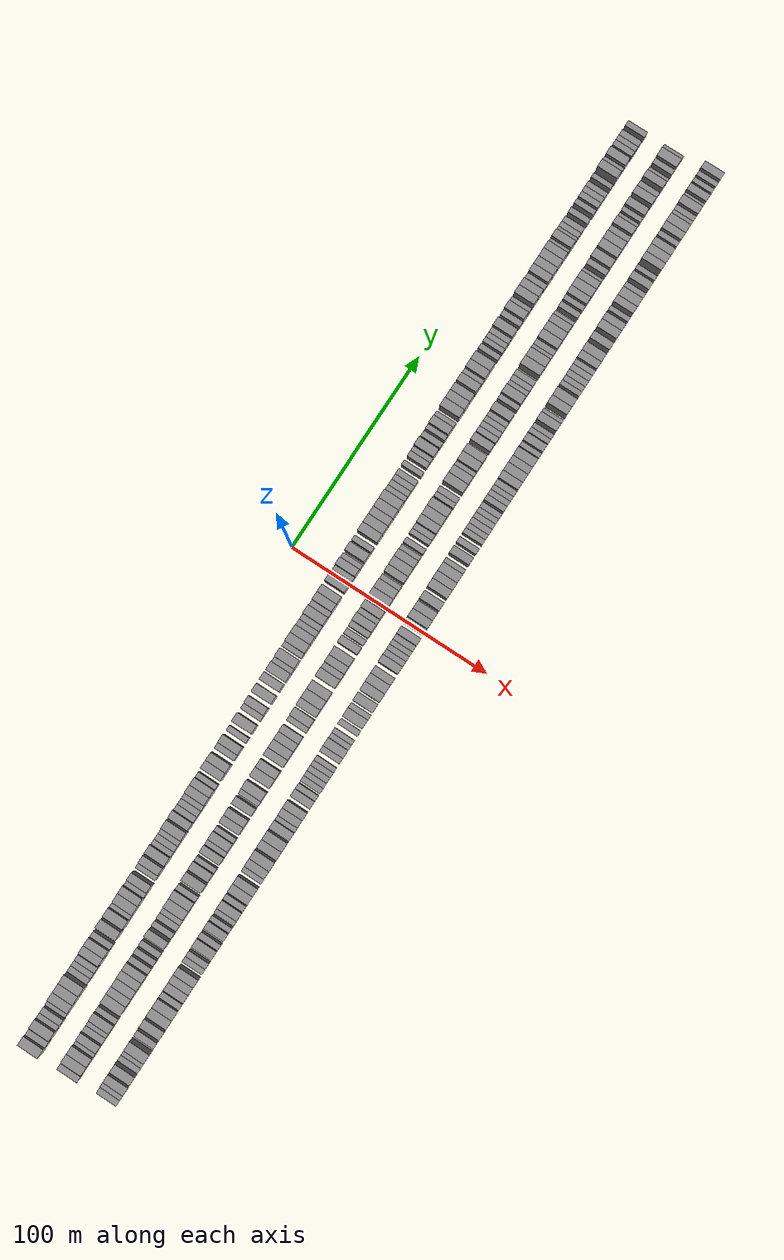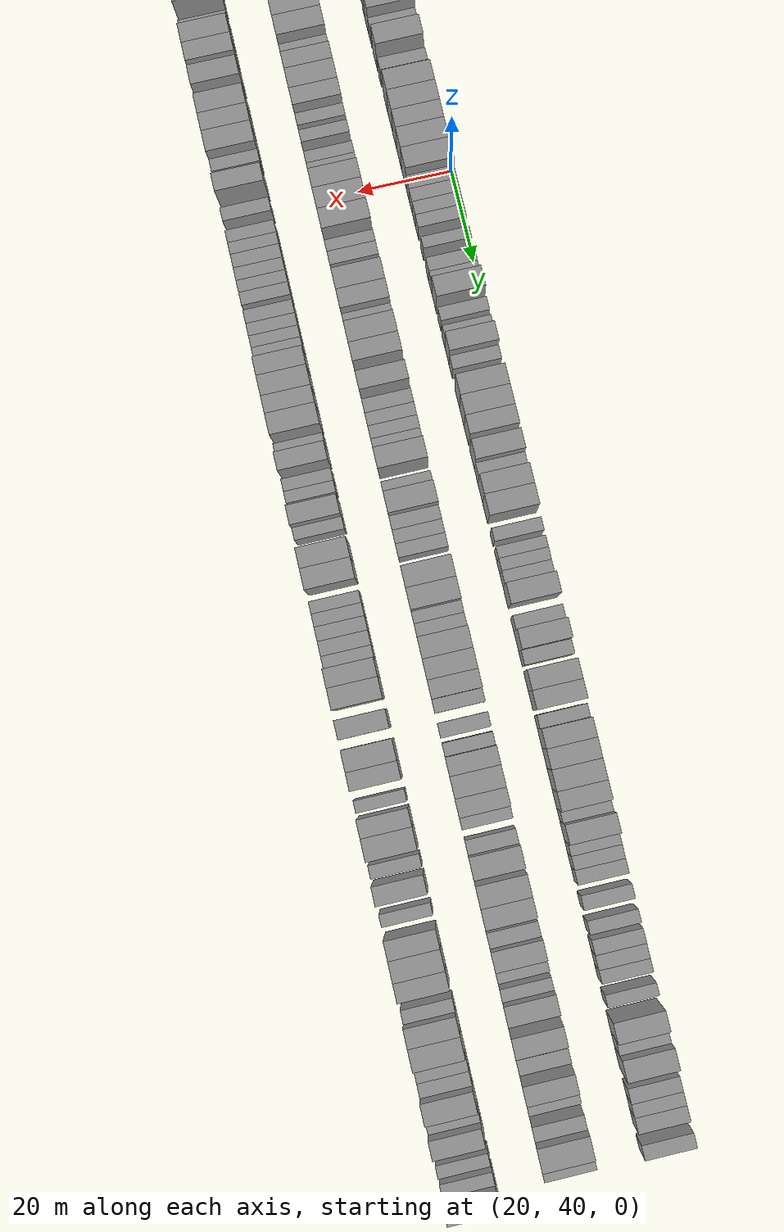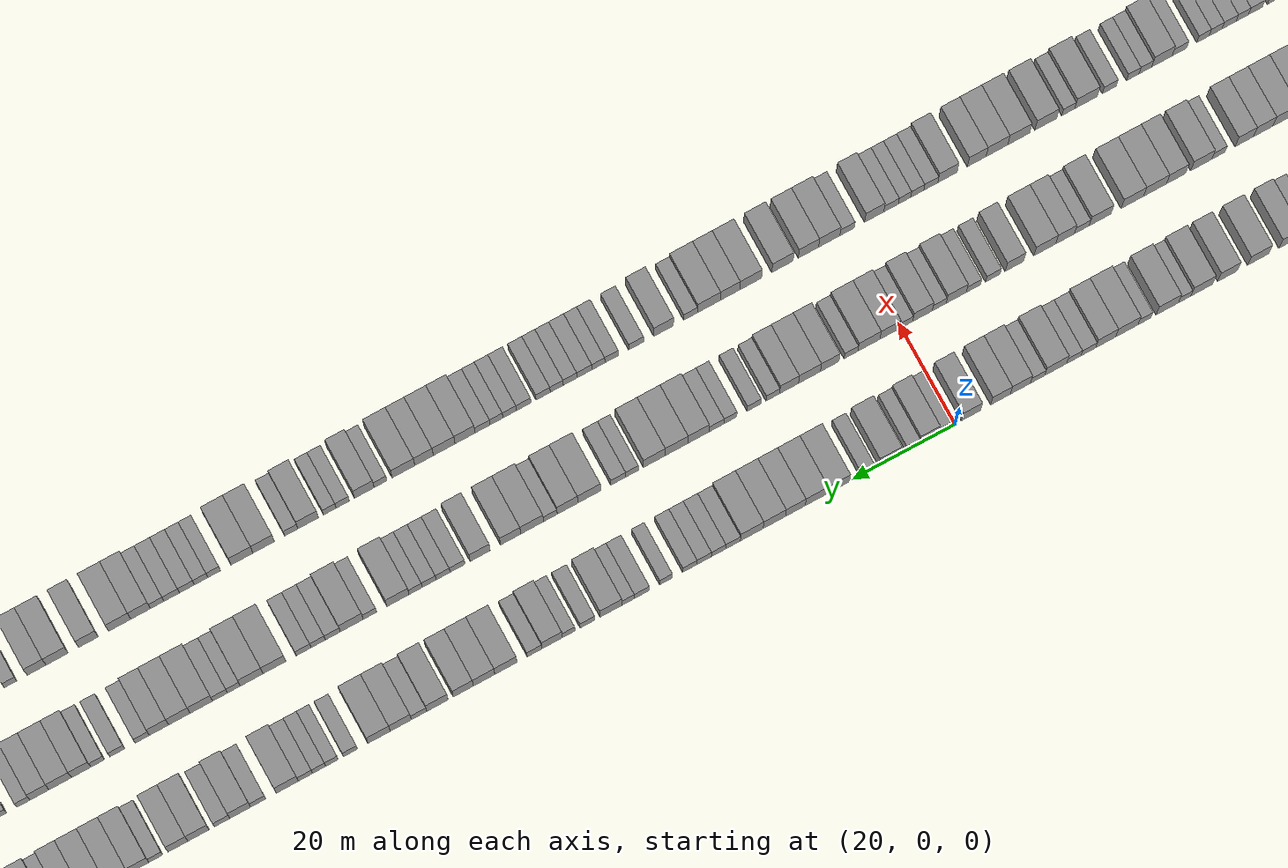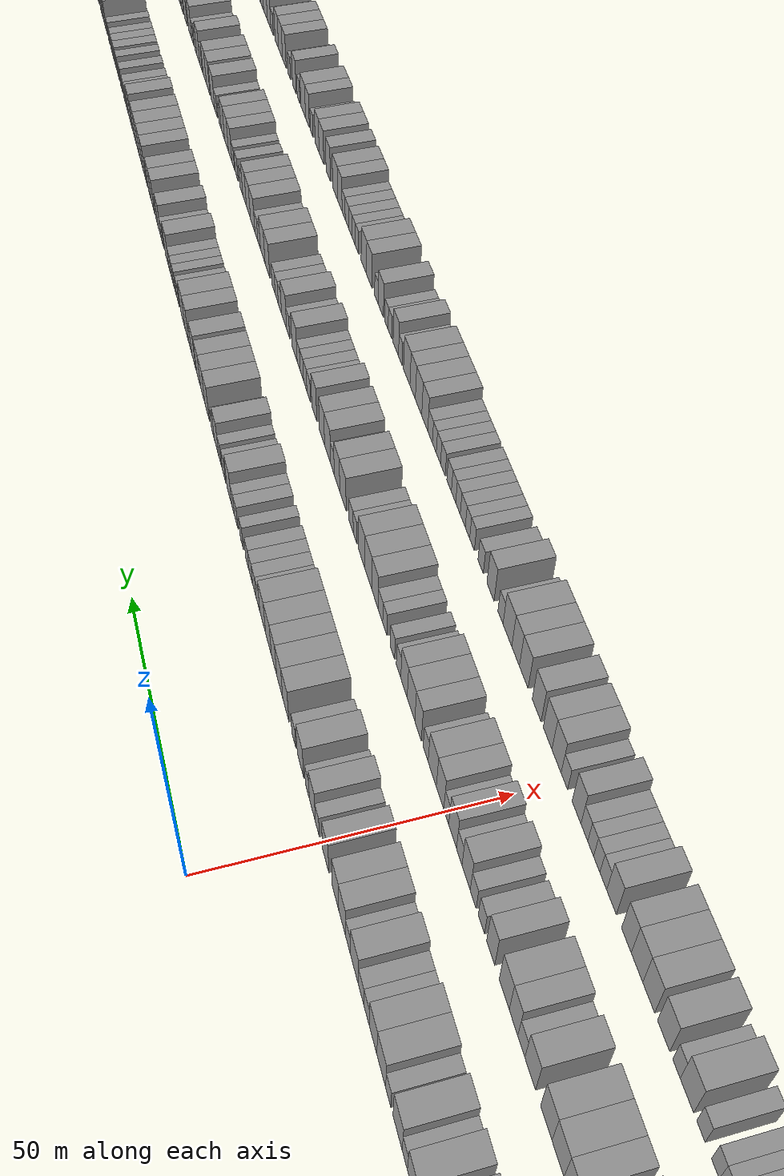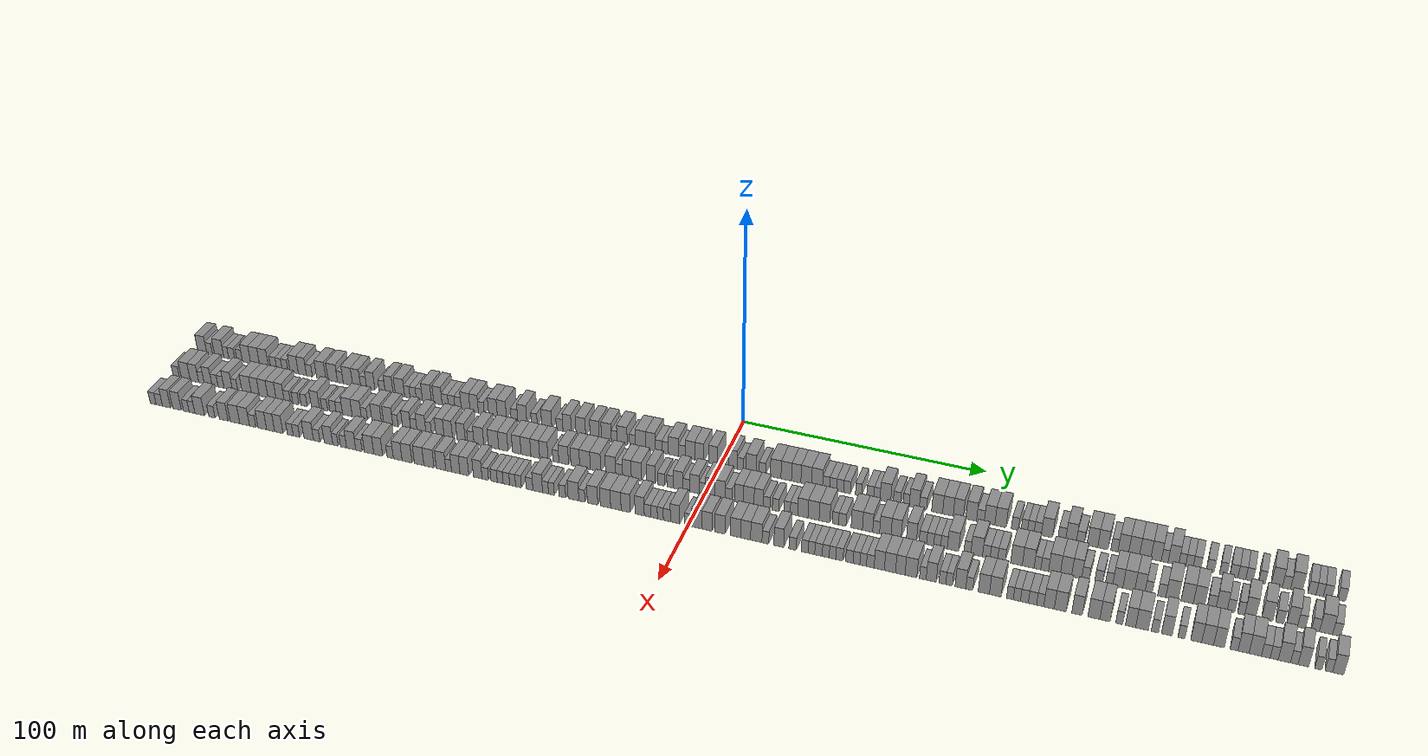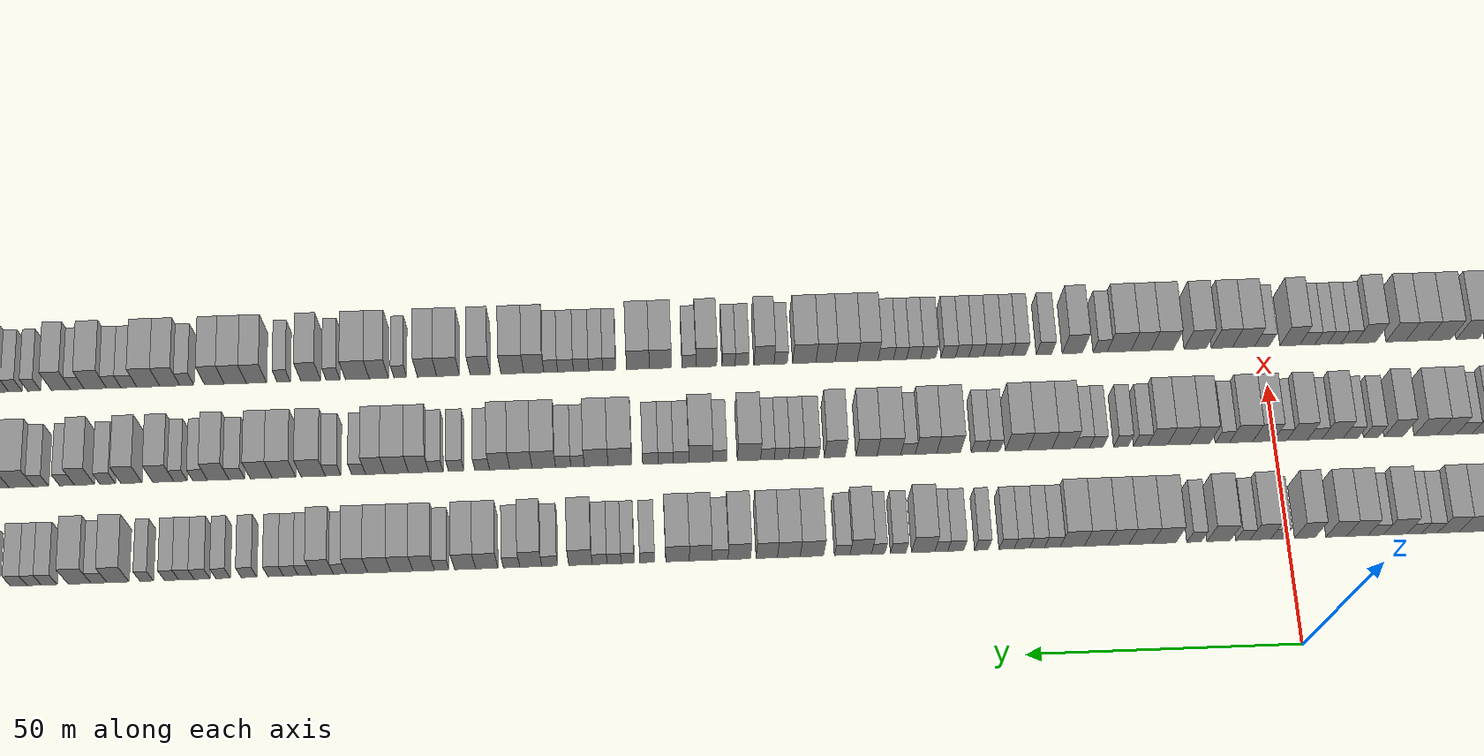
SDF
<sdf version="1.6">
 <world name="default">
  <scene>
   <sky><clouds><speed>12</speed></clouds></sky>
   <ambient>0.4 0.4 0.4 1</ambient>
   <background>0.7 0.7 0.7 1</background>
   <shadows>1</shadows>
  </scene>
  <gravity>0 0 -9.8066</gravity>
  <magnetic_field>6e-06 2.3e-05 -4.2e-05</magnetic_field>
  <physics default="0" name="default_physics" type="ode">
   <ode>
    <solver>
     <type>quick</type>
     <iters>10</iters>
     <sor>1.0</sor>
     <use_dynamic_moi_rescaling>0</use_dynamic_moi_rescaling>
    </solver>
    <constraints>
     <cfm>0</cfm>
     <erp>0.2</erp>
     <contact_max_correcting_vel>100</contact_max_correcting_vel>
     <contact_surface_layer>0.001</contact_surface_layer>
    </constraints>
   </ode>
   <max_step_size>0.004</max_step_size>
   <real_time_factor>1</real_time_factor>
   <real_time_update_rate>250</real_time_update_rate>
  </physics>
  <light name="sun" type="directional">
   <pose>0 0 10 0 0 0</pose>
   <diffuse>0.8 0.8 0.8 1</diffuse>
   <specular>0.2 0.2 0.2 1</specular>
   <attenuation>
    <range>1000</range>
    <constant>0.9</constant>
    <linear>0.01</linear>
    <quadratic>0.001</quadratic>
   </attenuation>
   <direction>-0.5 0.1 -0.9</direction>
  </light>
  <model name="building_1">
   <static>1</static>
   <pose>25.0000 -233.8101 0 0.000000 0.000000 0.000000</pose>
   <link name="link">
    <pose>0 0 4.50 0 0 0</pose>
    <collision name="collision"><geometry><box><size>10.0000 4.3798 9.0000</size></box></geometry></collision>
    <visual name="visual">
     <cast_shadows>0</cast_shadows>
     <geometry><box><size>10.0000 4.3798 9.0000</size></box></geometry>
     <material>
      <script>
       <uri>model://grey_wall/materials/scripts</uri>
       <uri>model://grey_wall/materials/textures</uri>
       <name>vrc/grey_wall</name>
      </script>
     </material>
    </visual>
   </link>
  </model>
  <model name="building_2">
   <static>1</static>
   <pose>25.0000 -230.1904 0 0.000000 0.000000 0.000000</pose>
   <link name="link">
    <pose>0 0 3.00 0 0 0</pose>
    <collision name="collision"><geometry><box><size>10.0000 2.8597 6.0000</size></box></geometry></collision>
    <visual name="visual">
     <cast_shadows>0</cast_shadows>
     <geometry><box><size>10.0000 2.8597 6.0000</size></box></geometry>
     <material>
      <script>
       <uri>model://grey_wall/materials/scripts</uri>
       <uri>model://grey_wall/materials/textures</uri>
       <name>vrc/grey_wall</name>
      </script>
     </material>
    </visual>
   </link>
  </model>
  <model name="building_3">
   <static>1</static>
   <pose>25.0000 -225.5455 0 0.000000 0.000000 0.000000</pose>
   <link name="link">
    <pose>0 0 4.50 0 0 0</pose>
    <collision name="collision"><geometry><box><size>10.0000 4.4301 9.0000</size></box></geometry></collision>
    <visual name="visual">
     <cast_shadows>0</cast_shadows>
     <geometry><box><size>10.0000 4.4301 9.0000</size></box></geometry>
     <material>
      <script>
       <uri>model://grey_wall/materials/scripts</uri>
       <uri>model://grey_wall/materials/textures</uri>
       <name>vrc/grey_wall</name>
      </script>
     </material>
    </visual>
   </link>
  </model>
  <model name="building_4">
   <static>1</static>
   <pose>25.0000 -222.1152 0 0.000000 0.000000 0.000000</pose>
   <link name="link">
    <pose>0 0 3.00 0 0 0</pose>
    <collision name="collision"><geometry><box><size>10.0000 2.4304 6.0000</size></box></geometry></collision>
    <visual name="visual">
     <cast_shadows>0</cast_shadows>
     <geometry><box><size>10.0000 2.4304 6.0000</size></box></geometry>
     <material>
      <script>
       <uri>model://grey_wall/materials/scripts</uri>
       <uri>model://grey_wall/materials/textures</uri>
       <name>vrc/grey_wall</name>
      </script>
     </material>
    </visual>
   </link>
  </model>
  <model name="building_5">
   <static>1</static>
   <pose>25.0000 -219.4373 0 0.000000 0.000000 0.000000</pose>
   <link name="link">
    <pose>0 0 3.00 0 0 0</pose>
    <collision name="collision"><geometry><box><size>10.0000 2.9253 6.0000</size></box></geometry></collision>
    <visual name="visual">
     <cast_shadows>0</cast_shadows>
     <geometry><box><size>10.0000 2.9253 6.0000</size></box></geometry>
     <material>
      <script>
       <uri>model://grey_wall/materials/scripts</uri>
       <uri>model://grey_wall/materials/textures</uri>
       <name>vrc/grey_wall</name>
      </script>
     </material>
    </visual>
   </link>
  </model>
  <model name="building_6">
   <static>1</static>
   <pose>25.0000 -215.6372 0 0.000000 0.000000 0.000000</pose>
   <link name="link">
    <pose>0 0 3.00 0 0 0</pose>
    <collision name="collision"><geometry><box><size>10.0000 2.6748 6.0000</size></box></geometry></collision>
    <visual name="visual">
     <cast_shadows>0</cast_shadows>
     <geometry><box><size>10.0000 2.6748 6.0000</size></box></geometry>
     <material>
      <script>
       <uri>model://grey_wall/materials/scripts</uri>
       <uri>model://grey_wall/materials/textures</uri>
       <name>vrc/grey_wall</name>
      </script>
     </material>
    </visual>
   </link>
  </model>
  <model name="building_7">
   <static>1</static>
   <pose>25.0000 -212.3114 0 0.000000 0.000000 0.000000</pose>
   <link name="link">
    <pose>0 0 4.50 0 0 0</pose>
    <collision name="collision"><geometry><box><size>10.0000 3.9768 9.0000</size></box></geometry></collision>
    <visual name="visual">
     <cast_shadows>0</cast_shadows>
     <geometry><box><size>10.0000 3.9768 9.0000</size></box></geometry>
     <material>
      <script>
       <uri>model://grey_wall/materials/scripts</uri>
       <uri>model://grey_wall/materials/textures</uri>
       <name>vrc/grey_wall</name>
      </script>
     </material>
    </visual>
   </link>
  </model>
  <model name="building_8">
   <static>1</static>
   <pose>25.0000 -208.1650 0 0.000000 0.000000 0.000000</pose>
   <link name="link">
    <pose>0 0 4.50 0 0 0</pose>
    <collision name="collision"><geometry><box><size>10.0000 4.3161 9.0000</size></box></geometry></collision>
    <visual name="visual">
     <cast_shadows>0</cast_shadows>
     <geometry><box><size>10.0000 4.3161 9.0000</size></box></geometry>
     <material>
      <script>
       <uri>model://grey_wall/materials/scripts</uri>
       <uri>model://grey_wall/materials/textures</uri>
       <name>vrc/grey_wall</name>
      </script>
     </material>
    </visual>
   </link>
  </model>
  <model name="building_9">
   <static>1</static>
   <pose>25.0000 -203.8633 0 0.000000 0.000000 0.000000</pose>
   <link name="link">
    <pose>0 0 4.50 0 0 0</pose>
    <collision name="collision"><geometry><box><size>10.0000 4.2874 9.0000</size></box></geometry></collision>
    <visual name="visual">
     <cast_shadows>0</cast_shadows>
     <geometry><box><size>10.0000 4.2874 9.0000</size></box></geometry>
     <material>
      <script>
       <uri>model://grey_wall/materials/scripts</uri>
       <uri>model://grey_wall/materials/textures</uri>
       <name>vrc/grey_wall</name>
      </script>
     </material>
    </visual>
   </link>
  </model>
  <model name="building_10">
   <static>1</static>
   <pose>25.0000 -199.2689 0 0.000000 0.000000 0.000000</pose>
   <link name="link">
    <pose>0 0 3.00 0 0 0</pose>
    <collision name="collision"><geometry><box><size>10.0000 2.9013 6.0000</size></box></geometry></collision>
    <visual name="visual">
     <cast_shadows>0</cast_shadows>
     <geometry><box><size>10.0000 2.9013 6.0000</size></box></geometry>
     <material>
      <script>
       <uri>model://grey_wall/materials/scripts</uri>
       <uri>model://grey_wall/materials/textures</uri>
       <name>vrc/grey_wall</name>
      </script>
     </material>
    </visual>
   </link>
  </model>
  <model name="building_11">
   <static>1</static>
   <pose>25.0000 -196.5179 0 0.000000 0.000000 0.000000</pose>
   <link name="link">
    <pose>0 0 3.00 0 0 0</pose>
    <collision name="collision"><geometry><box><size>10.0000 2.6006 6.0000</size></box></geometry></collision>
    <visual name="visual">
     <cast_shadows>0</cast_shadows>
     <geometry><box><size>10.0000 2.6006 6.0000</size></box></geometry>
     <material>
      <script>
       <uri>model://grey_wall/materials/scripts</uri>
       <uri>model://grey_wall/materials/textures</uri>
       <name>vrc/grey_wall</name>
      </script>
     </material>
    </visual>
   </link>
  </model>
  <model name="building_12">
   <static>1</static>
   <pose>25.0000 -193.8118 0 0.000000 0.000000 0.000000</pose>
   <link name="link">
    <pose>0 0 3.00 0 0 0</pose>
    <collision name="collision"><geometry><box><size>10.0000 2.8117 6.0000</size></box></geometry></collision>
    <visual name="visual">
     <cast_shadows>0</cast_shadows>
     <geometry><box><size>10.0000 2.8117 6.0000</size></box></geometry>
     <material>
      <script>
       <uri>model://grey_wall/materials/scripts</uri>
       <uri>model://grey_wall/materials/textures</uri>
       <name>vrc/grey_wall</name>
      </script>
     </material>
    </visual>
   </link>
  </model>
  <model name="building_13">
   <static>1</static>
   <pose>25.0000 -189.4417 0 0.000000 0.000000 0.000000</pose>
   <link name="link">
    <pose>0 0 4.50 0 0 0</pose>
    <collision name="collision"><geometry><box><size>10.0000 3.9283 9.0000</size></box></geometry></collision>
    <visual name="visual">
     <cast_shadows>0</cast_shadows>
     <geometry><box><size>10.0000 3.9283 9.0000</size></box></geometry>
     <material>
      <script>
       <uri>model://grey_wall/materials/scripts</uri>
       <uri>model://grey_wall/materials/textures</uri>
       <name>vrc/grey_wall</name>
      </script>
     </material>
    </visual>
   </link>
  </model>
  <model name="building_14">
   <static>1</static>
   <pose>25.0000 -185.5741 0 0.000000 0.000000 0.000000</pose>
   <link name="link">
    <pose>0 0 4.50 0 0 0</pose>
    <collision name="collision"><geometry><box><size>10.0000 3.8069 9.0000</size></box></geometry></collision>
    <visual name="visual">
     <cast_shadows>0</cast_shadows>
     <geometry><box><size>10.0000 3.8069 9.0000</size></box></geometry>
     <material>
      <script>
       <uri>model://grey_wall/materials/scripts</uri>
       <uri>model://grey_wall/materials/textures</uri>
       <name>vrc/grey_wall</name>
      </script>
     </material>
    </visual>
   </link>
  </model>
  <model name="building_15">
   <static>1</static>
   <pose>25.0000 -182.2556 0 0.000000 0.000000 0.000000</pose>
   <link name="link">
    <pose>0 0 3.00 0 0 0</pose>
    <collision name="collision"><geometry><box><size>10.0000 2.8301 6.0000</size></box></geometry></collision>
    <visual name="visual">
     <cast_shadows>0</cast_shadows>
     <geometry><box><size>10.0000 2.8301 6.0000</size></box></geometry>
     <material>
      <script>
       <uri>model://grey_wall/materials/scripts</uri>
       <uri>model://grey_wall/materials/textures</uri>
       <name>vrc/grey_wall</name>
      </script>
     </material>
    </visual>
   </link>
  </model>
  <model name="building_16">
   <static>1</static>
   <pose>25.0000 -176.6451 0 0.000000 0.000000 0.000000</pose>
   <link name="link">
    <pose>0 0 4.50 0 0 0</pose>
    <collision name="collision"><geometry><box><size>10.0000 4.3909 9.0000</size></box></geometry></collision>
    <visual name="visual">
     <cast_shadows>0</cast_shadows>
     <geometry><box><size>10.0000 4.3909 9.0000</size></box></geometry>
     <material>
      <script>
       <uri>model://grey_wall/materials/scripts</uri>
       <uri>model://grey_wall/materials/textures</uri>
       <name>vrc/grey_wall</name>
      </script>
     </material>
    </visual>
   </link>
  </model>
  <model name="building_17">
   <static>1</static>
   <pose>25.0000 -171.2422 0 0.000000 0.000000 0.000000</pose>
   <link name="link">
    <pose>0 0 4.50 0 0 0</pose>
    <collision name="collision"><geometry><box><size>10.0000 4.4151 9.0000</size></box></geometry></collision>
    <visual name="visual">
     <cast_shadows>0</cast_shadows>
     <geometry><box><size>10.0000 4.4151 9.0000</size></box></geometry>
     <material>
      <script>
       <uri>model://grey_wall/materials/scripts</uri>
       <uri>model://grey_wall/materials/textures</uri>
       <name>vrc/grey_wall</name>
      </script>
     </material>
    </visual>
   </link>
  </model>
  <model name="building_18">
   <static>1</static>
   <pose>25.0000 -167.6906 0 0.000000 0.000000 0.000000</pose>
   <link name="link">
    <pose>0 0 3.00 0 0 0</pose>
    <collision name="collision"><geometry><box><size>10.0000 2.6881 6.0000</size></box></geometry></collision>
    <visual name="visual">
     <cast_shadows>0</cast_shadows>
     <geometry><box><size>10.0000 2.6881 6.0000</size></box></geometry>
     <material>
      <script>
       <uri>model://grey_wall/materials/scripts</uri>
       <uri>model://grey_wall/materials/textures</uri>
       <name>vrc/grey_wall</name>
      </script>
     </material>
    </visual>
   </link>
  </model>
  <model name="building_19">
   <static>1</static>
   <pose>25.0000 -164.1504 0 0.000000 0.000000 0.000000</pose>
   <link name="link">
    <pose>0 0 4.50 0 0 0</pose>
    <collision name="collision"><geometry><box><size>10.0000 4.3922 9.0000</size></box></geometry></collision>
    <visual name="visual">
     <cast_shadows>0</cast_shadows>
     <geometry><box><size>10.0000 4.3922 9.0000</size></box></geometry>
     <material>
      <script>
       <uri>model://grey_wall/materials/scripts</uri>
       <uri>model://grey_wall/materials/textures</uri>
       <name>vrc/grey_wall</name>
      </script>
     </material>
    </visual>
   </link>
  </model>
  <model name="building_20">
   <static>1</static>
   <pose>25.0000 -160.0922 0 0.000000 0.000000 0.000000</pose>
   <link name="link">
    <pose>0 0 4.50 0 0 0</pose>
    <collision name="collision"><geometry><box><size>10.0000 3.7243 9.0000</size></box></geometry></collision>
    <visual name="visual">
     <cast_shadows>0</cast_shadows>
     <geometry><box><size>10.0000 3.7243 9.0000</size></box></geometry>
     <material>
      <script>
       <uri>model://grey_wall/materials/scripts</uri>
       <uri>model://grey_wall/materials/textures</uri>
       <name>vrc/grey_wall</name>
      </script>
     </material>
    </visual>
   </link>
  </model>
  <model name="building_21">
   <static>1</static>
   <pose>25.0000 -156.8335 0 0.000000 0.000000 0.000000</pose>
   <link name="link">
    <pose>0 0 3.00 0 0 0</pose>
    <collision name="collision"><geometry><box><size>10.0000 2.7931 6.0000</size></box></geometry></collision>
    <visual name="visual">
     <cast_shadows>0</cast_shadows>
     <geometry><box><size>10.0000 2.7931 6.0000</size></box></geometry>
     <material>
      <script>
       <uri>model://grey_wall/materials/scripts</uri>
       <uri>model://grey_wall/materials/textures</uri>
       <name>vrc/grey_wall</name>
      </script>
     </material>
    </visual>
   </link>
  </model>
  <model name="building_22">
   <static>1</static>
   <pose>25.0000 -153.5188 0 0.000000 0.000000 0.000000</pose>
   <link name="link">
    <pose>0 0 4.50 0 0 0</pose>
    <collision name="collision"><geometry><box><size>10.0000 3.8362 9.0000</size></box></geometry></collision>
    <visual name="visual">
     <cast_shadows>0</cast_shadows>
     <geometry><box><size>10.0000 3.8362 9.0000</size></box></geometry>
     <material>
      <script>
       <uri>model://grey_wall/materials/scripts</uri>
       <uri>model://grey_wall/materials/textures</uri>
       <name>vrc/grey_wall</name>
      </script>
     </material>
    </visual>
   </link>
  </model>
  <model name="building_23">
   <static>1</static>
   <pose>25.0000 -148.1975 0 0.000000 0.000000 0.000000</pose>
   <link name="link">
    <pose>0 0 3.00 0 0 0</pose>
    <collision name="collision"><geometry><box><size>10.0000 2.8065 6.0000</size></box></geometry></collision>
    <visual name="visual">
     <cast_shadows>0</cast_shadows>
     <geometry><box><size>10.0000 2.8065 6.0000</size></box></geometry>
     <material>
      <script>
       <uri>model://grey_wall/materials/scripts</uri>
       <uri>model://grey_wall/materials/textures</uri>
       <name>vrc/grey_wall</name>
      </script>
     </material>
    </visual>
   </link>
  </model>
  <model name="building_24">
   <static>1</static>
   <pose>25.0000 -144.9755 0 0.000000 0.000000 0.000000</pose>
   <link name="link">
    <pose>0 0 4.50 0 0 0</pose>
    <collision name="collision"><geometry><box><size>10.0000 3.6374 9.0000</size></box></geometry></collision>
    <visual name="visual">
     <cast_shadows>0</cast_shadows>
     <geometry><box><size>10.0000 3.6374 9.0000</size></box></geometry>
     <material>
      <script>
       <uri>model://grey_wall/materials/scripts</uri>
       <uri>model://grey_wall/materials/textures</uri>
       <name>vrc/grey_wall</name>
      </script>
     </material>
    </visual>
   </link>
  </model>
  <model name="building_25">
   <static>1</static>
   <pose>25.0000 -140.0256 0 0.000000 0.000000 0.000000</pose>
   <link name="link">
    <pose>0 0 4.50 0 0 0</pose>
    <collision name="collision"><geometry><box><size>10.0000 4.2623 9.0000</size></box></geometry></collision>
    <visual name="visual">
     <cast_shadows>0</cast_shadows>
     <geometry><box><size>10.0000 4.2623 9.0000</size></box></geometry>
     <material>
      <script>
       <uri>model://grey_wall/materials/scripts</uri>
       <uri>model://grey_wall/materials/textures</uri>
       <name>vrc/grey_wall</name>
      </script>
     </material>
    </visual>
   </link>
  </model>
  <model name="building_26">
   <static>1</static>
   <pose>25.0000 -136.6577 0 0.000000 0.000000 0.000000</pose>
   <link name="link">
    <pose>0 0 3.00 0 0 0</pose>
    <collision name="collision"><geometry><box><size>10.0000 2.4735 6.0000</size></box></geometry></collision>
    <visual name="visual">
     <cast_shadows>0</cast_shadows>
     <geometry><box><size>10.0000 2.4735 6.0000</size></box></geometry>
     <material>
      <script>
       <uri>model://grey_wall/materials/scripts</uri>
       <uri>model://grey_wall/materials/textures</uri>
       <name>vrc/grey_wall</name>
      </script>
     </material>
    </visual>
   </link>
  </model>
  <model name="building_27">
   <static>1</static>
   <pose>25.0000 -133.9958 0 0.000000 0.000000 0.000000</pose>
   <link name="link">
    <pose>0 0 3.00 0 0 0</pose>
    <collision name="collision"><geometry><box><size>10.0000 2.8502 6.0000</size></box></geometry></collision>
    <visual name="visual">
     <cast_shadows>0</cast_shadows>
     <geometry><box><size>10.0000 2.8502 6.0000</size></box></geometry>
     <material>
      <script>
       <uri>model://grey_wall/materials/scripts</uri>
       <uri>model://grey_wall/materials/textures</uri>
       <name>vrc/grey_wall</name>
      </script>
     </material>
    </visual>
   </link>
  </model>
  <model name="building_28">
   <static>1</static>
   <pose>25.0000 -131.1555 0 0.000000 0.000000 0.000000</pose>
   <link name="link">
    <pose>0 0 3.00 0 0 0</pose>
    <collision name="collision"><geometry><box><size>10.0000 2.8305 6.0000</size></box></geometry></collision>
    <visual name="visual">
     <cast_shadows>0</cast_shadows>
     <geometry><box><size>10.0000 2.8305 6.0000</size></box></geometry>
     <material>
      <script>
       <uri>model://grey_wall/materials/scripts</uri>
       <uri>model://grey_wall/materials/textures</uri>
       <name>vrc/grey_wall</name>
      </script>
     </material>
    </visual>
   </link>
  </model>
  <model name="building_29">
   <static>1</static>
   <pose>25.0000 -127.6747 0 0.000000 0.000000 0.000000</pose>
   <link name="link">
    <pose>0 0 4.50 0 0 0</pose>
    <collision name="collision"><geometry><box><size>10.0000 4.1310 9.0000</size></box></geometry></collision>
    <visual name="visual">
     <cast_shadows>0</cast_shadows>
     <geometry><box><size>10.0000 4.1310 9.0000</size></box></geometry>
     <material>
      <script>
       <uri>model://grey_wall/materials/scripts</uri>
       <uri>model://grey_wall/materials/textures</uri>
       <name>vrc/grey_wall</name>
      </script>
     </material>
    </visual>
   </link>
  </model>
  <model name="building_30">
   <static>1</static>
   <pose>25.0000 -122.6951 0 0.000000 0.000000 0.000000</pose>
   <link name="link">
    <pose>0 0 4.50 0 0 0</pose>
    <collision name="collision"><geometry><box><size>10.0000 3.8283 9.0000</size></box></geometry></collision>
    <visual name="visual">
     <cast_shadows>0</cast_shadows>
     <geometry><box><size>10.0000 3.8283 9.0000</size></box></geometry>
     <material>
      <script>
       <uri>model://grey_wall/materials/scripts</uri>
       <uri>model://grey_wall/materials/textures</uri>
       <name>vrc/grey_wall</name>
      </script>
     </material>
    </visual>
   </link>
  </model>
  <model name="building_31">
   <static>1</static>
   <pose>25.0000 -119.3521 0 0.000000 0.000000 0.000000</pose>
   <link name="link">
    <pose>0 0 3.00 0 0 0</pose>
    <collision name="collision"><geometry><box><size>10.0000 2.8576 6.0000</size></box></geometry></collision>
    <visual name="visual">
     <cast_shadows>0</cast_shadows>
     <geometry><box><size>10.0000 2.8576 6.0000</size></box></geometry>
     <material>
      <script>
       <uri>model://grey_wall/materials/scripts</uri>
       <uri>model://grey_wall/materials/textures</uri>
       <name>vrc/grey_wall</name>
      </script>
     </material>
    </visual>
   </link>
  </model>
  <model name="building_32">
   <static>1</static>
   <pose>25.0000 -116.4563 0 0.000000 0.000000 0.000000</pose>
   <link name="link">
    <pose>0 0 3.00 0 0 0</pose>
    <collision name="collision"><geometry><box><size>10.0000 2.9341 6.0000</size></box></geometry></collision>
    <visual name="visual">
     <cast_shadows>0</cast_shadows>
     <geometry><box><size>10.0000 2.9341 6.0000</size></box></geometry>
     <material>
      <script>
       <uri>model://grey_wall/materials/scripts</uri>
       <uri>model://grey_wall/materials/textures</uri>
       <name>vrc/grey_wall</name>
      </script>
     </material>
    </visual>
   </link>
  </model>
  <model name="building_33">
   <static>1</static>
   <pose>25.0000 -113.5589 0 0.000000 0.000000 0.000000</pose>
   <link name="link">
    <pose>0 0 3.00 0 0 0</pose>
    <collision name="collision"><geometry><box><size>10.0000 2.8606 6.0000</size></box></geometry></collision>
    <visual name="visual">
     <cast_shadows>0</cast_shadows>
     <geometry><box><size>10.0000 2.8606 6.0000</size></box></geometry>
     <material>
      <script>
       <uri>model://grey_wall/materials/scripts</uri>
       <uri>model://grey_wall/materials/textures</uri>
       <name>vrc/grey_wall</name>
      </script>
     </material>
    </visual>
   </link>
  </model>
  <model name="building_34">
   <static>1</static>
   <pose>25.0000 -110.1387 0 0.000000 0.000000 0.000000</pose>
   <link name="link">
    <pose>0 0 4.50 0 0 0</pose>
    <collision name="collision"><geometry><box><size>10.0000 3.9799 9.0000</size></box></geometry></collision>
    <visual name="visual">
     <cast_shadows>0</cast_shadows>
     <geometry><box><size>10.0000 3.9799 9.0000</size></box></geometry>
     <material>
      <script>
       <uri>model://grey_wall/materials/scripts</uri>
       <uri>model://grey_wall/materials/textures</uri>
       <name>vrc/grey_wall</name>
      </script>
     </material>
    </visual>
   </link>
  </model>
  <model name="building_35">
   <static>1</static>
   <pose>25.0000 -106.2834 0 0.000000 0.000000 0.000000</pose>
   <link name="link">
    <pose>0 0 4.50 0 0 0</pose>
    <collision name="collision"><geometry><box><size>10.0000 3.7308 9.0000</size></box></geometry></collision>
    <visual name="visual">
     <cast_shadows>0</cast_shadows>
     <geometry><box><size>10.0000 3.7308 9.0000</size></box></geometry>
     <material>
      <script>
       <uri>model://grey_wall/materials/scripts</uri>
       <uri>model://grey_wall/materials/textures</uri>
       <name>vrc/grey_wall</name>
      </script>
     </material>
    </visual>
   </link>
  </model>
  <model name="building_36">
   <static>1</static>
   <pose>25.0000 -103.1273 0 0.000000 0.000000 0.000000</pose>
   <link name="link">
    <pose>0 0 3.00 0 0 0</pose>
    <collision name="collision"><geometry><box><size>10.0000 2.5815 6.0000</size></box></geometry></collision>
    <visual name="visual">
     <cast_shadows>0</cast_shadows>
     <geometry><box><size>10.0000 2.5815 6.0000</size></box></geometry>
     <material>
      <script>
       <uri>model://grey_wall/materials/scripts</uri>
       <uri>model://grey_wall/materials/textures</uri>
       <name>vrc/grey_wall</name>
      </script>
     </material>
    </visual>
   </link>
  </model>
  <model name="building_37">
   <static>1</static>
   <pose>25.0000 -97.8834 0 0.000000 0.000000 0.000000</pose>
   <link name="link">
    <pose>0 0 4.50 0 0 0</pose>
    <collision name="collision"><geometry><box><size>10.0000 3.9064 9.0000</size></box></geometry></collision>
    <visual name="visual">
     <cast_shadows>0</cast_shadows>
     <geometry><box><size>10.0000 3.9064 9.0000</size></box></geometry>
     <material>
      <script>
       <uri>model://grey_wall/materials/scripts</uri>
       <uri>model://grey_wall/materials/textures</uri>
       <name>vrc/grey_wall</name>
      </script>
     </material>
    </visual>
   </link>
  </model>
  <model name="building_38">
   <static>1</static>
   <pose>25.0000 -93.9067 0 0.000000 0.000000 0.000000</pose>
   <link name="link">
    <pose>0 0 4.50 0 0 0</pose>
    <collision name="collision"><geometry><box><size>10.0000 4.0469 9.0000</size></box></geometry></collision>
    <visual name="visual">
     <cast_shadows>0</cast_shadows>
     <geometry><box><size>10.0000 4.0469 9.0000</size></box></geometry>
     <material>
      <script>
       <uri>model://grey_wall/materials/scripts</uri>
       <uri>model://grey_wall/materials/textures</uri>
       <name>vrc/grey_wall</name>
      </script>
     </material>
    </visual>
   </link>
  </model>
  <model name="building_39">
   <static>1</static>
   <pose>25.0000 -88.3887 0 0.000000 0.000000 0.000000</pose>
   <link name="link">
    <pose>0 0 3.00 0 0 0</pose>
    <collision name="collision"><geometry><box><size>10.0000 2.9891 6.0000</size></box></geometry></collision>
    <visual name="visual">
     <cast_shadows>0</cast_shadows>
     <geometry><box><size>10.0000 2.9891 6.0000</size></box></geometry>
     <material>
      <script>
       <uri>model://grey_wall/materials/scripts</uri>
       <uri>model://grey_wall/materials/textures</uri>
       <name>vrc/grey_wall</name>
      </script>
     </material>
    </visual>
   </link>
  </model>
  <model name="building_40">
   <static>1</static>
   <pose>25.0000 -84.8901 0 0.000000 0.000000 0.000000</pose>
   <link name="link">
    <pose>0 0 4.50 0 0 0</pose>
    <collision name="collision"><geometry><box><size>10.0000 4.0083 9.0000</size></box></geometry></collision>
    <visual name="visual">
     <cast_shadows>0</cast_shadows>
     <geometry><box><size>10.0000 4.0083 9.0000</size></box></geometry>
     <material>
      <script>
       <uri>model://grey_wall/materials/scripts</uri>
       <uri>model://grey_wall/materials/textures</uri>
       <name>vrc/grey_wall</name>
      </script>
     </material>
    </visual>
   </link>
  </model>
  <model name="building_41">
   <static>1</static>
   <pose>25.0000 -79.5864 0 0.000000 0.000000 0.000000</pose>
   <link name="link">
    <pose>0 0 3.00 0 0 0</pose>
    <collision name="collision"><geometry><box><size>10.0000 2.5991 6.0000</size></box></geometry></collision>
    <visual name="visual">
     <cast_shadows>0</cast_shadows>
     <geometry><box><size>10.0000 2.5991 6.0000</size></box></geometry>
     <material>
      <script>
       <uri>model://grey_wall/materials/scripts</uri>
       <uri>model://grey_wall/materials/textures</uri>
       <name>vrc/grey_wall</name>
      </script>
     </material>
    </visual>
   </link>
  </model>
  <model name="building_42">
   <static>1</static>
   <pose>25.0000 -74.0940 0 0.000000 0.000000 0.000000</pose>
   <link name="link">
    <pose>0 0 4.50 0 0 0</pose>
    <collision name="collision"><geometry><box><size>10.0000 4.3855 9.0000</size></box></geometry></collision>
    <visual name="visual">
     <cast_shadows>0</cast_shadows>
     <geometry><box><size>10.0000 4.3855 9.0000</size></box></geometry>
     <material>
      <script>
       <uri>model://grey_wall/materials/scripts</uri>
       <uri>model://grey_wall/materials/textures</uri>
       <name>vrc/grey_wall</name>
      </script>
     </material>
    </visual>
   </link>
  </model>
  <model name="building_43">
   <static>1</static>
   <pose>25.0000 -68.4667 0 0.000000 0.000000 0.000000</pose>
   <link name="link">
    <pose>0 0 3.00 0 0 0</pose>
    <collision name="collision"><geometry><box><size>10.0000 2.8691 6.0000</size></box></geometry></collision>
    <visual name="visual">
     <cast_shadows>0</cast_shadows>
     <geometry><box><size>10.0000 2.8691 6.0000</size></box></geometry>
     <material>
      <script>
       <uri>model://grey_wall/materials/scripts</uri>
       <uri>model://grey_wall/materials/textures</uri>
       <name>vrc/grey_wall</name>
      </script>
     </material>
    </visual>
   </link>
  </model>
  <model name="building_44">
   <static>1</static>
   <pose>25.0000 -65.1917 0 0.000000 0.000000 0.000000</pose>
   <link name="link">
    <pose>0 0 4.50 0 0 0</pose>
    <collision name="collision"><geometry><box><size>10.0000 3.6809 9.0000</size></box></geometry></collision>
    <visual name="visual">
     <cast_shadows>0</cast_shadows>
     <geometry><box><size>10.0000 3.6809 9.0000</size></box></geometry>
     <material>
      <script>
       <uri>model://grey_wall/materials/scripts</uri>
       <uri>model://grey_wall/materials/textures</uri>
       <name>vrc/grey_wall</name>
      </script>
     </material>
    </visual>
   </link>
  </model>
  <model name="building_45">
   <static>1</static>
   <pose>25.0000 -59.2652 0 0.000000 0.000000 0.000000</pose>
   <link name="link">
    <pose>0 0 4.50 0 0 0</pose>
    <collision name="collision"><geometry><box><size>10.0000 4.1720 9.0000</size></box></geometry></collision>
    <visual name="visual">
     <cast_shadows>0</cast_shadows>
     <geometry><box><size>10.0000 4.1720 9.0000</size></box></geometry>
     <material>
      <script>
       <uri>model://grey_wall/materials/scripts</uri>
       <uri>model://grey_wall/materials/textures</uri>
       <name>vrc/grey_wall</name>
      </script>
     </material>
    </visual>
   </link>
  </model>
  <model name="building_46">
   <static>1</static>
   <pose>25.0000 -53.2486 0 0.000000 0.000000 0.000000</pose>
   <link name="link">
    <pose>0 0 4.50 0 0 0</pose>
    <collision name="collision"><geometry><box><size>10.0000 3.8611 9.0000</size></box></geometry></collision>
    <visual name="visual">
     <cast_shadows>0</cast_shadows>
     <geometry><box><size>10.0000 3.8611 9.0000</size></box></geometry>
     <material>
      <script>
       <uri>model://grey_wall/materials/scripts</uri>
       <uri>model://grey_wall/materials/textures</uri>
       <name>vrc/grey_wall</name>
      </script>
     </material>
    </visual>
   </link>
  </model>
  <model name="building_47">
   <static>1</static>
   <pose>25.0000 -48.1842 0 0.000000 0.000000 0.000000</pose>
   <link name="link">
    <pose>0 0 4.50 0 0 0</pose>
    <collision name="collision"><geometry><box><size>10.0000 4.2677 9.0000</size></box></geometry></collision>
    <visual name="visual">
     <cast_shadows>0</cast_shadows>
     <geometry><box><size>10.0000 4.2677 9.0000</size></box></geometry>
     <material>
      <script>
       <uri>model://grey_wall/materials/scripts</uri>
       <uri>model://grey_wall/materials/textures</uri>
       <name>vrc/grey_wall</name>
      </script>
     </material>
    </visual>
   </link>
  </model>
  <model name="building_48">
   <static>1</static>
   <pose>25.0000 -44.8295 0 0.000000 0.000000 0.000000</pose>
   <link name="link">
    <pose>0 0 3.00 0 0 0</pose>
    <collision name="collision"><geometry><box><size>10.0000 2.4418 6.0000</size></box></geometry></collision>
    <visual name="visual">
     <cast_shadows>0</cast_shadows>
     <geometry><box><size>10.0000 2.4418 6.0000</size></box></geometry>
     <material>
      <script>
       <uri>model://grey_wall/materials/scripts</uri>
       <uri>model://grey_wall/materials/textures</uri>
       <name>vrc/grey_wall</name>
      </script>
     </material>
    </visual>
   </link>
  </model>
  <model name="building_49">
   <static>1</static>
   <pose>25.0000 -41.4248 0 0.000000 0.000000 0.000000</pose>
   <link name="link">
    <pose>0 0 4.50 0 0 0</pose>
    <collision name="collision"><geometry><box><size>10.0000 4.3678 9.0000</size></box></geometry></collision>
    <visual name="visual">
     <cast_shadows>0</cast_shadows>
     <geometry><box><size>10.0000 4.3678 9.0000</size></box></geometry>
     <material>
      <script>
       <uri>model://grey_wall/materials/scripts</uri>
       <uri>model://grey_wall/materials/textures</uri>
       <name>vrc/grey_wall</name>
      </script>
     </material>
    </visual>
   </link>
  </model>
  <model name="building_50">
   <static>1</static>
   <pose>25.0000 -36.9635 0 0.000000 0.000000 0.000000</pose>
   <link name="link">
    <pose>0 0 3.00 0 0 0</pose>
    <collision name="collision"><geometry><box><size>10.0000 2.5547 6.0000</size></box></geometry></collision>
    <visual name="visual">
     <cast_shadows>0</cast_shadows>
     <geometry><box><size>10.0000 2.5547 6.0000</size></box></geometry>
     <material>
      <script>
       <uri>model://grey_wall/materials/scripts</uri>
       <uri>model://grey_wall/materials/textures</uri>
       <name>vrc/grey_wall</name>
      </script>
     </material>
    </visual>
   </link>
  </model>
  <model name="building_51">
   <static>1</static>
   <pose>25.0000 -33.5015 0 0.000000 0.000000 0.000000</pose>
   <link name="link">
    <pose>0 0 4.50 0 0 0</pose>
    <collision name="collision"><geometry><box><size>10.0000 4.3692 9.0000</size></box></geometry></collision>
    <visual name="visual">
     <cast_shadows>0</cast_shadows>
     <geometry><box><size>10.0000 4.3692 9.0000</size></box></geometry>
     <material>
      <script>
       <uri>model://grey_wall/materials/scripts</uri>
       <uri>model://grey_wall/materials/textures</uri>
       <name>vrc/grey_wall</name>
      </script>
     </material>
    </visual>
   </link>
  </model>
  <model name="building_52">
   <static>1</static>
   <pose>25.0000 -29.3595 0 0.000000 0.000000 0.000000</pose>
   <link name="link">
    <pose>0 0 4.50 0 0 0</pose>
    <collision name="collision"><geometry><box><size>10.0000 3.9149 9.0000</size></box></geometry></collision>
    <visual name="visual">
     <cast_shadows>0</cast_shadows>
     <geometry><box><size>10.0000 3.9149 9.0000</size></box></geometry>
     <material>
      <script>
       <uri>model://grey_wall/materials/scripts</uri>
       <uri>model://grey_wall/materials/textures</uri>
       <name>vrc/grey_wall</name>
      </script>
     </material>
    </visual>
   </link>
  </model>
  <model name="building_53">
   <static>1</static>
   <pose>25.0000 -25.9612 0 0.000000 0.000000 0.000000</pose>
   <link name="link">
    <pose>0 0 3.00 0 0 0</pose>
    <collision name="collision"><geometry><box><size>10.0000 2.8816 6.0000</size></box></geometry></collision>
    <visual name="visual">
     <cast_shadows>0</cast_shadows>
     <geometry><box><size>10.0000 2.8816 6.0000</size></box></geometry>
     <material>
      <script>
       <uri>model://grey_wall/materials/scripts</uri>
       <uri>model://grey_wall/materials/textures</uri>
       <name>vrc/grey_wall</name>
      </script>
     </material>
    </visual>
   </link>
  </model>
  <model name="building_54">
   <static>1</static>
   <pose>25.0000 -23.1204 0 0.000000 0.000000 0.000000</pose>
   <link name="link">
    <pose>0 0 3.00 0 0 0</pose>
    <collision name="collision"><geometry><box><size>10.0000 2.8000 6.0000</size></box></geometry></collision>
    <visual name="visual">
     <cast_shadows>0</cast_shadows>
     <geometry><box><size>10.0000 2.8000 6.0000</size></box></geometry>
     <material>
      <script>
       <uri>model://grey_wall/materials/scripts</uri>
       <uri>model://grey_wall/materials/textures</uri>
       <name>vrc/grey_wall</name>
      </script>
     </material>
    </visual>
   </link>
  </model>
  <model name="building_55">
   <static>1</static>
   <pose>25.0000 -19.5731 0 0.000000 0.000000 0.000000</pose>
   <link name="link">
    <pose>0 0 4.50 0 0 0</pose>
    <collision name="collision"><geometry><box><size>10.0000 4.2946 9.0000</size></box></geometry></collision>
    <visual name="visual">
     <cast_shadows>0</cast_shadows>
     <geometry><box><size>10.0000 4.2946 9.0000</size></box></geometry>
     <material>
      <script>
       <uri>model://grey_wall/materials/scripts</uri>
       <uri>model://grey_wall/materials/textures</uri>
       <name>vrc/grey_wall</name>
      </script>
     </material>
    </visual>
   </link>
  </model>
  <model name="building_56">
   <static>1</static>
   <pose>25.0000 -16.0325 0 0.000000 0.000000 0.000000</pose>
   <link name="link">
    <pose>0 0 3.00 0 0 0</pose>
    <collision name="collision"><geometry><box><size>10.0000 2.7866 6.0000</size></box></geometry></collision>
    <visual name="visual">
     <cast_shadows>0</cast_shadows>
     <geometry><box><size>10.0000 2.7866 6.0000</size></box></geometry>
     <material>
      <script>
       <uri>model://grey_wall/materials/scripts</uri>
       <uri>model://grey_wall/materials/textures</uri>
       <name>vrc/grey_wall</name>
      </script>
     </material>
    </visual>
   </link>
  </model>
  <model name="building_57">
   <static>1</static>
   <pose>25.0000 -12.6746 0 0.000000 0.000000 0.000000</pose>
   <link name="link">
    <pose>0 0 4.50 0 0 0</pose>
    <collision name="collision"><geometry><box><size>10.0000 3.9293 9.0000</size></box></geometry></collision>
    <visual name="visual">
     <cast_shadows>0</cast_shadows>
     <geometry><box><size>10.0000 3.9293 9.0000</size></box></geometry>
     <material>
      <script>
       <uri>model://grey_wall/materials/scripts</uri>
       <uri>model://grey_wall/materials/textures</uri>
       <name>vrc/grey_wall</name>
      </script>
     </material>
    </visual>
   </link>
  </model>
  <model name="building_58">
   <static>1</static>
   <pose>25.0000 -8.8036 0 0.000000 0.000000 0.000000</pose>
   <link name="link">
    <pose>0 0 4.50 0 0 0</pose>
    <collision name="collision"><geometry><box><size>10.0000 3.8127 9.0000</size></box></geometry></collision>
    <visual name="visual">
     <cast_shadows>0</cast_shadows>
     <geometry><box><size>10.0000 3.8127 9.0000</size></box></geometry>
     <material>
      <script>
       <uri>model://grey_wall/materials/scripts</uri>
       <uri>model://grey_wall/materials/textures</uri>
       <name>vrc/grey_wall</name>
      </script>
     </material>
    </visual>
   </link>
  </model>
  <model name="building_59">
   <static>1</static>
   <pose>25.0000 -3.0187 0 0.000000 0.000000 0.000000</pose>
   <link name="link">
    <pose>0 0 4.50 0 0 0</pose>
    <collision name="collision"><geometry><box><size>10.0000 3.7571 9.0000</size></box></geometry></collision>
    <visual name="visual">
     <cast_shadows>0</cast_shadows>
     <geometry><box><size>10.0000 3.7571 9.0000</size></box></geometry>
     <material>
      <script>
       <uri>model://grey_wall/materials/scripts</uri>
       <uri>model://grey_wall/materials/textures</uri>
       <name>vrc/grey_wall</name>
      </script>
     </material>
    </visual>
   </link>
  </model>
  <model name="building_60">
   <static>1</static>
   <pose>25.0000 2.0747 0 0.000000 0.000000 0.000000</pose>
   <link name="link">
    <pose>0 0 3.00 0 0 0</pose>
    <collision name="collision"><geometry><box><size>10.0000 2.4297 6.0000</size></box></geometry></collision>
    <visual name="visual">
     <cast_shadows>0</cast_shadows>
     <geometry><box><size>10.0000 2.4297 6.0000</size></box></geometry>
     <material>
      <script>
       <uri>model://grey_wall/materials/scripts</uri>
       <uri>model://grey_wall/materials/textures</uri>
       <name>vrc/grey_wall</name>
      </script>
     </material>
    </visual>
   </link>
  </model>
  <model name="building_61">
   <static>1</static>
   <pose>25.0000 5.1758 0 0.000000 0.000000 0.000000</pose>
   <link name="link">
    <pose>0 0 4.50 0 0 0</pose>
    <collision name="collision"><geometry><box><size>10.0000 3.7725 9.0000</size></box></geometry></collision>
    <visual name="visual">
     <cast_shadows>0</cast_shadows>
     <geometry><box><size>10.0000 3.7725 9.0000</size></box></geometry>
     <material>
      <script>
       <uri>model://grey_wall/materials/scripts</uri>
       <uri>model://grey_wall/materials/textures</uri>
       <name>vrc/grey_wall</name>
      </script>
     </material>
    </visual>
   </link>
  </model>
  <model name="building_62">
   <static>1</static>
   <pose>25.0000 8.3747 0 0.000000 0.000000 0.000000</pose>
   <link name="link">
    <pose>0 0 3.00 0 0 0</pose>
    <collision name="collision"><geometry><box><size>10.0000 2.6254 6.0000</size></box></geometry></collision>
    <visual name="visual">
     <cast_shadows>0</cast_shadows>
     <geometry><box><size>10.0000 2.6254 6.0000</size></box></geometry>
     <material>
      <script>
       <uri>model://grey_wall/materials/scripts</uri>
       <uri>model://grey_wall/materials/textures</uri>
       <name>vrc/grey_wall</name>
      </script>
     </material>
    </visual>
   </link>
  </model>
  <model name="building_63">
   <static>1</static>
   <pose>25.0000 12.8295 0 0.000000 0.000000 0.000000</pose>
   <link name="link">
    <pose>0 0 4.50 0 0 0</pose>
    <collision name="collision"><geometry><box><size>10.0000 4.2841 9.0000</size></box></geometry></collision>
    <visual name="visual">
     <cast_shadows>0</cast_shadows>
     <geometry><box><size>10.0000 4.2841 9.0000</size></box></geometry>
     <material>
      <script>
       <uri>model://grey_wall/materials/scripts</uri>
       <uri>model://grey_wall/materials/textures</uri>
       <name>vrc/grey_wall</name>
      </script>
     </material>
    </visual>
   </link>
  </model>
  <model name="building_64">
   <static>1</static>
   <pose>25.0000 17.3083 0 0.000000 0.000000 0.000000</pose>
   <link name="link">
    <pose>0 0 3.00 0 0 0</pose>
    <collision name="collision"><geometry><box><size>10.0000 2.6735 6.0000</size></box></geometry></collision>
    <visual name="visual">
     <cast_shadows>0</cast_shadows>
     <geometry><box><size>10.0000 2.6735 6.0000</size></box></geometry>
     <material>
      <script>
       <uri>model://grey_wall/materials/scripts</uri>
       <uri>model://grey_wall/materials/textures</uri>
       <name>vrc/grey_wall</name>
      </script>
     </material>
    </visual>
   </link>
  </model>
  <model name="building_65">
   <static>1</static>
   <pose>25.0000 22.8115 0 0.000000 0.000000 0.000000</pose>
   <link name="link">
    <pose>0 0 4.50 0 0 0</pose>
    <collision name="collision"><geometry><box><size>10.0000 4.3328 9.0000</size></box></geometry></collision>
    <visual name="visual">
     <cast_shadows>0</cast_shadows>
     <geometry><box><size>10.0000 4.3328 9.0000</size></box></geometry>
     <material>
      <script>
       <uri>model://grey_wall/materials/scripts</uri>
       <uri>model://grey_wall/materials/textures</uri>
       <name>vrc/grey_wall</name>
      </script>
     </material>
    </visual>
   </link>
  </model>
  <model name="building_66">
   <static>1</static>
   <pose>25.0000 27.1221 0 0.000000 0.000000 0.000000</pose>
   <link name="link">
    <pose>0 0 4.50 0 0 0</pose>
    <collision name="collision"><geometry><box><size>10.0000 4.2884 9.0000</size></box></geometry></collision>
    <visual name="visual">
     <cast_shadows>0</cast_shadows>
     <geometry><box><size>10.0000 4.2884 9.0000</size></box></geometry>
     <material>
      <script>
       <uri>model://grey_wall/materials/scripts</uri>
       <uri>model://grey_wall/materials/textures</uri>
       <name>vrc/grey_wall</name>
      </script>
     </material>
    </visual>
   </link>
  </model>
  <model name="building_67">
   <static>1</static>
   <pose>25.0000 31.1774 0 0.000000 0.000000 0.000000</pose>
   <link name="link">
    <pose>0 0 4.50 0 0 0</pose>
    <collision name="collision"><geometry><box><size>10.0000 3.8222 9.0000</size></box></geometry></collision>
    <visual name="visual">
     <cast_shadows>0</cast_shadows>
     <geometry><box><size>10.0000 3.8222 9.0000</size></box></geometry>
     <material>
      <script>
       <uri>model://grey_wall/materials/scripts</uri>
       <uri>model://grey_wall/materials/textures</uri>
       <name>vrc/grey_wall</name>
      </script>
     </material>
    </visual>
   </link>
  </model>
  <model name="building_68">
   <static>1</static>
   <pose>25.0000 35.2563 0 0.000000 0.000000 0.000000</pose>
   <link name="link">
    <pose>0 0 4.50 0 0 0</pose>
    <collision name="collision"><geometry><box><size>10.0000 4.3356 9.0000</size></box></geometry></collision>
    <visual name="visual">
     <cast_shadows>0</cast_shadows>
     <geometry><box><size>10.0000 4.3356 9.0000</size></box></geometry>
     <material>
      <script>
       <uri>model://grey_wall/materials/scripts</uri>
       <uri>model://grey_wall/materials/textures</uri>
       <name>vrc/grey_wall</name>
      </script>
     </material>
    </visual>
   </link>
  </model>
  <model name="building_69">
   <static>1</static>
   <pose>25.0000 39.6398 0 0.000000 0.000000 0.000000</pose>
   <link name="link">
    <pose>0 0 4.50 0 0 0</pose>
    <collision name="collision"><geometry><box><size>10.0000 4.4315 9.0000</size></box></geometry></collision>
    <visual name="visual">
     <cast_shadows>0</cast_shadows>
     <geometry><box><size>10.0000 4.4315 9.0000</size></box></geometry>
     <material>
      <script>
       <uri>model://grey_wall/materials/scripts</uri>
       <uri>model://grey_wall/materials/textures</uri>
       <name>vrc/grey_wall</name>
      </script>
     </material>
    </visual>
   </link>
  </model>
  <model name="building_70">
   <static>1</static>
   <pose>25.0000 43.2824 0 0.000000 0.000000 0.000000</pose>
   <link name="link">
    <pose>0 0 3.00 0 0 0</pose>
    <collision name="collision"><geometry><box><size>10.0000 2.8536 6.0000</size></box></geometry></collision>
    <visual name="visual">
     <cast_shadows>0</cast_shadows>
     <geometry><box><size>10.0000 2.8536 6.0000</size></box></geometry>
     <material>
      <script>
       <uri>model://grey_wall/materials/scripts</uri>
       <uri>model://grey_wall/materials/textures</uri>
       <name>vrc/grey_wall</name>
      </script>
     </material>
    </visual>
   </link>
  </model>
  <model name="building_71">
   <static>1</static>
   <pose>25.0000 46.0949 0 0.000000 0.000000 0.000000</pose>
   <link name="link">
    <pose>0 0 3.00 0 0 0</pose>
    <collision name="collision"><geometry><box><size>10.0000 2.7713 6.0000</size></box></geometry></collision>
    <visual name="visual">
     <cast_shadows>0</cast_shadows>
     <geometry><box><size>10.0000 2.7713 6.0000</size></box></geometry>
     <material>
      <script>
       <uri>model://grey_wall/materials/scripts</uri>
       <uri>model://grey_wall/materials/textures</uri>
       <name>vrc/grey_wall</name>
      </script>
     </material>
    </visual>
   </link>
  </model>
  <model name="building_72">
   <static>1</static>
   <pose>25.0000 48.8805 0 0.000000 0.000000 0.000000</pose>
   <link name="link">
    <pose>0 0 3.00 0 0 0</pose>
    <collision name="collision"><geometry><box><size>10.0000 2.8001 6.0000</size></box></geometry></collision>
    <visual name="visual">
     <cast_shadows>0</cast_shadows>
     <geometry><box><size>10.0000 2.8001 6.0000</size></box></geometry>
     <material>
      <script>
       <uri>model://grey_wall/materials/scripts</uri>
       <uri>model://grey_wall/materials/textures</uri>
       <name>vrc/grey_wall</name>
      </script>
     </material>
    </visual>
   </link>
  </model>
  <model name="building_73">
   <static>1</static>
   <pose>25.0000 51.6680 0 0.000000 0.000000 0.000000</pose>
   <link name="link">
    <pose>0 0 3.00 0 0 0</pose>
    <collision name="collision"><geometry><box><size>10.0000 2.7749 6.0000</size></box></geometry></collision>
    <visual name="visual">
     <cast_shadows>0</cast_shadows>
     <geometry><box><size>10.0000 2.7749 6.0000</size></box></geometry>
     <material>
      <script>
       <uri>model://grey_wall/materials/scripts</uri>
       <uri>model://grey_wall/materials/textures</uri>
       <name>vrc/grey_wall</name>
      </script>
     </material>
    </visual>
   </link>
  </model>
  <model name="building_74">
   <static>1</static>
   <pose>25.0000 56.2883 0 0.000000 0.000000 0.000000</pose>
   <link name="link">
    <pose>0 0 3.00 0 0 0</pose>
    <collision name="collision"><geometry><box><size>10.0000 2.4658 6.0000</size></box></geometry></collision>
    <visual name="visual">
     <cast_shadows>0</cast_shadows>
     <geometry><box><size>10.0000 2.4658 6.0000</size></box></geometry>
     <material>
      <script>
       <uri>model://grey_wall/materials/scripts</uri>
       <uri>model://grey_wall/materials/textures</uri>
       <name>vrc/grey_wall</name>
      </script>
     </material>
    </visual>
   </link>
  </model>
  <model name="building_75">
   <static>1</static>
   <pose>25.0000 60.9680 0 0.000000 0.000000 0.000000</pose>
   <link name="link">
    <pose>0 0 3.00 0 0 0</pose>
    <collision name="collision"><geometry><box><size>10.0000 2.8935 6.0000</size></box></geometry></collision>
    <visual name="visual">
     <cast_shadows>0</cast_shadows>
     <geometry><box><size>10.0000 2.8935 6.0000</size></box></geometry>
     <material>
      <script>
       <uri>model://grey_wall/materials/scripts</uri>
       <uri>model://grey_wall/materials/textures</uri>
       <name>vrc/grey_wall</name>
      </script>
     </material>
    </visual>
   </link>
  </model>
  <model name="building_76">
   <static>1</static>
   <pose>25.0000 63.6170 0 0.000000 0.000000 0.000000</pose>
   <link name="link">
    <pose>0 0 3.00 0 0 0</pose>
    <collision name="collision"><geometry><box><size>10.0000 2.4045 6.0000</size></box></geometry></collision>
    <visual name="visual">
     <cast_shadows>0</cast_shadows>
     <geometry><box><size>10.0000 2.4045 6.0000</size></box></geometry>
     <material>
      <script>
       <uri>model://grey_wall/materials/scripts</uri>
       <uri>model://grey_wall/materials/textures</uri>
       <name>vrc/grey_wall</name>
      </script>
     </material>
    </visual>
   </link>
  </model>
  <model name="building_77">
   <static>1</static>
   <pose>25.0000 66.9416 0 0.000000 0.000000 0.000000</pose>
   <link name="link">
    <pose>0 0 4.50 0 0 0</pose>
    <collision name="collision"><geometry><box><size>10.0000 4.2447 9.0000</size></box></geometry></collision>
    <visual name="visual">
     <cast_shadows>0</cast_shadows>
     <geometry><box><size>10.0000 4.2447 9.0000</size></box></geometry>
     <material>
      <script>
       <uri>model://grey_wall/materials/scripts</uri>
       <uri>model://grey_wall/materials/textures</uri>
       <name>vrc/grey_wall</name>
      </script>
     </material>
    </visual>
   </link>
  </model>
  <model name="building_78">
   <static>1</static>
   <pose>25.0000 71.4945 0 0.000000 0.000000 0.000000</pose>
   <link name="link">
    <pose>0 0 3.00 0 0 0</pose>
    <collision name="collision"><geometry><box><size>10.0000 2.8611 6.0000</size></box></geometry></collision>
    <visual name="visual">
     <cast_shadows>0</cast_shadows>
     <geometry><box><size>10.0000 2.8611 6.0000</size></box></geometry>
     <material>
      <script>
       <uri>model://grey_wall/materials/scripts</uri>
       <uri>model://grey_wall/materials/textures</uri>
       <name>vrc/grey_wall</name>
      </script>
     </material>
    </visual>
   </link>
  </model>
  <model name="building_79">
   <static>1</static>
   <pose>25.0000 75.1575 0 0.000000 0.000000 0.000000</pose>
   <link name="link">
    <pose>0 0 3.00 0 0 0</pose>
    <collision name="collision"><geometry><box><size>10.0000 2.4649 6.0000</size></box></geometry></collision>
    <visual name="visual">
     <cast_shadows>0</cast_shadows>
     <geometry><box><size>10.0000 2.4649 6.0000</size></box></geometry>
     <material>
      <script>
       <uri>model://grey_wall/materials/scripts</uri>
       <uri>model://grey_wall/materials/textures</uri>
       <name>vrc/grey_wall</name>
      </script>
     </material>
    </visual>
   </link>
  </model>
  <model name="building_80">
   <static>1</static>
   <pose>25.0000 78.3529 0 0.000000 0.000000 0.000000</pose>
   <link name="link">
    <pose>0 0 4.50 0 0 0</pose>
    <collision name="collision"><geometry><box><size>10.0000 3.9260 9.0000</size></box></geometry></collision>
    <visual name="visual">
     <cast_shadows>0</cast_shadows>
     <geometry><box><size>10.0000 3.9260 9.0000</size></box></geometry>
     <material>
      <script>
       <uri>model://grey_wall/materials/scripts</uri>
       <uri>model://grey_wall/materials/textures</uri>
       <name>vrc/grey_wall</name>
      </script>
     </material>
    </visual>
   </link>
  </model>
  <model name="building_81">
   <static>1</static>
   <pose>25.0000 81.7323 0 0.000000 0.000000 0.000000</pose>
   <link name="link">
    <pose>0 0 3.00 0 0 0</pose>
    <collision name="collision"><geometry><box><size>10.0000 2.8328 6.0000</size></box></geometry></collision>
    <visual name="visual">
     <cast_shadows>0</cast_shadows>
     <geometry><box><size>10.0000 2.8328 6.0000</size></box></geometry>
     <material>
      <script>
       <uri>model://grey_wall/materials/scripts</uri>
       <uri>model://grey_wall/materials/textures</uri>
       <name>vrc/grey_wall</name>
      </script>
     </material>
    </visual>
   </link>
  </model>
  <model name="building_82">
   <static>1</static>
   <pose>25.0000 87.2808 0 0.000000 0.000000 0.000000</pose>
   <link name="link">
    <pose>0 0 4.50 0 0 0</pose>
    <collision name="collision"><geometry><box><size>10.0000 4.2640 9.0000</size></box></geometry></collision>
    <visual name="visual">
     <cast_shadows>0</cast_shadows>
     <geometry><box><size>10.0000 4.2640 9.0000</size></box></geometry>
     <material>
      <script>
       <uri>model://grey_wall/materials/scripts</uri>
       <uri>model://grey_wall/materials/textures</uri>
       <name>vrc/grey_wall</name>
      </script>
     </material>
    </visual>
   </link>
  </model>
  <model name="building_83">
   <static>1</static>
   <pose>25.0000 91.4872 0 0.000000 0.000000 0.000000</pose>
   <link name="link">
    <pose>0 0 4.50 0 0 0</pose>
    <collision name="collision"><geometry><box><size>10.0000 4.1489 9.0000</size></box></geometry></collision>
    <visual name="visual">
     <cast_shadows>0</cast_shadows>
     <geometry><box><size>10.0000 4.1489 9.0000</size></box></geometry>
     <material>
      <script>
       <uri>model://grey_wall/materials/scripts</uri>
       <uri>model://grey_wall/materials/textures</uri>
       <name>vrc/grey_wall</name>
      </script>
     </material>
    </visual>
   </link>
  </model>
  <model name="building_84">
   <static>1</static>
   <pose>25.0000 95.5067 0 0.000000 0.000000 0.000000</pose>
   <link name="link">
    <pose>0 0 4.50 0 0 0</pose>
    <collision name="collision"><geometry><box><size>10.0000 3.8901 9.0000</size></box></geometry></collision>
    <visual name="visual">
     <cast_shadows>0</cast_shadows>
     <geometry><box><size>10.0000 3.8901 9.0000</size></box></geometry>
     <material>
      <script>
       <uri>model://grey_wall/materials/scripts</uri>
       <uri>model://grey_wall/materials/textures</uri>
       <name>vrc/grey_wall</name>
      </script>
     </material>
    </visual>
   </link>
  </model>
  <model name="building_85">
   <static>1</static>
   <pose>25.0000 100.5117 0 0.000000 0.000000 0.000000</pose>
   <link name="link">
    <pose>0 0 4.50 0 0 0</pose>
    <collision name="collision"><geometry><box><size>10.0000 4.1198 9.0000</size></box></geometry></collision>
    <visual name="visual">
     <cast_shadows>0</cast_shadows>
     <geometry><box><size>10.0000 4.1198 9.0000</size></box></geometry>
     <material>
      <script>
       <uri>model://grey_wall/materials/scripts</uri>
       <uri>model://grey_wall/materials/textures</uri>
       <name>vrc/grey_wall</name>
      </script>
     </material>
    </visual>
   </link>
  </model>
  <model name="building_86">
   <static>1</static>
   <pose>25.0000 104.0516 0 0.000000 0.000000 0.000000</pose>
   <link name="link">
    <pose>0 0 3.00 0 0 0</pose>
    <collision name="collision"><geometry><box><size>10.0000 2.9601 6.0000</size></box></geometry></collision>
    <visual name="visual">
     <cast_shadows>0</cast_shadows>
     <geometry><box><size>10.0000 2.9601 6.0000</size></box></geometry>
     <material>
      <script>
       <uri>model://grey_wall/materials/scripts</uri>
       <uri>model://grey_wall/materials/textures</uri>
       <name>vrc/grey_wall</name>
      </script>
     </material>
    </visual>
   </link>
  </model>
  <model name="building_87">
   <static>1</static>
   <pose>25.0000 107.5722 0 0.000000 0.000000 0.000000</pose>
   <link name="link">
    <pose>0 0 4.50 0 0 0</pose>
    <collision name="collision"><geometry><box><size>10.0000 4.0810 9.0000</size></box></geometry></collision>
    <visual name="visual">
     <cast_shadows>0</cast_shadows>
     <geometry><box><size>10.0000 4.0810 9.0000</size></box></geometry>
     <material>
      <script>
       <uri>model://grey_wall/materials/scripts</uri>
       <uri>model://grey_wall/materials/textures</uri>
       <name>vrc/grey_wall</name>
      </script>
     </material>
    </visual>
   </link>
  </model>
  <model name="building_88">
   <static>1</static>
   <pose>25.0000 111.7643 0 0.000000 0.000000 0.000000</pose>
   <link name="link">
    <pose>0 0 4.50 0 0 0</pose>
    <collision name="collision"><geometry><box><size>10.0000 4.3033 9.0000</size></box></geometry></collision>
    <visual name="visual">
     <cast_shadows>0</cast_shadows>
     <geometry><box><size>10.0000 4.3033 9.0000</size></box></geometry>
     <material>
      <script>
       <uri>model://grey_wall/materials/scripts</uri>
       <uri>model://grey_wall/materials/textures</uri>
       <name>vrc/grey_wall</name>
      </script>
     </material>
    </visual>
   </link>
  </model>
  <model name="building_89">
   <static>1</static>
   <pose>25.0000 117.2721 0 0.000000 0.000000 0.000000</pose>
   <link name="link">
    <pose>0 0 3.00 0 0 0</pose>
    <collision name="collision"><geometry><box><size>10.0000 2.7122 6.0000</size></box></geometry></collision>
    <visual name="visual">
     <cast_shadows>0</cast_shadows>
     <geometry><box><size>10.0000 2.7122 6.0000</size></box></geometry>
     <material>
      <script>
       <uri>model://grey_wall/materials/scripts</uri>
       <uri>model://grey_wall/materials/textures</uri>
       <name>vrc/grey_wall</name>
      </script>
     </material>
    </visual>
   </link>
  </model>
  <model name="building_90">
   <static>1</static>
   <pose>25.0000 120.8321 0 0.000000 0.000000 0.000000</pose>
   <link name="link">
    <pose>0 0 3.00 0 0 0</pose>
    <collision name="collision"><geometry><box><size>10.0000 2.4078 6.0000</size></box></geometry></collision>
    <visual name="visual">
     <cast_shadows>0</cast_shadows>
     <geometry><box><size>10.0000 2.4078 6.0000</size></box></geometry>
     <material>
      <script>
       <uri>model://grey_wall/materials/scripts</uri>
       <uri>model://grey_wall/materials/textures</uri>
       <name>vrc/grey_wall</name>
      </script>
     </material>
    </visual>
   </link>
  </model>
  <model name="building_91">
   <static>1</static>
   <pose>25.0000 123.2994 0 0.000000 0.000000 0.000000</pose>
   <link name="link">
    <pose>0 0 3.00 0 0 0</pose>
    <collision name="collision"><geometry><box><size>10.0000 2.5268 6.0000</size></box></geometry></collision>
    <visual name="visual">
     <cast_shadows>0</cast_shadows>
     <geometry><box><size>10.0000 2.5268 6.0000</size></box></geometry>
     <material>
      <script>
       <uri>model://grey_wall/materials/scripts</uri>
       <uri>model://grey_wall/materials/textures</uri>
       <name>vrc/grey_wall</name>
      </script>
     </material>
    </visual>
   </link>
  </model>
  <model name="building_92">
   <static>1</static>
   <pose>25.0000 125.9345 0 0.000000 0.000000 0.000000</pose>
   <link name="link">
    <pose>0 0 3.00 0 0 0</pose>
    <collision name="collision"><geometry><box><size>10.0000 2.7433 6.0000</size></box></geometry></collision>
    <visual name="visual">
     <cast_shadows>0</cast_shadows>
     <geometry><box><size>10.0000 2.7433 6.0000</size></box></geometry>
     <material>
      <script>
       <uri>model://grey_wall/materials/scripts</uri>
       <uri>model://grey_wall/materials/textures</uri>
       <name>vrc/grey_wall</name>
      </script>
     </material>
    </visual>
   </link>
  </model>
  <model name="building_93">
   <static>1</static>
   <pose>25.0000 129.4355 0 0.000000 0.000000 0.000000</pose>
   <link name="link">
    <pose>0 0 4.50 0 0 0</pose>
    <collision name="collision"><geometry><box><size>10.0000 4.2588 9.0000</size></box></geometry></collision>
    <visual name="visual">
     <cast_shadows>0</cast_shadows>
     <geometry><box><size>10.0000 4.2588 9.0000</size></box></geometry>
     <material>
      <script>
       <uri>model://grey_wall/materials/scripts</uri>
       <uri>model://grey_wall/materials/textures</uri>
       <name>vrc/grey_wall</name>
      </script>
     </material>
    </visual>
   </link>
  </model>
  <model name="building_94">
   <static>1</static>
   <pose>25.0000 135.0174 0 0.000000 0.000000 0.000000</pose>
   <link name="link">
    <pose>0 0 3.00 0 0 0</pose>
    <collision name="collision"><geometry><box><size>10.0000 2.9049 6.0000</size></box></geometry></collision>
    <visual name="visual">
     <cast_shadows>0</cast_shadows>
     <geometry><box><size>10.0000 2.9049 6.0000</size></box></geometry>
     <material>
      <script>
       <uri>model://grey_wall/materials/scripts</uri>
       <uri>model://grey_wall/materials/textures</uri>
       <name>vrc/grey_wall</name>
      </script>
     </material>
    </visual>
   </link>
  </model>
  <model name="building_95">
   <static>1</static>
   <pose>25.0000 138.4718 0 0.000000 0.000000 0.000000</pose>
   <link name="link">
    <pose>0 0 4.50 0 0 0</pose>
    <collision name="collision"><geometry><box><size>10.0000 4.0040 9.0000</size></box></geometry></collision>
    <visual name="visual">
     <cast_shadows>0</cast_shadows>
     <geometry><box><size>10.0000 4.0040 9.0000</size></box></geometry>
     <material>
      <script>
       <uri>model://grey_wall/materials/scripts</uri>
       <uri>model://grey_wall/materials/textures</uri>
       <name>vrc/grey_wall</name>
      </script>
     </material>
    </visual>
   </link>
  </model>
  <model name="building_96">
   <static>1</static>
   <pose>25.0000 141.9629 0 0.000000 0.000000 0.000000</pose>
   <link name="link">
    <pose>0 0 3.00 0 0 0</pose>
    <collision name="collision"><geometry><box><size>10.0000 2.9783 6.0000</size></box></geometry></collision>
    <visual name="visual">
     <cast_shadows>0</cast_shadows>
     <geometry><box><size>10.0000 2.9783 6.0000</size></box></geometry>
     <material>
      <script>
       <uri>model://grey_wall/materials/scripts</uri>
       <uri>model://grey_wall/materials/textures</uri>
       <name>vrc/grey_wall</name>
      </script>
     </material>
    </visual>
   </link>
  </model>
  <model name="building_97">
   <static>1</static>
   <pose>25.0000 146.4809 0 0.000000 0.000000 0.000000</pose>
   <link name="link">
    <pose>0 0 4.50 0 0 0</pose>
    <collision name="collision"><geometry><box><size>10.0000 4.0576 9.0000</size></box></geometry></collision>
    <visual name="visual">
     <cast_shadows>0</cast_shadows>
     <geometry><box><size>10.0000 4.0576 9.0000</size></box></geometry>
     <material>
      <script>
       <uri>model://grey_wall/materials/scripts</uri>
       <uri>model://grey_wall/materials/textures</uri>
       <name>vrc/grey_wall</name>
      </script>
     </material>
    </visual>
   </link>
  </model>
  <model name="building_98">
   <static>1</static>
   <pose>25.0000 150.4215 0 0.000000 0.000000 0.000000</pose>
   <link name="link">
    <pose>0 0 4.50 0 0 0</pose>
    <collision name="collision"><geometry><box><size>10.0000 3.8236 9.0000</size></box></geometry></collision>
    <visual name="visual">
     <cast_shadows>0</cast_shadows>
     <geometry><box><size>10.0000 3.8236 9.0000</size></box></geometry>
     <material>
      <script>
       <uri>model://grey_wall/materials/scripts</uri>
       <uri>model://grey_wall/materials/textures</uri>
       <name>vrc/grey_wall</name>
      </script>
     </material>
    </visual>
   </link>
  </model>
  <model name="building_99">
   <static>1</static>
   <pose>25.0000 154.6576 0 0.000000 0.000000 0.000000</pose>
   <link name="link">
    <pose>0 0 3.00 0 0 0</pose>
    <collision name="collision"><geometry><box><size>10.0000 2.6486 6.0000</size></box></geometry></collision>
    <visual name="visual">
     <cast_shadows>0</cast_shadows>
     <geometry><box><size>10.0000 2.6486 6.0000</size></box></geometry>
     <material>
      <script>
       <uri>model://grey_wall/materials/scripts</uri>
       <uri>model://grey_wall/materials/textures</uri>
       <name>vrc/grey_wall</name>
      </script>
     </material>
    </visual>
   </link>
  </model>
  <model name="building_100">
   <static>1</static>
   <pose>25.0000 157.9257 0 0.000000 0.000000 0.000000</pose>
   <link name="link">
    <pose>0 0 4.50 0 0 0</pose>
    <collision name="collision"><geometry><box><size>10.0000 3.8875 9.0000</size></box></geometry></collision>
    <visual name="visual">
     <cast_shadows>0</cast_shadows>
     <geometry><box><size>10.0000 3.8875 9.0000</size></box></geometry>
     <material>
      <script>
       <uri>model://grey_wall/materials/scripts</uri>
       <uri>model://grey_wall/materials/textures</uri>
       <name>vrc/grey_wall</name>
      </script>
     </material>
    </visual>
   </link>
  </model>
  <model name="building_101">
   <static>1</static>
   <pose>25.0000 161.8803 0 0.000000 0.000000 0.000000</pose>
   <link name="link">
    <pose>0 0 4.50 0 0 0</pose>
    <collision name="collision"><geometry><box><size>10.0000 4.0218 9.0000</size></box></geometry></collision>
    <visual name="visual">
     <cast_shadows>0</cast_shadows>
     <geometry><box><size>10.0000 4.0218 9.0000</size></box></geometry>
     <material>
      <script>
       <uri>model://grey_wall/materials/scripts</uri>
       <uri>model://grey_wall/materials/textures</uri>
       <name>vrc/grey_wall</name>
      </script>
     </material>
    </visual>
   </link>
  </model>
  <model name="building_102">
   <static>1</static>
   <pose>25.0000 165.9857 0 0.000000 0.000000 0.000000</pose>
   <link name="link">
    <pose>0 0 4.50 0 0 0</pose>
    <collision name="collision"><geometry><box><size>10.0000 4.1890 9.0000</size></box></geometry></collision>
    <visual name="visual">
     <cast_shadows>0</cast_shadows>
     <geometry><box><size>10.0000 4.1890 9.0000</size></box></geometry>
     <material>
      <script>
       <uri>model://grey_wall/materials/scripts</uri>
       <uri>model://grey_wall/materials/textures</uri>
       <name>vrc/grey_wall</name>
      </script>
     </material>
    </visual>
   </link>
  </model>
  <model name="building_103">
   <static>1</static>
   <pose>25.0000 170.0028 0 0.000000 0.000000 0.000000</pose>
   <link name="link">
    <pose>0 0 4.50 0 0 0</pose>
    <collision name="collision"><geometry><box><size>10.0000 3.8452 9.0000</size></box></geometry></collision>
    <visual name="visual">
     <cast_shadows>0</cast_shadows>
     <geometry><box><size>10.0000 3.8452 9.0000</size></box></geometry>
     <material>
      <script>
       <uri>model://grey_wall/materials/scripts</uri>
       <uri>model://grey_wall/materials/textures</uri>
       <name>vrc/grey_wall</name>
      </script>
     </material>
    </visual>
   </link>
  </model>
  <model name="building_104">
   <static>1</static>
   <pose>25.0000 173.1505 0 0.000000 0.000000 0.000000</pose>
   <link name="link">
    <pose>0 0 3.00 0 0 0</pose>
    <collision name="collision"><geometry><box><size>10.0000 2.4502 6.0000</size></box></geometry></collision>
    <visual name="visual">
     <cast_shadows>0</cast_shadows>
     <geometry><box><size>10.0000 2.4502 6.0000</size></box></geometry>
     <material>
      <script>
       <uri>model://grey_wall/materials/scripts</uri>
       <uri>model://grey_wall/materials/textures</uri>
       <name>vrc/grey_wall</name>
      </script>
     </material>
    </visual>
   </link>
  </model>
  <model name="building_105">
   <static>1</static>
   <pose>25.0000 176.3116 0 0.000000 0.000000 0.000000</pose>
   <link name="link">
    <pose>0 0 4.50 0 0 0</pose>
    <collision name="collision"><geometry><box><size>10.0000 3.8720 9.0000</size></box></geometry></collision>
    <visual name="visual">
     <cast_shadows>0</cast_shadows>
     <geometry><box><size>10.0000 3.8720 9.0000</size></box></geometry>
     <material>
      <script>
       <uri>model://grey_wall/materials/scripts</uri>
       <uri>model://grey_wall/materials/textures</uri>
       <name>vrc/grey_wall</name>
      </script>
     </material>
    </visual>
   </link>
  </model>
  <model name="building_106">
   <static>1</static>
   <pose>25.0000 179.4974 0 0.000000 0.000000 0.000000</pose>
   <link name="link">
    <pose>0 0 3.00 0 0 0</pose>
    <collision name="collision"><geometry><box><size>10.0000 2.4996 6.0000</size></box></geometry></collision>
    <visual name="visual">
     <cast_shadows>0</cast_shadows>
     <geometry><box><size>10.0000 2.4996 6.0000</size></box></geometry>
     <material>
      <script>
       <uri>model://grey_wall/materials/scripts</uri>
       <uri>model://grey_wall/materials/textures</uri>
       <name>vrc/grey_wall</name>
      </script>
     </material>
    </visual>
   </link>
  </model>
  <model name="building_107">
   <static>1</static>
   <pose>25.0000 182.0925 0 0.000000 0.000000 0.000000</pose>
   <link name="link">
    <pose>0 0 3.00 0 0 0</pose>
    <collision name="collision"><geometry><box><size>10.0000 2.6905 6.0000</size></box></geometry></collision>
    <visual name="visual">
     <cast_shadows>0</cast_shadows>
     <geometry><box><size>10.0000 2.6905 6.0000</size></box></geometry>
     <material>
      <script>
       <uri>model://grey_wall/materials/scripts</uri>
       <uri>model://grey_wall/materials/textures</uri>
       <name>vrc/grey_wall</name>
      </script>
     </material>
    </visual>
   </link>
  </model>
  <model name="building_108">
   <static>1</static>
   <pose>25.0000 184.8485 0 0.000000 0.000000 0.000000</pose>
   <link name="link">
    <pose>0 0 3.00 0 0 0</pose>
    <collision name="collision"><geometry><box><size>10.0000 2.8216 6.0000</size></box></geometry></collision>
    <visual name="visual">
     <cast_shadows>0</cast_shadows>
     <geometry><box><size>10.0000 2.8216 6.0000</size></box></geometry>
     <material>
      <script>
       <uri>model://grey_wall/materials/scripts</uri>
       <uri>model://grey_wall/materials/textures</uri>
       <name>vrc/grey_wall</name>
      </script>
     </material>
    </visual>
   </link>
  </model>
  <model name="building_109">
   <static>1</static>
   <pose>25.0000 189.6686 0 0.000000 0.000000 0.000000</pose>
   <link name="link">
    <pose>0 0 3.00 0 0 0</pose>
    <collision name="collision"><geometry><box><size>10.0000 2.8185 6.0000</size></box></geometry></collision>
    <visual name="visual">
     <cast_shadows>0</cast_shadows>
     <geometry><box><size>10.0000 2.8185 6.0000</size></box></geometry>
     <material>
      <script>
       <uri>model://grey_wall/materials/scripts</uri>
       <uri>model://grey_wall/materials/textures</uri>
       <name>vrc/grey_wall</name>
      </script>
     </material>
    </visual>
   </link>
  </model>
  <model name="building_110">
   <static>1</static>
   <pose>25.0000 194.3924 0 0.000000 0.000000 0.000000</pose>
   <link name="link">
    <pose>0 0 3.00 0 0 0</pose>
    <collision name="collision"><geometry><box><size>10.0000 2.6292 6.0000</size></box></geometry></collision>
    <visual name="visual">
     <cast_shadows>0</cast_shadows>
     <geometry><box><size>10.0000 2.6292 6.0000</size></box></geometry>
     <material>
      <script>
       <uri>model://grey_wall/materials/scripts</uri>
       <uri>model://grey_wall/materials/textures</uri>
       <name>vrc/grey_wall</name>
      </script>
     </material>
    </visual>
   </link>
  </model>
  <model name="building_111">
   <static>1</static>
   <pose>25.0000 198.1490 0 0.000000 0.000000 0.000000</pose>
   <link name="link">
    <pose>0 0 3.00 0 0 0</pose>
    <collision name="collision"><geometry><box><size>10.0000 2.8839 6.0000</size></box></geometry></collision>
    <visual name="visual">
     <cast_shadows>0</cast_shadows>
     <geometry><box><size>10.0000 2.8839 6.0000</size></box></geometry>
     <material>
      <script>
       <uri>model://grey_wall/materials/scripts</uri>
       <uri>model://grey_wall/materials/textures</uri>
       <name>vrc/grey_wall</name>
      </script>
     </material>
    </visual>
   </link>
  </model>
  <model name="building_112">
   <static>1</static>
   <pose>25.0000 201.0070 0 0.000000 0.000000 0.000000</pose>
   <link name="link">
    <pose>0 0 3.00 0 0 0</pose>
    <collision name="collision"><geometry><box><size>10.0000 2.8321 6.0000</size></box></geometry></collision>
    <visual name="visual">
     <cast_shadows>0</cast_shadows>
     <geometry><box><size>10.0000 2.8321 6.0000</size></box></geometry>
     <material>
      <script>
       <uri>model://grey_wall/materials/scripts</uri>
       <uri>model://grey_wall/materials/textures</uri>
       <name>vrc/grey_wall</name>
      </script>
     </material>
    </visual>
   </link>
  </model>
  <model name="building_113">
   <static>1</static>
   <pose>25.0000 203.7072 0 0.000000 0.000000 0.000000</pose>
   <link name="link">
    <pose>0 0 3.00 0 0 0</pose>
    <collision name="collision"><geometry><box><size>10.0000 2.5684 6.0000</size></box></geometry></collision>
    <visual name="visual">
     <cast_shadows>0</cast_shadows>
     <geometry><box><size>10.0000 2.5684 6.0000</size></box></geometry>
     <material>
      <script>
       <uri>model://grey_wall/materials/scripts</uri>
       <uri>model://grey_wall/materials/textures</uri>
       <name>vrc/grey_wall</name>
      </script>
     </material>
    </visual>
   </link>
  </model>
  <model name="building_114">
   <static>1</static>
   <pose>25.0000 208.1994 0 0.000000 0.000000 0.000000</pose>
   <link name="link">
    <pose>0 0 3.00 0 0 0</pose>
    <collision name="collision"><geometry><box><size>10.0000 2.4159 6.0000</size></box></geometry></collision>
    <visual name="visual">
     <cast_shadows>0</cast_shadows>
     <geometry><box><size>10.0000 2.4159 6.0000</size></box></geometry>
     <material>
      <script>
       <uri>model://grey_wall/materials/scripts</uri>
       <uri>model://grey_wall/materials/textures</uri>
       <name>vrc/grey_wall</name>
      </script>
     </material>
    </visual>
   </link>
  </model>
  <model name="building_115">
   <static>1</static>
   <pose>25.0000 213.3983 0 0.000000 0.000000 0.000000</pose>
   <link name="link">
    <pose>0 0 4.50 0 0 0</pose>
    <collision name="collision"><geometry><box><size>10.0000 3.9820 9.0000</size></box></geometry></collision>
    <visual name="visual">
     <cast_shadows>0</cast_shadows>
     <geometry><box><size>10.0000 3.9820 9.0000</size></box></geometry>
     <material>
      <script>
       <uri>model://grey_wall/materials/scripts</uri>
       <uri>model://grey_wall/materials/textures</uri>
       <name>vrc/grey_wall</name>
      </script>
     </material>
    </visual>
   </link>
  </model>
  <model name="building_116">
   <static>1</static>
   <pose>25.0000 216.8463 0 0.000000 0.000000 0.000000</pose>
   <link name="link">
    <pose>0 0 3.00 0 0 0</pose>
    <collision name="collision"><geometry><box><size>10.0000 2.9139 6.0000</size></box></geometry></collision>
    <visual name="visual">
     <cast_shadows>0</cast_shadows>
     <geometry><box><size>10.0000 2.9139 6.0000</size></box></geometry>
     <material>
      <script>
       <uri>model://grey_wall/materials/scripts</uri>
       <uri>model://grey_wall/materials/textures</uri>
       <name>vrc/grey_wall</name>
      </script>
     </material>
    </visual>
   </link>
  </model>
  <model name="building_117">
   <static>1</static>
   <pose>25.0000 220.3592 0 0.000000 0.000000 0.000000</pose>
   <link name="link">
    <pose>0 0 4.50 0 0 0</pose>
    <collision name="collision"><geometry><box><size>10.0000 4.1120 9.0000</size></box></geometry></collision>
    <visual name="visual">
     <cast_shadows>0</cast_shadows>
     <geometry><box><size>10.0000 4.1120 9.0000</size></box></geometry>
     <material>
      <script>
       <uri>model://grey_wall/materials/scripts</uri>
       <uri>model://grey_wall/materials/textures</uri>
       <name>vrc/grey_wall</name>
      </script>
     </material>
    </visual>
   </link>
  </model>
  <model name="building_118">
   <static>1</static>
   <pose>25.0000 225.8387 0 0.000000 0.000000 0.000000</pose>
   <link name="link">
    <pose>0 0 3.00 0 0 0</pose>
    <collision name="collision"><geometry><box><size>10.0000 2.8470 6.0000</size></box></geometry></collision>
    <visual name="visual">
     <cast_shadows>0</cast_shadows>
     <geometry><box><size>10.0000 2.8470 6.0000</size></box></geometry>
     <material>
      <script>
       <uri>model://grey_wall/materials/scripts</uri>
       <uri>model://grey_wall/materials/textures</uri>
       <name>vrc/grey_wall</name>
      </script>
     </material>
    </visual>
   </link>
  </model>
  <model name="building_119">
   <static>1</static>
   <pose>25.0000 228.5293 0 0.000000 0.000000 0.000000</pose>
   <link name="link">
    <pose>0 0 3.00 0 0 0</pose>
    <collision name="collision"><geometry><box><size>10.0000 2.5342 6.0000</size></box></geometry></collision>
    <visual name="visual">
     <cast_shadows>0</cast_shadows>
     <geometry><box><size>10.0000 2.5342 6.0000</size></box></geometry>
     <material>
      <script>
       <uri>model://grey_wall/materials/scripts</uri>
       <uri>model://grey_wall/materials/textures</uri>
       <name>vrc/grey_wall</name>
      </script>
     </material>
    </visual>
   </link>
  </model>
  <model name="building_120">
   <static>1</static>
   <pose>25.0000 231.2930 0 0.000000 0.000000 0.000000</pose>
   <link name="link">
    <pose>0 0 3.00 0 0 0</pose>
    <collision name="collision"><geometry><box><size>10.0000 2.9931 6.0000</size></box></geometry></collision>
    <visual name="visual">
     <cast_shadows>0</cast_shadows>
     <geometry><box><size>10.0000 2.9931 6.0000</size></box></geometry>
     <material>
      <script>
       <uri>model://grey_wall/materials/scripts</uri>
       <uri>model://grey_wall/materials/textures</uri>
       <name>vrc/grey_wall</name>
      </script>
     </material>
    </visual>
   </link>
  </model>
  <model name="building_121">
   <static>1</static>
   <pose>25.0000 236.1797 0 0.000000 0.000000 0.000000</pose>
   <link name="link">
    <pose>0 0 3.00 0 0 0</pose>
    <collision name="collision"><geometry><box><size>10.0000 2.7804 6.0000</size></box></geometry></collision>
    <visual name="visual">
     <cast_shadows>0</cast_shadows>
     <geometry><box><size>10.0000 2.7804 6.0000</size></box></geometry>
     <material>
      <script>
       <uri>model://grey_wall/materials/scripts</uri>
       <uri>model://grey_wall/materials/textures</uri>
       <name>vrc/grey_wall</name>
      </script>
     </material>
    </visual>
   </link>
  </model>
  <model name="building_122">
   <static>1</static>
   <pose>44.0000 -234.5549 0 0.000000 0.000000 0.000000</pose>
   <link name="link">
    <pose>0 0 3.00 0 0 0</pose>
    <collision name="collision"><geometry><box><size>10.0000 2.8903 6.0000</size></box></geometry></collision>
    <visual name="visual">
     <cast_shadows>0</cast_shadows>
     <geometry><box><size>10.0000 2.8903 6.0000</size></box></geometry>
     <material>
      <script>
       <uri>model://grey_wall/materials/scripts</uri>
       <uri>model://grey_wall/materials/textures</uri>
       <name>vrc/grey_wall</name>
      </script>
     </material>
    </visual>
   </link>
  </model>
  <model name="building_123">
   <static>1</static>
   <pose>44.0000 -229.9972 0 0.000000 0.000000 0.000000</pose>
   <link name="link">
    <pose>0 0 4.50 0 0 0</pose>
    <collision name="collision"><geometry><box><size>10.0000 4.2250 9.0000</size></box></geometry></collision>
    <visual name="visual">
     <cast_shadows>0</cast_shadows>
     <geometry><box><size>10.0000 4.2250 9.0000</size></box></geometry>
     <material>
      <script>
       <uri>model://grey_wall/materials/scripts</uri>
       <uri>model://grey_wall/materials/textures</uri>
       <name>vrc/grey_wall</name>
      </script>
     </material>
    </visual>
   </link>
  </model>
  <model name="building_124">
   <static>1</static>
   <pose>44.0000 -225.8586 0 0.000000 0.000000 0.000000</pose>
   <link name="link">
    <pose>0 0 4.50 0 0 0</pose>
    <collision name="collision"><geometry><box><size>10.0000 4.0521 9.0000</size></box></geometry></collision>
    <visual name="visual">
     <cast_shadows>0</cast_shadows>
     <geometry><box><size>10.0000 4.0521 9.0000</size></box></geometry>
     <material>
      <script>
       <uri>model://grey_wall/materials/scripts</uri>
       <uri>model://grey_wall/materials/textures</uri>
       <name>vrc/grey_wall</name>
      </script>
     </material>
    </visual>
   </link>
  </model>
  <model name="building_125">
   <static>1</static>
   <pose>44.0000 -222.5237 0 0.000000 0.000000 0.000000</pose>
   <link name="link">
    <pose>0 0 3.00 0 0 0</pose>
    <collision name="collision"><geometry><box><size>10.0000 2.6177 6.0000</size></box></geometry></collision>
    <visual name="visual">
     <cast_shadows>0</cast_shadows>
     <geometry><box><size>10.0000 2.6177 6.0000</size></box></geometry>
     <material>
      <script>
       <uri>model://grey_wall/materials/scripts</uri>
       <uri>model://grey_wall/materials/textures</uri>
       <name>vrc/grey_wall</name>
      </script>
     </material>
    </visual>
   </link>
  </model>
  <model name="building_126">
   <static>1</static>
   <pose>44.0000 -219.3623 0 0.000000 0.000000 0.000000</pose>
   <link name="link">
    <pose>0 0 4.50 0 0 0</pose>
    <collision name="collision"><geometry><box><size>10.0000 3.7052 9.0000</size></box></geometry></collision>
    <visual name="visual">
     <cast_shadows>0</cast_shadows>
     <geometry><box><size>10.0000 3.7052 9.0000</size></box></geometry>
     <material>
      <script>
       <uri>model://grey_wall/materials/scripts</uri>
       <uri>model://grey_wall/materials/textures</uri>
       <name>vrc/grey_wall</name>
      </script>
     </material>
    </visual>
   </link>
  </model>
  <model name="building_127">
   <static>1</static>
   <pose>44.0000 -216.0281 0 0.000000 0.000000 0.000000</pose>
   <link name="link">
    <pose>0 0 3.00 0 0 0</pose>
    <collision name="collision"><geometry><box><size>10.0000 2.9630 6.0000</size></box></geometry></collision>
    <visual name="visual">
     <cast_shadows>0</cast_shadows>
     <geometry><box><size>10.0000 2.9630 6.0000</size></box></geometry>
     <material>
      <script>
       <uri>model://grey_wall/materials/scripts</uri>
       <uri>model://grey_wall/materials/textures</uri>
       <name>vrc/grey_wall</name>
      </script>
     </material>
    </visual>
   </link>
  </model>
  <model name="building_128">
   <static>1</static>
   <pose>44.0000 -213.1535 0 0.000000 0.000000 0.000000</pose>
   <link name="link">
    <pose>0 0 3.00 0 0 0</pose>
    <collision name="collision"><geometry><box><size>10.0000 2.7863 6.0000</size></box></geometry></collision>
    <visual name="visual">
     <cast_shadows>0</cast_shadows>
     <geometry><box><size>10.0000 2.7863 6.0000</size></box></geometry>
     <material>
      <script>
       <uri>model://grey_wall/materials/scripts</uri>
       <uri>model://grey_wall/materials/textures</uri>
       <name>vrc/grey_wall</name>
      </script>
     </material>
    </visual>
   </link>
  </model>
  <model name="building_129">
   <static>1</static>
   <pose>44.0000 -209.7621 0 0.000000 0.000000 0.000000</pose>
   <link name="link">
    <pose>0 0 4.50 0 0 0</pose>
    <collision name="collision"><geometry><box><size>10.0000 3.9966 9.0000</size></box></geometry></collision>
    <visual name="visual">
     <cast_shadows>0</cast_shadows>
     <geometry><box><size>10.0000 3.9966 9.0000</size></box></geometry>
     <material>
      <script>
       <uri>model://grey_wall/materials/scripts</uri>
       <uri>model://grey_wall/materials/textures</uri>
       <name>vrc/grey_wall</name>
      </script>
     </material>
    </visual>
   </link>
  </model>
  <model name="building_130">
   <static>1</static>
   <pose>44.0000 -206.4711 0 0.000000 0.000000 0.000000</pose>
   <link name="link">
    <pose>0 0 3.00 0 0 0</pose>
    <collision name="collision"><geometry><box><size>10.0000 2.5854 6.0000</size></box></geometry></collision>
    <visual name="visual">
     <cast_shadows>0</cast_shadows>
     <geometry><box><size>10.0000 2.5854 6.0000</size></box></geometry>
     <material>
      <script>
       <uri>model://grey_wall/materials/scripts</uri>
       <uri>model://grey_wall/materials/textures</uri>
       <name>vrc/grey_wall</name>
      </script>
     </material>
    </visual>
   </link>
  </model>
  <model name="building_131">
   <static>1</static>
   <pose>44.0000 -200.9347 0 0.000000 0.000000 0.000000</pose>
   <link name="link">
    <pose>0 0 4.50 0 0 0</pose>
    <collision name="collision"><geometry><box><size>10.0000 4.4874 9.0000</size></box></geometry></collision>
    <visual name="visual">
     <cast_shadows>0</cast_shadows>
     <geometry><box><size>10.0000 4.4874 9.0000</size></box></geometry>
     <material>
      <script>
       <uri>model://grey_wall/materials/scripts</uri>
       <uri>model://grey_wall/materials/textures</uri>
       <name>vrc/grey_wall</name>
      </script>
     </material>
    </visual>
   </link>
  </model>
  <model name="building_132">
   <static>1</static>
   <pose>44.0000 -196.8589 0 0.000000 0.000000 0.000000</pose>
   <link name="link">
    <pose>0 0 4.50 0 0 0</pose>
    <collision name="collision"><geometry><box><size>10.0000 3.6641 9.0000</size></box></geometry></collision>
    <visual name="visual">
     <cast_shadows>0</cast_shadows>
     <geometry><box><size>10.0000 3.6641 9.0000</size></box></geometry>
     <material>
      <script>
       <uri>model://grey_wall/materials/scripts</uri>
       <uri>model://grey_wall/materials/textures</uri>
       <name>vrc/grey_wall</name>
      </script>
     </material>
    </visual>
   </link>
  </model>
  <model name="building_133">
   <static>1</static>
   <pose>44.0000 -193.0151 0 0.000000 0.000000 0.000000</pose>
   <link name="link">
    <pose>0 0 4.50 0 0 0</pose>
    <collision name="collision"><geometry><box><size>10.0000 4.0234 9.0000</size></box></geometry></collision>
    <visual name="visual">
     <cast_shadows>0</cast_shadows>
     <geometry><box><size>10.0000 4.0234 9.0000</size></box></geometry>
     <material>
      <script>
       <uri>model://grey_wall/materials/scripts</uri>
       <uri>model://grey_wall/materials/textures</uri>
       <name>vrc/grey_wall</name>
      </script>
     </material>
    </visual>
   </link>
  </model>
  <model name="building_134">
   <static>1</static>
   <pose>44.0000 -189.0742 0 0.000000 0.000000 0.000000</pose>
   <link name="link">
    <pose>0 0 4.50 0 0 0</pose>
    <collision name="collision"><geometry><box><size>10.0000 3.8585 9.0000</size></box></geometry></collision>
    <visual name="visual">
     <cast_shadows>0</cast_shadows>
     <geometry><box><size>10.0000 3.8585 9.0000</size></box></geometry>
     <material>
      <script>
       <uri>model://grey_wall/materials/scripts</uri>
       <uri>model://grey_wall/materials/textures</uri>
       <name>vrc/grey_wall</name>
      </script>
     </material>
    </visual>
   </link>
  </model>
  <model name="building_135">
   <static>1</static>
   <pose>44.0000 -185.2685 0 0.000000 0.000000 0.000000</pose>
   <link name="link">
    <pose>0 0 4.50 0 0 0</pose>
    <collision name="collision"><geometry><box><size>10.0000 3.7528 9.0000</size></box></geometry></collision>
    <visual name="visual">
     <cast_shadows>0</cast_shadows>
     <geometry><box><size>10.0000 3.7528 9.0000</size></box></geometry>
     <material>
      <script>
       <uri>model://grey_wall/materials/scripts</uri>
       <uri>model://grey_wall/materials/textures</uri>
       <name>vrc/grey_wall</name>
      </script>
     </material>
    </visual>
   </link>
  </model>
  <model name="building_136">
   <static>1</static>
   <pose>44.0000 -181.9226 0 0.000000 0.000000 0.000000</pose>
   <link name="link">
    <pose>0 0 3.00 0 0 0</pose>
    <collision name="collision"><geometry><box><size>10.0000 2.9390 6.0000</size></box></geometry></collision>
    <visual name="visual">
     <cast_shadows>0</cast_shadows>
     <geometry><box><size>10.0000 2.9390 6.0000</size></box></geometry>
     <material>
      <script>
       <uri>model://grey_wall/materials/scripts</uri>
       <uri>model://grey_wall/materials/textures</uri>
       <name>vrc/grey_wall</name>
      </script>
     </material>
    </visual>
   </link>
  </model>
  <model name="building_137">
   <static>1</static>
   <pose>44.0000 -178.0191 0 0.000000 0.000000 0.000000</pose>
   <link name="link">
    <pose>0 0 3.00 0 0 0</pose>
    <collision name="collision"><geometry><box><size>10.0000 2.8681 6.0000</size></box></geometry></collision>
    <visual name="visual">
     <cast_shadows>0</cast_shadows>
     <geometry><box><size>10.0000 2.8681 6.0000</size></box></geometry>
     <material>
      <script>
       <uri>model://grey_wall/materials/scripts</uri>
       <uri>model://grey_wall/materials/textures</uri>
       <name>vrc/grey_wall</name>
      </script>
     </material>
    </visual>
   </link>
  </model>
  <model name="building_138">
   <static>1</static>
   <pose>44.0000 -174.1809 0 0.000000 0.000000 0.000000</pose>
   <link name="link">
    <pose>0 0 3.00 0 0 0</pose>
    <collision name="collision"><geometry><box><size>10.0000 2.8083 6.0000</size></box></geometry></collision>
    <visual name="visual">
     <cast_shadows>0</cast_shadows>
     <geometry><box><size>10.0000 2.8083 6.0000</size></box></geometry>
     <material>
      <script>
       <uri>model://grey_wall/materials/scripts</uri>
       <uri>model://grey_wall/materials/textures</uri>
       <name>vrc/grey_wall</name>
      </script>
     </material>
    </visual>
   </link>
  </model>
  <model name="building_139">
   <static>1</static>
   <pose>44.0000 -168.8858 0 0.000000 0.000000 0.000000</pose>
   <link name="link">
    <pose>0 0 4.50 0 0 0</pose>
    <collision name="collision"><geometry><box><size>10.0000 3.7818 9.0000</size></box></geometry></collision>
    <visual name="visual">
     <cast_shadows>0</cast_shadows>
     <geometry><box><size>10.0000 3.7818 9.0000</size></box></geometry>
     <material>
      <script>
       <uri>model://grey_wall/materials/scripts</uri>
       <uri>model://grey_wall/materials/textures</uri>
       <name>vrc/grey_wall</name>
      </script>
     </material>
    </visual>
   </link>
  </model>
  <model name="building_140">
   <static>1</static>
   <pose>44.0000 -164.6226 0 0.000000 0.000000 0.000000</pose>
   <link name="link">
    <pose>0 0 3.00 0 0 0</pose>
    <collision name="collision"><geometry><box><size>10.0000 2.7446 6.0000</size></box></geometry></collision>
    <visual name="visual">
     <cast_shadows>0</cast_shadows>
     <geometry><box><size>10.0000 2.7446 6.0000</size></box></geometry>
     <material>
      <script>
       <uri>model://grey_wall/materials/scripts</uri>
       <uri>model://grey_wall/materials/textures</uri>
       <name>vrc/grey_wall</name>
      </script>
     </material>
    </visual>
   </link>
  </model>
  <model name="building_141">
   <static>1</static>
   <pose>44.0000 -160.8085 0 0.000000 0.000000 0.000000</pose>
   <link name="link">
    <pose>0 0 3.00 0 0 0</pose>
    <collision name="collision"><geometry><box><size>10.0000 2.8837 6.0000</size></box></geometry></collision>
    <visual name="visual">
     <cast_shadows>0</cast_shadows>
     <geometry><box><size>10.0000 2.8837 6.0000</size></box></geometry>
     <material>
      <script>
       <uri>model://grey_wall/materials/scripts</uri>
       <uri>model://grey_wall/materials/textures</uri>
       <name>vrc/grey_wall</name>
      </script>
     </material>
    </visual>
   </link>
  </model>
  <model name="building_142">
   <static>1</static>
   <pose>44.0000 -157.9084 0 0.000000 0.000000 0.000000</pose>
   <link name="link">
    <pose>0 0 3.00 0 0 0</pose>
    <collision name="collision"><geometry><box><size>10.0000 2.9166 6.0000</size></box></geometry></collision>
    <visual name="visual">
     <cast_shadows>0</cast_shadows>
     <geometry><box><size>10.0000 2.9166 6.0000</size></box></geometry>
     <material>
      <script>
       <uri>model://grey_wall/materials/scripts</uri>
       <uri>model://grey_wall/materials/textures</uri>
       <name>vrc/grey_wall</name>
      </script>
     </material>
    </visual>
   </link>
  </model>
  <model name="building_143">
   <static>1</static>
   <pose>44.0000 -154.2385 0 0.000000 0.000000 0.000000</pose>
   <link name="link">
    <pose>0 0 4.50 0 0 0</pose>
    <collision name="collision"><geometry><box><size>10.0000 4.4233 9.0000</size></box></geometry></collision>
    <visual name="visual">
     <cast_shadows>0</cast_shadows>
     <geometry><box><size>10.0000 4.4233 9.0000</size></box></geometry>
     <material>
      <script>
       <uri>model://grey_wall/materials/scripts</uri>
       <uri>model://grey_wall/materials/textures</uri>
       <name>vrc/grey_wall</name>
      </script>
     </material>
    </visual>
   </link>
  </model>
  <model name="building_144">
   <static>1</static>
   <pose>44.0000 -149.9236 0 0.000000 0.000000 0.000000</pose>
   <link name="link">
    <pose>0 0 4.50 0 0 0</pose>
    <collision name="collision"><geometry><box><size>10.0000 4.2064 9.0000</size></box></geometry></collision>
    <visual name="visual">
     <cast_shadows>0</cast_shadows>
     <geometry><box><size>10.0000 4.2064 9.0000</size></box></geometry>
     <material>
      <script>
       <uri>model://grey_wall/materials/scripts</uri>
       <uri>model://grey_wall/materials/textures</uri>
       <name>vrc/grey_wall</name>
      </script>
     </material>
    </visual>
   </link>
  </model>
  <model name="building_145">
   <static>1</static>
   <pose>44.0000 -146.4635 0 0.000000 0.000000 0.000000</pose>
   <link name="link">
    <pose>0 0 3.00 0 0 0</pose>
    <collision name="collision"><geometry><box><size>10.0000 2.7138 6.0000</size></box></geometry></collision>
    <visual name="visual">
     <cast_shadows>0</cast_shadows>
     <geometry><box><size>10.0000 2.7138 6.0000</size></box></geometry>
     <material>
      <script>
       <uri>model://grey_wall/materials/scripts</uri>
       <uri>model://grey_wall/materials/textures</uri>
       <name>vrc/grey_wall</name>
      </script>
     </material>
    </visual>
   </link>
  </model>
  <model name="building_146">
   <static>1</static>
   <pose>44.0000 -140.9256 0 0.000000 0.000000 0.000000</pose>
   <link name="link">
    <pose>0 0 4.50 0 0 0</pose>
    <collision name="collision"><geometry><box><size>10.0000 4.3620 9.0000</size></box></geometry></collision>
    <visual name="visual">
     <cast_shadows>0</cast_shadows>
     <geometry><box><size>10.0000 4.3620 9.0000</size></box></geometry>
     <material>
      <script>
       <uri>model://grey_wall/materials/scripts</uri>
       <uri>model://grey_wall/materials/textures</uri>
       <name>vrc/grey_wall</name>
      </script>
     </material>
    </visual>
   </link>
  </model>
  <model name="building_147">
   <static>1</static>
   <pose>44.0000 -135.6973 0 0.000000 0.000000 0.000000</pose>
   <link name="link">
    <pose>0 0 4.50 0 0 0</pose>
    <collision name="collision"><geometry><box><size>10.0000 4.0945 9.0000</size></box></geometry></collision>
    <visual name="visual">
     <cast_shadows>0</cast_shadows>
     <geometry><box><size>10.0000 4.0945 9.0000</size></box></geometry>
     <material>
      <script>
       <uri>model://grey_wall/materials/scripts</uri>
       <uri>model://grey_wall/materials/textures</uri>
       <name>vrc/grey_wall</name>
      </script>
     </material>
    </visual>
   </link>
  </model>
  <model name="building_148">
   <static>1</static>
   <pose>44.0000 -132.4301 0 0.000000 0.000000 0.000000</pose>
   <link name="link">
    <pose>0 0 3.00 0 0 0</pose>
    <collision name="collision"><geometry><box><size>10.0000 2.4400 6.0000</size></box></geometry></collision>
    <visual name="visual">
     <cast_shadows>0</cast_shadows>
     <geometry><box><size>10.0000 2.4400 6.0000</size></box></geometry>
     <material>
      <script>
       <uri>model://grey_wall/materials/scripts</uri>
       <uri>model://grey_wall/materials/textures</uri>
       <name>vrc/grey_wall</name>
      </script>
     </material>
    </visual>
   </link>
  </model>
  <model name="building_149">
   <static>1</static>
   <pose>44.0000 -127.4025 0 0.000000 0.000000 0.000000</pose>
   <link name="link">
    <pose>0 0 4.50 0 0 0</pose>
    <collision name="collision"><geometry><box><size>10.0000 3.6152 9.0000</size></box></geometry></collision>
    <visual name="visual">
     <cast_shadows>0</cast_shadows>
     <geometry><box><size>10.0000 3.6152 9.0000</size></box></geometry>
     <material>
      <script>
       <uri>model://grey_wall/materials/scripts</uri>
       <uri>model://grey_wall/materials/textures</uri>
       <name>vrc/grey_wall</name>
      </script>
     </material>
    </visual>
   </link>
  </model>
  <model name="building_150">
   <static>1</static>
   <pose>44.0000 -124.2052 0 0.000000 0.000000 0.000000</pose>
   <link name="link">
    <pose>0 0 3.00 0 0 0</pose>
    <collision name="collision"><geometry><box><size>10.0000 2.7794 6.0000</size></box></geometry></collision>
    <visual name="visual">
     <cast_shadows>0</cast_shadows>
     <geometry><box><size>10.0000 2.7794 6.0000</size></box></geometry>
     <material>
      <script>
       <uri>model://grey_wall/materials/scripts</uri>
       <uri>model://grey_wall/materials/textures</uri>
       <name>vrc/grey_wall</name>
      </script>
     </material>
    </visual>
   </link>
  </model>
  <model name="building_151">
   <static>1</static>
   <pose>44.0000 -120.8049 0 0.000000 0.000000 0.000000</pose>
   <link name="link">
    <pose>0 0 4.50 0 0 0</pose>
    <collision name="collision"><geometry><box><size>10.0000 4.0211 9.0000</size></box></geometry></collision>
    <visual name="visual">
     <cast_shadows>0</cast_shadows>
     <geometry><box><size>10.0000 4.0211 9.0000</size></box></geometry>
     <material>
      <script>
       <uri>model://grey_wall/materials/scripts</uri>
       <uri>model://grey_wall/materials/textures</uri>
       <name>vrc/grey_wall</name>
      </script>
     </material>
    </visual>
   </link>
  </model>
  <model name="building_152">
   <static>1</static>
   <pose>44.0000 -117.5656 0 0.000000 0.000000 0.000000</pose>
   <link name="link">
    <pose>0 0 3.00 0 0 0</pose>
    <collision name="collision"><geometry><box><size>10.0000 2.4576 6.0000</size></box></geometry></collision>
    <visual name="visual">
     <cast_shadows>0</cast_shadows>
     <geometry><box><size>10.0000 2.4576 6.0000</size></box></geometry>
     <material>
      <script>
       <uri>model://grey_wall/materials/scripts</uri>
       <uri>model://grey_wall/materials/textures</uri>
       <name>vrc/grey_wall</name>
      </script>
     </material>
    </visual>
   </link>
  </model>
  <model name="building_153">
   <static>1</static>
   <pose>44.0000 -112.5289 0 0.000000 0.000000 0.000000</pose>
   <link name="link">
    <pose>0 0 4.50 0 0 0</pose>
    <collision name="collision"><geometry><box><size>10.0000 3.6159 9.0000</size></box></geometry></collision>
    <visual name="visual">
     <cast_shadows>0</cast_shadows>
     <geometry><box><size>10.0000 3.6159 9.0000</size></box></geometry>
     <material>
      <script>
       <uri>model://grey_wall/materials/scripts</uri>
       <uri>model://grey_wall/materials/textures</uri>
       <name>vrc/grey_wall</name>
      </script>
     </material>
    </visual>
   </link>
  </model>
  <model name="building_154">
   <static>1</static>
   <pose>44.0000 -108.8619 0 0.000000 0.000000 0.000000</pose>
   <link name="link">
    <pose>0 0 4.50 0 0 0</pose>
    <collision name="collision"><geometry><box><size>10.0000 3.7181 9.0000</size></box></geometry></collision>
    <visual name="visual">
     <cast_shadows>0</cast_shadows>
     <geometry><box><size>10.0000 3.7181 9.0000</size></box></geometry>
     <material>
      <script>
       <uri>model://grey_wall/materials/scripts</uri>
       <uri>model://grey_wall/materials/textures</uri>
       <name>vrc/grey_wall</name>
      </script>
     </material>
    </visual>
   </link>
  </model>
  <model name="building_155">
   <static>1</static>
   <pose>44.0000 -103.1716 0 0.000000 0.000000 0.000000</pose>
   <link name="link">
    <pose>0 0 4.50 0 0 0</pose>
    <collision name="collision"><geometry><box><size>10.0000 3.6625 9.0000</size></box></geometry></collision>
    <visual name="visual">
     <cast_shadows>0</cast_shadows>
     <geometry><box><size>10.0000 3.6625 9.0000</size></box></geometry>
     <material>
      <script>
       <uri>model://grey_wall/materials/scripts</uri>
       <uri>model://grey_wall/materials/textures</uri>
       <name>vrc/grey_wall</name>
      </script>
     </material>
    </visual>
   </link>
  </model>
  <model name="building_156">
   <static>1</static>
   <pose>44.0000 -98.9568 0 0.000000 0.000000 0.000000</pose>
   <link name="link">
    <pose>0 0 3.00 0 0 0</pose>
    <collision name="collision"><geometry><box><size>10.0000 2.7672 6.0000</size></box></geometry></collision>
    <visual name="visual">
     <cast_shadows>0</cast_shadows>
     <geometry><box><size>10.0000 2.7672 6.0000</size></box></geometry>
     <material>
      <script>
       <uri>model://grey_wall/materials/scripts</uri>
       <uri>model://grey_wall/materials/textures</uri>
       <name>vrc/grey_wall</name>
      </script>
     </material>
    </visual>
   </link>
  </model>
  <model name="building_157">
   <static>1</static>
   <pose>44.0000 -95.4016 0 0.000000 0.000000 0.000000</pose>
   <link name="link">
    <pose>0 0 4.50 0 0 0</pose>
    <collision name="collision"><geometry><box><size>10.0000 4.3432 9.0000</size></box></geometry></collision>
    <visual name="visual">
     <cast_shadows>0</cast_shadows>
     <geometry><box><size>10.0000 4.3432 9.0000</size></box></geometry>
     <material>
      <script>
       <uri>model://grey_wall/materials/scripts</uri>
       <uri>model://grey_wall/materials/textures</uri>
       <name>vrc/grey_wall</name>
      </script>
     </material>
    </visual>
   </link>
  </model>
  <model name="building_158">
   <static>1</static>
   <pose>44.0000 -88.9884 0 0.000000 0.000000 0.000000</pose>
   <link name="link">
    <pose>0 0 4.50 0 0 0</pose>
    <collision name="collision"><geometry><box><size>10.0000 4.4830 9.0000</size></box></geometry></collision>
    <visual name="visual">
     <cast_shadows>0</cast_shadows>
     <geometry><box><size>10.0000 4.4830 9.0000</size></box></geometry>
     <material>
      <script>
       <uri>model://grey_wall/materials/scripts</uri>
       <uri>model://grey_wall/materials/textures</uri>
       <name>vrc/grey_wall</name>
      </script>
     </material>
    </visual>
   </link>
  </model>
  <model name="building_159">
   <static>1</static>
   <pose>44.0000 -84.7478 0 0.000000 0.000000 0.000000</pose>
   <link name="link">
    <pose>0 0 4.50 0 0 0</pose>
    <collision name="collision"><geometry><box><size>10.0000 3.9983 9.0000</size></box></geometry></collision>
    <visual name="visual">
     <cast_shadows>0</cast_shadows>
     <geometry><box><size>10.0000 3.9983 9.0000</size></box></geometry>
     <material>
      <script>
       <uri>model://grey_wall/materials/scripts</uri>
       <uri>model://grey_wall/materials/textures</uri>
       <name>vrc/grey_wall</name>
      </script>
     </material>
    </visual>
   </link>
  </model>
  <model name="building_160">
   <static>1</static>
   <pose>44.0000 -78.8987 0 0.000000 0.000000 0.000000</pose>
   <link name="link">
    <pose>0 0 4.50 0 0 0</pose>
    <collision name="collision"><geometry><box><size>10.0000 3.6998 9.0000</size></box></geometry></collision>
    <visual name="visual">
     <cast_shadows>0</cast_shadows>
     <geometry><box><size>10.0000 3.6998 9.0000</size></box></geometry>
     <material>
      <script>
       <uri>model://grey_wall/materials/scripts</uri>
       <uri>model://grey_wall/materials/textures</uri>
       <name>vrc/grey_wall</name>
      </script>
     </material>
    </visual>
   </link>
  </model>
  <model name="building_161">
   <static>1</static>
   <pose>44.0000 -74.9380 0 0.000000 0.000000 0.000000</pose>
   <link name="link">
    <pose>0 0 4.50 0 0 0</pose>
    <collision name="collision"><geometry><box><size>10.0000 4.2216 9.0000</size></box></geometry></collision>
    <visual name="visual">
     <cast_shadows>0</cast_shadows>
     <geometry><box><size>10.0000 4.2216 9.0000</size></box></geometry>
     <material>
      <script>
       <uri>model://grey_wall/materials/scripts</uri>
       <uri>model://grey_wall/materials/textures</uri>
       <name>vrc/grey_wall</name>
      </script>
     </material>
    </visual>
   </link>
  </model>
  <model name="building_162">
   <static>1</static>
   <pose>44.0000 -70.9359 0 0.000000 0.000000 0.000000</pose>
   <link name="link">
    <pose>0 0 4.50 0 0 0</pose>
    <collision name="collision"><geometry><box><size>10.0000 3.7825 9.0000</size></box></geometry></collision>
    <visual name="visual">
     <cast_shadows>0</cast_shadows>
     <geometry><box><size>10.0000 3.7825 9.0000</size></box></geometry>
     <material>
      <script>
       <uri>model://grey_wall/materials/scripts</uri>
       <uri>model://grey_wall/materials/textures</uri>
       <name>vrc/grey_wall</name>
      </script>
     </material>
    </visual>
   </link>
  </model>
  <model name="building_163">
   <static>1</static>
   <pose>44.0000 -67.2326 0 0.000000 0.000000 0.000000</pose>
   <link name="link">
    <pose>0 0 4.50 0 0 0</pose>
    <collision name="collision"><geometry><box><size>10.0000 3.6241 9.0000</size></box></geometry></collision>
    <visual name="visual">
     <cast_shadows>0</cast_shadows>
     <geometry><box><size>10.0000 3.6241 9.0000</size></box></geometry>
     <material>
      <script>
       <uri>model://grey_wall/materials/scripts</uri>
       <uri>model://grey_wall/materials/textures</uri>
       <name>vrc/grey_wall</name>
      </script>
     </material>
    </visual>
   </link>
  </model>
  <model name="building_164">
   <static>1</static>
   <pose>44.0000 -62.1228 0 0.000000 0.000000 0.000000</pose>
   <link name="link">
    <pose>0 0 3.00 0 0 0</pose>
    <collision name="collision"><geometry><box><size>10.0000 2.5956 6.0000</size></box></geometry></collision>
    <visual name="visual">
     <cast_shadows>0</cast_shadows>
     <geometry><box><size>10.0000 2.5956 6.0000</size></box></geometry>
     <material>
      <script>
       <uri>model://grey_wall/materials/scripts</uri>
       <uri>model://grey_wall/materials/textures</uri>
       <name>vrc/grey_wall</name>
      </script>
     </material>
    </visual>
   </link>
  </model>
  <model name="building_165">
   <static>1</static>
   <pose>44.0000 -58.7530 0 0.000000 0.000000 0.000000</pose>
   <link name="link">
    <pose>0 0 4.50 0 0 0</pose>
    <collision name="collision"><geometry><box><size>10.0000 4.1440 9.0000</size></box></geometry></collision>
    <visual name="visual">
     <cast_shadows>0</cast_shadows>
     <geometry><box><size>10.0000 4.1440 9.0000</size></box></geometry>
     <material>
      <script>
       <uri>model://grey_wall/materials/scripts</uri>
       <uri>model://grey_wall/materials/textures</uri>
       <name>vrc/grey_wall</name>
      </script>
     </material>
    </visual>
   </link>
  </model>
  <model name="building_166">
   <static>1</static>
   <pose>44.0000 -53.8088 0 0.000000 0.000000 0.000000</pose>
   <link name="link">
    <pose>0 0 4.50 0 0 0</pose>
    <collision name="collision"><geometry><box><size>10.0000 3.7443 9.0000</size></box></geometry></collision>
    <visual name="visual">
     <cast_shadows>0</cast_shadows>
     <geometry><box><size>10.0000 3.7443 9.0000</size></box></geometry>
     <material>
      <script>
       <uri>model://grey_wall/materials/scripts</uri>
       <uri>model://grey_wall/materials/textures</uri>
       <name>vrc/grey_wall</name>
      </script>
     </material>
    </visual>
   </link>
  </model>
  <model name="building_167">
   <static>1</static>
   <pose>44.0000 -49.6888 0 0.000000 0.000000 0.000000</pose>
   <link name="link">
    <pose>0 0 4.50 0 0 0</pose>
    <collision name="collision"><geometry><box><size>10.0000 4.4956 9.0000</size></box></geometry></collision>
    <visual name="visual">
     <cast_shadows>0</cast_shadows>
     <geometry><box><size>10.0000 4.4956 9.0000</size></box></geometry>
     <material>
      <script>
       <uri>model://grey_wall/materials/scripts</uri>
       <uri>model://grey_wall/materials/textures</uri>
       <name>vrc/grey_wall</name>
      </script>
     </material>
    </visual>
   </link>
  </model>
  <model name="building_168">
   <static>1</static>
   <pose>44.0000 -45.2349 0 0.000000 0.000000 0.000000</pose>
   <link name="link">
    <pose>0 0 4.50 0 0 0</pose>
    <collision name="collision"><geometry><box><size>10.0000 4.4123 9.0000</size></box></geometry></collision>
    <visual name="visual">
     <cast_shadows>0</cast_shadows>
     <geometry><box><size>10.0000 4.4123 9.0000</size></box></geometry>
     <material>
      <script>
       <uri>model://grey_wall/materials/scripts</uri>
       <uri>model://grey_wall/materials/textures</uri>
       <name>vrc/grey_wall</name>
      </script>
     </material>
    </visual>
   </link>
  </model>
  <model name="building_169">
   <static>1</static>
   <pose>44.0000 -38.8881 0 0.000000 0.000000 0.000000</pose>
   <link name="link">
    <pose>0 0 4.50 0 0 0</pose>
    <collision name="collision"><geometry><box><size>10.0000 4.2812 9.0000</size></box></geometry></collision>
    <visual name="visual">
     <cast_shadows>0</cast_shadows>
     <geometry><box><size>10.0000 4.2812 9.0000</size></box></geometry>
     <material>
      <script>
       <uri>model://grey_wall/materials/scripts</uri>
       <uri>model://grey_wall/materials/textures</uri>
       <name>vrc/grey_wall</name>
      </script>
     </material>
    </visual>
   </link>
  </model>
  <model name="building_170">
   <static>1</static>
   <pose>44.0000 -35.2910 0 0.000000 0.000000 0.000000</pose>
   <link name="link">
    <pose>0 0 3.00 0 0 0</pose>
    <collision name="collision"><geometry><box><size>10.0000 2.9130 6.0000</size></box></geometry></collision>
    <visual name="visual">
     <cast_shadows>0</cast_shadows>
     <geometry><box><size>10.0000 2.9130 6.0000</size></box></geometry>
     <material>
      <script>
       <uri>model://grey_wall/materials/scripts</uri>
       <uri>model://grey_wall/materials/textures</uri>
       <name>vrc/grey_wall</name>
      </script>
     </material>
    </visual>
   </link>
  </model>
  <model name="building_171">
   <static>1</static>
   <pose>44.0000 -32.0256 0 0.000000 0.000000 0.000000</pose>
   <link name="link">
    <pose>0 0 4.50 0 0 0</pose>
    <collision name="collision"><geometry><box><size>10.0000 3.6177 9.0000</size></box></geometry></collision>
    <visual name="visual">
     <cast_shadows>0</cast_shadows>
     <geometry><box><size>10.0000 3.6177 9.0000</size></box></geometry>
     <material>
      <script>
       <uri>model://grey_wall/materials/scripts</uri>
       <uri>model://grey_wall/materials/textures</uri>
       <name>vrc/grey_wall</name>
      </script>
     </material>
    </visual>
   </link>
  </model>
  <model name="building_172">
   <static>1</static>
   <pose>44.0000 -28.0614 0 0.000000 0.000000 0.000000</pose>
   <link name="link">
    <pose>0 0 4.50 0 0 0</pose>
    <collision name="collision"><geometry><box><size>10.0000 4.3107 9.0000</size></box></geometry></collision>
    <visual name="visual">
     <cast_shadows>0</cast_shadows>
     <geometry><box><size>10.0000 4.3107 9.0000</size></box></geometry>
     <material>
      <script>
       <uri>model://grey_wall/materials/scripts</uri>
       <uri>model://grey_wall/materials/textures</uri>
       <name>vrc/grey_wall</name>
      </script>
     </material>
    </visual>
   </link>
  </model>
  <model name="building_173">
   <static>1</static>
   <pose>44.0000 -22.1002 0 0.000000 0.000000 0.000000</pose>
   <link name="link">
    <pose>0 0 4.50 0 0 0</pose>
    <collision name="collision"><geometry><box><size>10.0000 3.6116 9.0000</size></box></geometry></collision>
    <visual name="visual">
     <cast_shadows>0</cast_shadows>
     <geometry><box><size>10.0000 3.6116 9.0000</size></box></geometry>
     <material>
      <script>
       <uri>model://grey_wall/materials/scripts</uri>
       <uri>model://grey_wall/materials/textures</uri>
       <name>vrc/grey_wall</name>
      </script>
     </material>
    </visual>
   </link>
  </model>
  <model name="building_174">
   <static>1</static>
   <pose>44.0000 -17.8768 0 0.000000 0.000000 0.000000</pose>
   <link name="link">
    <pose>0 0 3.00 0 0 0</pose>
    <collision name="collision"><geometry><box><size>10.0000 2.8351 6.0000</size></box></geometry></collision>
    <visual name="visual">
     <cast_shadows>0</cast_shadows>
     <geometry><box><size>10.0000 2.8351 6.0000</size></box></geometry>
     <material>
      <script>
       <uri>model://grey_wall/materials/scripts</uri>
       <uri>model://grey_wall/materials/textures</uri>
       <name>vrc/grey_wall</name>
      </script>
     </material>
    </visual>
   </link>
  </model>
  <model name="building_175">
   <static>1</static>
   <pose>44.0000 -14.0689 0 0.000000 0.000000 0.000000</pose>
   <link name="link">
    <pose>0 0 3.00 0 0 0</pose>
    <collision name="collision"><geometry><box><size>10.0000 2.7807 6.0000</size></box></geometry></collision>
    <visual name="visual">
     <cast_shadows>0</cast_shadows>
     <geometry><box><size>10.0000 2.7807 6.0000</size></box></geometry>
     <material>
      <script>
       <uri>model://grey_wall/materials/scripts</uri>
       <uri>model://grey_wall/materials/textures</uri>
       <name>vrc/grey_wall</name>
      </script>
     </material>
    </visual>
   </link>
  </model>
  <model name="building_176">
   <static>1</static>
   <pose>44.0000 -10.7040 0 0.000000 0.000000 0.000000</pose>
   <link name="link">
    <pose>0 0 4.50 0 0 0</pose>
    <collision name="collision"><geometry><box><size>10.0000 3.9491 9.0000</size></box></geometry></collision>
    <visual name="visual">
     <cast_shadows>0</cast_shadows>
     <geometry><box><size>10.0000 3.9491 9.0000</size></box></geometry>
     <material>
      <script>
       <uri>model://grey_wall/materials/scripts</uri>
       <uri>model://grey_wall/materials/textures</uri>
       <name>vrc/grey_wall</name>
      </script>
     </material>
    </visual>
   </link>
  </model>
  <model name="building_177">
   <static>1</static>
   <pose>44.0000 -7.3802 0 0.000000 0.000000 0.000000</pose>
   <link name="link">
    <pose>0 0 3.00 0 0 0</pose>
    <collision name="collision"><geometry><box><size>10.0000 2.6985 6.0000</size></box></geometry></collision>
    <visual name="visual">
     <cast_shadows>0</cast_shadows>
     <geometry><box><size>10.0000 2.6985 6.0000</size></box></geometry>
     <material>
      <script>
       <uri>model://grey_wall/materials/scripts</uri>
       <uri>model://grey_wall/materials/textures</uri>
       <name>vrc/grey_wall</name>
      </script>
     </material>
    </visual>
   </link>
  </model>
  <model name="building_178">
   <static>1</static>
   <pose>44.0000 -4.1019 0 0.000000 0.000000 0.000000</pose>
   <link name="link">
    <pose>0 0 4.50 0 0 0</pose>
    <collision name="collision"><geometry><box><size>10.0000 3.8581 9.0000</size></box></geometry></collision>
    <visual name="visual">
     <cast_shadows>0</cast_shadows>
     <geometry><box><size>10.0000 3.8581 9.0000</size></box></geometry>
     <material>
      <script>
       <uri>model://grey_wall/materials/scripts</uri>
       <uri>model://grey_wall/materials/textures</uri>
       <name>vrc/grey_wall</name>
      </script>
     </material>
    </visual>
   </link>
  </model>
  <model name="building_179">
   <static>1</static>
   <pose>44.0000 -0.9028 0 0.000000 0.000000 0.000000</pose>
   <link name="link">
    <pose>0 0 3.00 0 0 0</pose>
    <collision name="collision"><geometry><box><size>10.0000 2.5403 6.0000</size></box></geometry></collision>
    <visual name="visual">
     <cast_shadows>0</cast_shadows>
     <geometry><box><size>10.0000 2.5403 6.0000</size></box></geometry>
     <material>
      <script>
       <uri>model://grey_wall/materials/scripts</uri>
       <uri>model://grey_wall/materials/textures</uri>
       <name>vrc/grey_wall</name>
      </script>
     </material>
    </visual>
   </link>
  </model>
  <model name="building_180">
   <static>1</static>
   <pose>44.0000 2.2848 0 0.000000 0.000000 0.000000</pose>
   <link name="link">
    <pose>0 0 4.50 0 0 0</pose>
    <collision name="collision"><geometry><box><size>10.0000 3.8349 9.0000</size></box></geometry></collision>
    <visual name="visual">
     <cast_shadows>0</cast_shadows>
     <geometry><box><size>10.0000 3.8349 9.0000</size></box></geometry>
     <material>
      <script>
       <uri>model://grey_wall/materials/scripts</uri>
       <uri>model://grey_wall/materials/textures</uri>
       <name>vrc/grey_wall</name>
      </script>
     </material>
    </visual>
   </link>
  </model>
  <model name="building_181">
   <static>1</static>
   <pose>44.0000 6.3577 0 0.000000 0.000000 0.000000</pose>
   <link name="link">
    <pose>0 0 4.50 0 0 0</pose>
    <collision name="collision"><geometry><box><size>10.0000 4.3108 9.0000</size></box></geometry></collision>
    <visual name="visual">
     <cast_shadows>0</cast_shadows>
     <geometry><box><size>10.0000 4.3108 9.0000</size></box></geometry>
     <material>
      <script>
       <uri>model://grey_wall/materials/scripts</uri>
       <uri>model://grey_wall/materials/textures</uri>
       <name>vrc/grey_wall</name>
      </script>
     </material>
    </visual>
   </link>
  </model>
  <model name="building_182">
   <static>1</static>
   <pose>44.0000 9.8532 0 0.000000 0.000000 0.000000</pose>
   <link name="link">
    <pose>0 0 3.00 0 0 0</pose>
    <collision name="collision"><geometry><box><size>10.0000 2.6802 6.0000</size></box></geometry></collision>
    <visual name="visual">
     <cast_shadows>0</cast_shadows>
     <geometry><box><size>10.0000 2.6802 6.0000</size></box></geometry>
     <material>
      <script>
       <uri>model://grey_wall/materials/scripts</uri>
       <uri>model://grey_wall/materials/textures</uri>
       <name>vrc/grey_wall</name>
      </script>
     </material>
    </visual>
   </link>
  </model>
  <model name="building_183">
   <static>1</static>
   <pose>44.0000 13.9950 0 0.000000 0.000000 0.000000</pose>
   <link name="link">
    <pose>0 0 4.50 0 0 0</pose>
    <collision name="collision"><geometry><box><size>10.0000 3.6034 9.0000</size></box></geometry></collision>
    <visual name="visual">
     <cast_shadows>0</cast_shadows>
     <geometry><box><size>10.0000 3.6034 9.0000</size></box></geometry>
     <material>
      <script>
       <uri>model://grey_wall/materials/scripts</uri>
       <uri>model://grey_wall/materials/textures</uri>
       <name>vrc/grey_wall</name>
      </script>
     </material>
    </visual>
   </link>
  </model>
  <model name="building_184">
   <static>1</static>
   <pose>44.0000 17.9405 0 0.000000 0.000000 0.000000</pose>
   <link name="link">
    <pose>0 0 4.50 0 0 0</pose>
    <collision name="collision"><geometry><box><size>10.0000 4.2877 9.0000</size></box></geometry></collision>
    <visual name="visual">
     <cast_shadows>0</cast_shadows>
     <geometry><box><size>10.0000 4.2877 9.0000</size></box></geometry>
     <material>
      <script>
       <uri>model://grey_wall/materials/scripts</uri>
       <uri>model://grey_wall/materials/textures</uri>
       <name>vrc/grey_wall</name>
      </script>
     </material>
    </visual>
   </link>
  </model>
  <model name="building_185">
   <static>1</static>
   <pose>44.0000 21.9222 0 0.000000 0.000000 0.000000</pose>
   <link name="link">
    <pose>0 0 4.50 0 0 0</pose>
    <collision name="collision"><geometry><box><size>10.0000 3.6757 9.0000</size></box></geometry></collision>
    <visual name="visual">
     <cast_shadows>0</cast_shadows>
     <geometry><box><size>10.0000 3.6757 9.0000</size></box></geometry>
     <material>
      <script>
       <uri>model://grey_wall/materials/scripts</uri>
       <uri>model://grey_wall/materials/textures</uri>
       <name>vrc/grey_wall</name>
      </script>
     </material>
    </visual>
   </link>
  </model>
  <model name="building_186">
   <static>1</static>
   <pose>44.0000 25.0893 0 0.000000 0.000000 0.000000</pose>
   <link name="link">
    <pose>0 0 3.00 0 0 0</pose>
    <collision name="collision"><geometry><box><size>10.0000 2.6586 6.0000</size></box></geometry></collision>
    <visual name="visual">
     <cast_shadows>0</cast_shadows>
     <geometry><box><size>10.0000 2.6586 6.0000</size></box></geometry>
     <material>
      <script>
       <uri>model://grey_wall/materials/scripts</uri>
       <uri>model://grey_wall/materials/textures</uri>
       <name>vrc/grey_wall</name>
      </script>
     </material>
    </visual>
   </link>
  </model>
  <model name="building_187">
   <static>1</static>
   <pose>44.0000 28.7602 0 0.000000 0.000000 0.000000</pose>
   <link name="link">
    <pose>0 0 3.00 0 0 0</pose>
    <collision name="collision"><geometry><box><size>10.0000 2.6832 6.0000</size></box></geometry></collision>
    <visual name="visual">
     <cast_shadows>0</cast_shadows>
     <geometry><box><size>10.0000 2.6832 6.0000</size></box></geometry>
     <material>
      <script>
       <uri>model://grey_wall/materials/scripts</uri>
       <uri>model://grey_wall/materials/textures</uri>
       <name>vrc/grey_wall</name>
      </script>
     </material>
    </visual>
   </link>
  </model>
  <model name="building_188">
   <static>1</static>
   <pose>44.0000 33.3548 0 0.000000 0.000000 0.000000</pose>
   <link name="link">
    <pose>0 0 3.00 0 0 0</pose>
    <collision name="collision"><geometry><box><size>10.0000 2.5059 6.0000</size></box></geometry></collision>
    <visual name="visual">
     <cast_shadows>0</cast_shadows>
     <geometry><box><size>10.0000 2.5059 6.0000</size></box></geometry>
     <material>
      <script>
       <uri>model://grey_wall/materials/scripts</uri>
       <uri>model://grey_wall/materials/textures</uri>
       <name>vrc/grey_wall</name>
      </script>
     </material>
    </visual>
   </link>
  </model>
  <model name="building_189">
   <static>1</static>
   <pose>44.0000 36.0466 0 0.000000 0.000000 0.000000</pose>
   <link name="link">
    <pose>0 0 3.00 0 0 0</pose>
    <collision name="collision"><geometry><box><size>10.0000 2.8777 6.0000</size></box></geometry></collision>
    <visual name="visual">
     <cast_shadows>0</cast_shadows>
     <geometry><box><size>10.0000 2.8777 6.0000</size></box></geometry>
     <material>
      <script>
       <uri>model://grey_wall/materials/scripts</uri>
       <uri>model://grey_wall/materials/textures</uri>
       <name>vrc/grey_wall</name>
      </script>
     </material>
    </visual>
   </link>
  </model>
  <model name="building_190">
   <static>1</static>
   <pose>44.0000 39.5406 0 0.000000 0.000000 0.000000</pose>
   <link name="link">
    <pose>0 0 4.50 0 0 0</pose>
    <collision name="collision"><geometry><box><size>10.0000 4.1103 9.0000</size></box></geometry></collision>
    <visual name="visual">
     <cast_shadows>0</cast_shadows>
     <geometry><box><size>10.0000 4.1103 9.0000</size></box></geometry>
     <material>
      <script>
       <uri>model://grey_wall/materials/scripts</uri>
       <uri>model://grey_wall/materials/textures</uri>
       <name>vrc/grey_wall</name>
      </script>
     </material>
    </visual>
   </link>
  </model>
  <model name="building_191">
   <static>1</static>
   <pose>44.0000 43.8081 0 0.000000 0.000000 0.000000</pose>
   <link name="link">
    <pose>0 0 4.50 0 0 0</pose>
    <collision name="collision"><geometry><box><size>10.0000 4.4249 9.0000</size></box></geometry></collision>
    <visual name="visual">
     <cast_shadows>0</cast_shadows>
     <geometry><box><size>10.0000 4.4249 9.0000</size></box></geometry>
     <material>
      <script>
       <uri>model://grey_wall/materials/scripts</uri>
       <uri>model://grey_wall/materials/textures</uri>
       <name>vrc/grey_wall</name>
      </script>
     </material>
    </visual>
   </link>
  </model>
  <model name="building_192">
   <static>1</static>
   <pose>44.0000 48.1383 0 0.000000 0.000000 0.000000</pose>
   <link name="link">
    <pose>0 0 4.50 0 0 0</pose>
    <collision name="collision"><geometry><box><size>10.0000 4.2355 9.0000</size></box></geometry></collision>
    <visual name="visual">
     <cast_shadows>0</cast_shadows>
     <geometry><box><size>10.0000 4.2355 9.0000</size></box></geometry>
     <material>
      <script>
       <uri>model://grey_wall/materials/scripts</uri>
       <uri>model://grey_wall/materials/textures</uri>
       <name>vrc/grey_wall</name>
      </script>
     </material>
    </visual>
   </link>
  </model>
  <model name="building_193">
   <static>1</static>
   <pose>44.0000 52.4779 0 0.000000 0.000000 0.000000</pose>
   <link name="link">
    <pose>0 0 3.00 0 0 0</pose>
    <collision name="collision"><geometry><box><size>10.0000 2.4436 6.0000</size></box></geometry></collision>
    <visual name="visual">
     <cast_shadows>0</cast_shadows>
     <geometry><box><size>10.0000 2.4436 6.0000</size></box></geometry>
     <material>
      <script>
       <uri>model://grey_wall/materials/scripts</uri>
       <uri>model://grey_wall/materials/textures</uri>
       <name>vrc/grey_wall</name>
      </script>
     </material>
    </visual>
   </link>
  </model>
  <model name="building_194">
   <static>1</static>
   <pose>44.0000 55.1393 0 0.000000 0.000000 0.000000</pose>
   <link name="link">
    <pose>0 0 3.00 0 0 0</pose>
    <collision name="collision"><geometry><box><size>10.0000 2.8792 6.0000</size></box></geometry></collision>
    <visual name="visual">
     <cast_shadows>0</cast_shadows>
     <geometry><box><size>10.0000 2.8792 6.0000</size></box></geometry>
     <material>
      <script>
       <uri>model://grey_wall/materials/scripts</uri>
       <uri>model://grey_wall/materials/textures</uri>
       <name>vrc/grey_wall</name>
      </script>
     </material>
    </visual>
   </link>
  </model>
  <model name="building_195">
   <static>1</static>
   <pose>44.0000 60.7960 0 0.000000 0.000000 0.000000</pose>
   <link name="link">
    <pose>0 0 4.50 0 0 0</pose>
    <collision name="collision"><geometry><box><size>10.0000 4.4342 9.0000</size></box></geometry></collision>
    <visual name="visual">
     <cast_shadows>0</cast_shadows>
     <geometry><box><size>10.0000 4.4342 9.0000</size></box></geometry>
     <material>
      <script>
       <uri>model://grey_wall/materials/scripts</uri>
       <uri>model://grey_wall/materials/textures</uri>
       <name>vrc/grey_wall</name>
      </script>
     </material>
    </visual>
   </link>
  </model>
  <model name="building_196">
   <static>1</static>
   <pose>44.0000 65.0018 0 0.000000 0.000000 0.000000</pose>
   <link name="link">
    <pose>0 0 4.50 0 0 0</pose>
    <collision name="collision"><geometry><box><size>10.0000 3.9774 9.0000</size></box></geometry></collision>
    <visual name="visual">
     <cast_shadows>0</cast_shadows>
     <geometry><box><size>10.0000 3.9774 9.0000</size></box></geometry>
     <material>
      <script>
       <uri>model://grey_wall/materials/scripts</uri>
       <uri>model://grey_wall/materials/textures</uri>
       <name>vrc/grey_wall</name>
      </script>
     </material>
    </visual>
   </link>
  </model>
  <model name="building_197">
   <static>1</static>
   <pose>44.0000 68.3236 0 0.000000 0.000000 0.000000</pose>
   <link name="link">
    <pose>0 0 3.00 0 0 0</pose>
    <collision name="collision"><geometry><box><size>10.0000 2.6660 6.0000</size></box></geometry></collision>
    <visual name="visual">
     <cast_shadows>0</cast_shadows>
     <geometry><box><size>10.0000 2.6660 6.0000</size></box></geometry>
     <material>
      <script>
       <uri>model://grey_wall/materials/scripts</uri>
       <uri>model://grey_wall/materials/textures</uri>
       <name>vrc/grey_wall</name>
      </script>
     </material>
    </visual>
   </link>
  </model>
  <model name="building_198">
   <static>1</static>
   <pose>44.0000 71.8673 0 0.000000 0.000000 0.000000</pose>
   <link name="link">
    <pose>0 0 4.50 0 0 0</pose>
    <collision name="collision"><geometry><box><size>10.0000 4.4215 9.0000</size></box></geometry></collision>
    <visual name="visual">
     <cast_shadows>0</cast_shadows>
     <geometry><box><size>10.0000 4.4215 9.0000</size></box></geometry>
     <material>
      <script>
       <uri>model://grey_wall/materials/scripts</uri>
       <uri>model://grey_wall/materials/textures</uri>
       <name>vrc/grey_wall</name>
      </script>
     </material>
    </visual>
   </link>
  </model>
  <model name="building_199">
   <static>1</static>
   <pose>44.0000 76.0346 0 0.000000 0.000000 0.000000</pose>
   <link name="link">
    <pose>0 0 4.50 0 0 0</pose>
    <collision name="collision"><geometry><box><size>10.0000 3.9131 9.0000</size></box></geometry></collision>
    <visual name="visual">
     <cast_shadows>0</cast_shadows>
     <geometry><box><size>10.0000 3.9131 9.0000</size></box></geometry>
     <material>
      <script>
       <uri>model://grey_wall/materials/scripts</uri>
       <uri>model://grey_wall/materials/textures</uri>
       <name>vrc/grey_wall</name>
      </script>
     </material>
    </visual>
   </link>
  </model>
  <model name="building_200">
   <static>1</static>
   <pose>44.0000 81.9306 0 0.000000 0.000000 0.000000</pose>
   <link name="link">
    <pose>0 0 4.50 0 0 0</pose>
    <collision name="collision"><geometry><box><size>10.0000 3.8789 9.0000</size></box></geometry></collision>
    <visual name="visual">
     <cast_shadows>0</cast_shadows>
     <geometry><box><size>10.0000 3.8789 9.0000</size></box></geometry>
     <material>
      <script>
       <uri>model://grey_wall/materials/scripts</uri>
       <uri>model://grey_wall/materials/textures</uri>
       <name>vrc/grey_wall</name>
      </script>
     </material>
    </visual>
   </link>
  </model>
  <model name="building_201">
   <static>1</static>
   <pose>44.0000 86.3154 0 0.000000 0.000000 0.000000</pose>
   <link name="link">
    <pose>0 0 3.00 0 0 0</pose>
    <collision name="collision"><geometry><box><size>10.0000 2.8909 6.0000</size></box></geometry></collision>
    <visual name="visual">
     <cast_shadows>0</cast_shadows>
     <geometry><box><size>10.0000 2.8909 6.0000</size></box></geometry>
     <material>
      <script>
       <uri>model://grey_wall/materials/scripts</uri>
       <uri>model://grey_wall/materials/textures</uri>
       <name>vrc/grey_wall</name>
      </script>
     </material>
    </visual>
   </link>
  </model>
  <model name="building_202">
   <static>1</static>
   <pose>44.0000 89.1066 0 0.000000 0.000000 0.000000</pose>
   <link name="link">
    <pose>0 0 3.00 0 0 0</pose>
    <collision name="collision"><geometry><box><size>10.0000 2.6915 6.0000</size></box></geometry></collision>
    <visual name="visual">
     <cast_shadows>0</cast_shadows>
     <geometry><box><size>10.0000 2.6915 6.0000</size></box></geometry>
     <material>
      <script>
       <uri>model://grey_wall/materials/scripts</uri>
       <uri>model://grey_wall/materials/textures</uri>
       <name>vrc/grey_wall</name>
      </script>
     </material>
    </visual>
   </link>
  </model>
  <model name="building_203">
   <static>1</static>
   <pose>44.0000 91.7895 0 0.000000 0.000000 0.000000</pose>
   <link name="link">
    <pose>0 0 3.00 0 0 0</pose>
    <collision name="collision"><geometry><box><size>10.0000 2.6743 6.0000</size></box></geometry></collision>
    <visual name="visual">
     <cast_shadows>0</cast_shadows>
     <geometry><box><size>10.0000 2.6743 6.0000</size></box></geometry>
     <material>
      <script>
       <uri>model://grey_wall/materials/scripts</uri>
       <uri>model://grey_wall/materials/textures</uri>
       <name>vrc/grey_wall</name>
      </script>
     </material>
    </visual>
   </link>
  </model>
  <model name="building_204">
   <static>1</static>
   <pose>44.0000 94.4007 0 0.000000 0.000000 0.000000</pose>
   <link name="link">
    <pose>0 0 3.00 0 0 0</pose>
    <collision name="collision"><geometry><box><size>10.0000 2.5481 6.0000</size></box></geometry></collision>
    <visual name="visual">
     <cast_shadows>0</cast_shadows>
     <geometry><box><size>10.0000 2.5481 6.0000</size></box></geometry>
     <material>
      <script>
       <uri>model://grey_wall/materials/scripts</uri>
       <uri>model://grey_wall/materials/textures</uri>
       <name>vrc/grey_wall</name>
      </script>
     </material>
    </visual>
   </link>
  </model>
  <model name="building_205">
   <static>1</static>
   <pose>44.0000 97.8202 0 0.000000 0.000000 0.000000</pose>
   <link name="link">
    <pose>0 0 4.50 0 0 0</pose>
    <collision name="collision"><geometry><box><size>10.0000 4.2910 9.0000</size></box></geometry></collision>
    <visual name="visual">
     <cast_shadows>0</cast_shadows>
     <geometry><box><size>10.0000 4.2910 9.0000</size></box></geometry>
     <material>
      <script>
       <uri>model://grey_wall/materials/scripts</uri>
       <uri>model://grey_wall/materials/textures</uri>
       <name>vrc/grey_wall</name>
      </script>
     </material>
    </visual>
   </link>
  </model>
  <model name="building_206">
   <static>1</static>
   <pose>44.0000 103.2619 0 0.000000 0.000000 0.000000</pose>
   <link name="link">
    <pose>0 0 3.00 0 0 0</pose>
    <collision name="collision"><geometry><box><size>10.0000 2.5923 6.0000</size></box></geometry></collision>
    <visual name="visual">
     <cast_shadows>0</cast_shadows>
     <geometry><box><size>10.0000 2.5923 6.0000</size></box></geometry>
     <material>
      <script>
       <uri>model://grey_wall/materials/scripts</uri>
       <uri>model://grey_wall/materials/textures</uri>
       <name>vrc/grey_wall</name>
      </script>
     </material>
    </visual>
   </link>
  </model>
  <model name="building_207">
   <static>1</static>
   <pose>44.0000 106.7647 0 0.000000 0.000000 0.000000</pose>
   <link name="link">
    <pose>0 0 4.50 0 0 0</pose>
    <collision name="collision"><geometry><box><size>10.0000 4.4134 9.0000</size></box></geometry></collision>
    <visual name="visual">
     <cast_shadows>0</cast_shadows>
     <geometry><box><size>10.0000 4.4134 9.0000</size></box></geometry>
     <material>
      <script>
       <uri>model://grey_wall/materials/scripts</uri>
       <uri>model://grey_wall/materials/textures</uri>
       <name>vrc/grey_wall</name>
      </script>
     </material>
    </visual>
   </link>
  </model>
  <model name="building_208">
   <static>1</static>
   <pose>44.0000 110.4090 0 0.000000 0.000000 0.000000</pose>
   <link name="link">
    <pose>0 0 3.00 0 0 0</pose>
    <collision name="collision"><geometry><box><size>10.0000 2.8753 6.0000</size></box></geometry></collision>
    <visual name="visual">
     <cast_shadows>0</cast_shadows>
     <geometry><box><size>10.0000 2.8753 6.0000</size></box></geometry>
     <material>
      <script>
       <uri>model://grey_wall/materials/scripts</uri>
       <uri>model://grey_wall/materials/textures</uri>
       <name>vrc/grey_wall</name>
      </script>
     </material>
    </visual>
   </link>
  </model>
  <model name="building_209">
   <static>1</static>
   <pose>44.0000 113.2383 0 0.000000 0.000000 0.000000</pose>
   <link name="link">
    <pose>0 0 3.00 0 0 0</pose>
    <collision name="collision"><geometry><box><size>10.0000 2.7834 6.0000</size></box></geometry></collision>
    <visual name="visual">
     <cast_shadows>0</cast_shadows>
     <geometry><box><size>10.0000 2.7834 6.0000</size></box></geometry>
     <material>
      <script>
       <uri>model://grey_wall/materials/scripts</uri>
       <uri>model://grey_wall/materials/textures</uri>
       <name>vrc/grey_wall</name>
      </script>
     </material>
    </visual>
   </link>
  </model>
  <model name="building_210">
   <static>1</static>
   <pose>44.0000 116.0542 0 0.000000 0.000000 0.000000</pose>
   <link name="link">
    <pose>0 0 3.00 0 0 0</pose>
    <collision name="collision"><geometry><box><size>10.0000 2.8483 6.0000</size></box></geometry></collision>
    <visual name="visual">
     <cast_shadows>0</cast_shadows>
     <geometry><box><size>10.0000 2.8483 6.0000</size></box></geometry>
     <material>
      <script>
       <uri>model://grey_wall/materials/scripts</uri>
       <uri>model://grey_wall/materials/textures</uri>
       <name>vrc/grey_wall</name>
      </script>
     </material>
    </visual>
   </link>
  </model>
  <model name="building_211">
   <static>1</static>
   <pose>44.0000 121.6742 0 0.000000 0.000000 0.000000</pose>
   <link name="link">
    <pose>0 0 4.50 0 0 0</pose>
    <collision name="collision"><geometry><box><size>10.0000 4.3918 9.0000</size></box></geometry></collision>
    <visual name="visual">
     <cast_shadows>0</cast_shadows>
     <geometry><box><size>10.0000 4.3918 9.0000</size></box></geometry>
     <material>
      <script>
       <uri>model://grey_wall/materials/scripts</uri>
       <uri>model://grey_wall/materials/textures</uri>
       <name>vrc/grey_wall</name>
      </script>
     </material>
    </visual>
   </link>
  </model>
  <model name="building_212">
   <static>1</static>
   <pose>44.0000 126.0606 0 0.000000 0.000000 0.000000</pose>
   <link name="link">
    <pose>0 0 4.50 0 0 0</pose>
    <collision name="collision"><geometry><box><size>10.0000 4.3810 9.0000</size></box></geometry></collision>
    <visual name="visual">
     <cast_shadows>0</cast_shadows>
     <geometry><box><size>10.0000 4.3810 9.0000</size></box></geometry>
     <material>
      <script>
       <uri>model://grey_wall/materials/scripts</uri>
       <uri>model://grey_wall/materials/textures</uri>
       <name>vrc/grey_wall</name>
      </script>
     </material>
    </visual>
   </link>
  </model>
  <model name="building_213">
   <static>1</static>
   <pose>44.0000 129.4884 0 0.000000 0.000000 0.000000</pose>
   <link name="link">
    <pose>0 0 3.00 0 0 0</pose>
    <collision name="collision"><geometry><box><size>10.0000 2.4746 6.0000</size></box></geometry></collision>
    <visual name="visual">
     <cast_shadows>0</cast_shadows>
     <geometry><box><size>10.0000 2.4746 6.0000</size></box></geometry>
     <material>
      <script>
       <uri>model://grey_wall/materials/scripts</uri>
       <uri>model://grey_wall/materials/textures</uri>
       <name>vrc/grey_wall</name>
      </script>
     </material>
    </visual>
   </link>
  </model>
  <model name="building_214">
   <static>1</static>
   <pose>44.0000 132.1512 0 0.000000 0.000000 0.000000</pose>
   <link name="link">
    <pose>0 0 3.00 0 0 0</pose>
    <collision name="collision"><geometry><box><size>10.0000 2.8509 6.0000</size></box></geometry></collision>
    <visual name="visual">
     <cast_shadows>0</cast_shadows>
     <geometry><box><size>10.0000 2.8509 6.0000</size></box></geometry>
     <material>
      <script>
       <uri>model://grey_wall/materials/scripts</uri>
       <uri>model://grey_wall/materials/textures</uri>
       <name>vrc/grey_wall</name>
      </script>
     </material>
    </visual>
   </link>
  </model>
  <model name="building_215">
   <static>1</static>
   <pose>44.0000 135.7488 0 0.000000 0.000000 0.000000</pose>
   <link name="link">
    <pose>0 0 4.50 0 0 0</pose>
    <collision name="collision"><geometry><box><size>10.0000 4.3442 9.0000</size></box></geometry></collision>
    <visual name="visual">
     <cast_shadows>0</cast_shadows>
     <geometry><box><size>10.0000 4.3442 9.0000</size></box></geometry>
     <material>
      <script>
       <uri>model://grey_wall/materials/scripts</uri>
       <uri>model://grey_wall/materials/textures</uri>
       <name>vrc/grey_wall</name>
      </script>
     </material>
    </visual>
   </link>
  </model>
  <model name="building_216">
   <static>1</static>
   <pose>44.0000 139.9794 0 0.000000 0.000000 0.000000</pose>
   <link name="link">
    <pose>0 0 4.50 0 0 0</pose>
    <collision name="collision"><geometry><box><size>10.0000 4.1170 9.0000</size></box></geometry></collision>
    <visual name="visual">
     <cast_shadows>0</cast_shadows>
     <geometry><box><size>10.0000 4.1170 9.0000</size></box></geometry>
     <material>
      <script>
       <uri>model://grey_wall/materials/scripts</uri>
       <uri>model://grey_wall/materials/textures</uri>
       <name>vrc/grey_wall</name>
      </script>
     </material>
    </visual>
   </link>
  </model>
  <model name="building_217">
   <static>1</static>
   <pose>44.0000 143.8967 0 0.000000 0.000000 0.000000</pose>
   <link name="link">
    <pose>0 0 4.50 0 0 0</pose>
    <collision name="collision"><geometry><box><size>10.0000 3.7177 9.0000</size></box></geometry></collision>
    <visual name="visual">
     <cast_shadows>0</cast_shadows>
     <geometry><box><size>10.0000 3.7177 9.0000</size></box></geometry>
     <material>
      <script>
       <uri>model://grey_wall/materials/scripts</uri>
       <uri>model://grey_wall/materials/textures</uri>
       <name>vrc/grey_wall</name>
      </script>
     </material>
    </visual>
   </link>
  </model>
  <model name="building_218">
   <static>1</static>
   <pose>44.0000 147.1160 0 0.000000 0.000000 0.000000</pose>
   <link name="link">
    <pose>0 0 3.00 0 0 0</pose>
    <collision name="collision"><geometry><box><size>10.0000 2.7210 6.0000</size></box></geometry></collision>
    <visual name="visual">
     <cast_shadows>0</cast_shadows>
     <geometry><box><size>10.0000 2.7210 6.0000</size></box></geometry>
     <material>
      <script>
       <uri>model://grey_wall/materials/scripts</uri>
       <uri>model://grey_wall/materials/textures</uri>
       <name>vrc/grey_wall</name>
      </script>
     </material>
    </visual>
   </link>
  </model>
  <model name="building_219">
   <static>1</static>
   <pose>44.0000 151.9204 0 0.000000 0.000000 0.000000</pose>
   <link name="link">
    <pose>0 0 3.00 0 0 0</pose>
    <collision name="collision"><geometry><box><size>10.0000 2.8877 6.0000</size></box></geometry></collision>
    <visual name="visual">
     <cast_shadows>0</cast_shadows>
     <geometry><box><size>10.0000 2.8877 6.0000</size></box></geometry>
     <material>
      <script>
       <uri>model://grey_wall/materials/scripts</uri>
       <uri>model://grey_wall/materials/textures</uri>
       <name>vrc/grey_wall</name>
      </script>
     </material>
    </visual>
   </link>
  </model>
  <model name="building_220">
   <static>1</static>
   <pose>44.0000 155.6818 0 0.000000 0.000000 0.000000</pose>
   <link name="link">
    <pose>0 0 3.00 0 0 0</pose>
    <collision name="collision"><geometry><box><size>10.0000 2.6350 6.0000</size></box></geometry></collision>
    <visual name="visual">
     <cast_shadows>0</cast_shadows>
     <geometry><box><size>10.0000 2.6350 6.0000</size></box></geometry>
     <material>
      <script>
       <uri>model://grey_wall/materials/scripts</uri>
       <uri>model://grey_wall/materials/textures</uri>
       <name>vrc/grey_wall</name>
      </script>
     </material>
    </visual>
   </link>
  </model>
  <model name="building_221">
   <static>1</static>
   <pose>44.0000 158.8513 0 0.000000 0.000000 0.000000</pose>
   <link name="link">
    <pose>0 0 4.50 0 0 0</pose>
    <collision name="collision"><geometry><box><size>10.0000 3.7040 9.0000</size></box></geometry></collision>
    <visual name="visual">
     <cast_shadows>0</cast_shadows>
     <geometry><box><size>10.0000 3.7040 9.0000</size></box></geometry>
     <material>
      <script>
       <uri>model://grey_wall/materials/scripts</uri>
       <uri>model://grey_wall/materials/textures</uri>
       <name>vrc/grey_wall</name>
      </script>
     </material>
    </visual>
   </link>
  </model>
  <model name="building_222">
   <static>1</static>
   <pose>44.0000 162.8628 0 0.000000 0.000000 0.000000</pose>
   <link name="link">
    <pose>0 0 4.50 0 0 0</pose>
    <collision name="collision"><geometry><box><size>10.0000 4.3189 9.0000</size></box></geometry></collision>
    <visual name="visual">
     <cast_shadows>0</cast_shadows>
     <geometry><box><size>10.0000 4.3189 9.0000</size></box></geometry>
     <material>
      <script>
       <uri>model://grey_wall/materials/scripts</uri>
       <uri>model://grey_wall/materials/textures</uri>
       <name>vrc/grey_wall</name>
      </script>
     </material>
    </visual>
   </link>
  </model>
  <model name="building_223">
   <static>1</static>
   <pose>44.0000 166.8400 0 0.000000 0.000000 0.000000</pose>
   <link name="link">
    <pose>0 0 4.50 0 0 0</pose>
    <collision name="collision"><geometry><box><size>10.0000 3.6355 9.0000</size></box></geometry></collision>
    <visual name="visual">
     <cast_shadows>0</cast_shadows>
     <geometry><box><size>10.0000 3.6355 9.0000</size></box></geometry>
     <material>
      <script>
       <uri>model://grey_wall/materials/scripts</uri>
       <uri>model://grey_wall/materials/textures</uri>
       <name>vrc/grey_wall</name>
      </script>
     </material>
    </visual>
   </link>
  </model>
  <model name="building_224">
   <static>1</static>
   <pose>44.0000 169.9285 0 0.000000 0.000000 0.000000</pose>
   <link name="link">
    <pose>0 0 3.00 0 0 0</pose>
    <collision name="collision"><geometry><box><size>10.0000 2.5414 6.0000</size></box></geometry></collision>
    <visual name="visual">
     <cast_shadows>0</cast_shadows>
     <geometry><box><size>10.0000 2.5414 6.0000</size></box></geometry>
     <material>
      <script>
       <uri>model://grey_wall/materials/scripts</uri>
       <uri>model://grey_wall/materials/textures</uri>
       <name>vrc/grey_wall</name>
      </script>
     </material>
    </visual>
   </link>
  </model>
  <model name="building_225">
   <static>1</static>
   <pose>44.0000 174.6555 0 0.000000 0.000000 0.000000</pose>
   <link name="link">
    <pose>0 0 3.00 0 0 0</pose>
    <collision name="collision"><geometry><box><size>10.0000 2.9126 6.0000</size></box></geometry></collision>
    <visual name="visual">
     <cast_shadows>0</cast_shadows>
     <geometry><box><size>10.0000 2.9126 6.0000</size></box></geometry>
     <material>
      <script>
       <uri>model://grey_wall/materials/scripts</uri>
       <uri>model://grey_wall/materials/textures</uri>
       <name>vrc/grey_wall</name>
      </script>
     </material>
    </visual>
   </link>
  </model>
  <model name="building_226">
   <static>1</static>
   <pose>44.0000 178.3353 0 0.000000 0.000000 0.000000</pose>
   <link name="link">
    <pose>0 0 4.50 0 0 0</pose>
    <collision name="collision"><geometry><box><size>10.0000 4.4472 9.0000</size></box></geometry></collision>
    <visual name="visual">
     <cast_shadows>0</cast_shadows>
     <geometry><box><size>10.0000 4.4472 9.0000</size></box></geometry>
     <material>
      <script>
       <uri>model://grey_wall/materials/scripts</uri>
       <uri>model://grey_wall/materials/textures</uri>
       <name>vrc/grey_wall</name>
      </script>
     </material>
    </visual>
   </link>
  </model>
  <model name="building_227">
   <static>1</static>
   <pose>44.0000 183.7248 0 0.000000 0.000000 0.000000</pose>
   <link name="link">
    <pose>0 0 4.50 0 0 0</pose>
    <collision name="collision"><geometry><box><size>10.0000 4.3318 9.0000</size></box></geometry></collision>
    <visual name="visual">
     <cast_shadows>0</cast_shadows>
     <geometry><box><size>10.0000 4.3318 9.0000</size></box></geometry>
     <material>
      <script>
       <uri>model://grey_wall/materials/scripts</uri>
       <uri>model://grey_wall/materials/textures</uri>
       <name>vrc/grey_wall</name>
      </script>
     </material>
    </visual>
   </link>
  </model>
  <model name="building_228">
   <static>1</static>
   <pose>44.0000 187.8967 0 0.000000 0.000000 0.000000</pose>
   <link name="link">
    <pose>0 0 4.50 0 0 0</pose>
    <collision name="collision"><geometry><box><size>10.0000 4.0120 9.0000</size></box></geometry></collision>
    <visual name="visual">
     <cast_shadows>0</cast_shadows>
     <geometry><box><size>10.0000 4.0120 9.0000</size></box></geometry>
     <material>
      <script>
       <uri>model://grey_wall/materials/scripts</uri>
       <uri>model://grey_wall/materials/textures</uri>
       <name>vrc/grey_wall</name>
      </script>
     </material>
    </visual>
   </link>
  </model>
  <model name="building_229">
   <static>1</static>
   <pose>44.0000 192.3896 0 0.000000 0.000000 0.000000</pose>
   <link name="link">
    <pose>0 0 3.00 0 0 0</pose>
    <collision name="collision"><geometry><box><size>10.0000 2.9737 6.0000</size></box></geometry></collision>
    <visual name="visual">
     <cast_shadows>0</cast_shadows>
     <geometry><box><size>10.0000 2.9737 6.0000</size></box></geometry>
     <material>
      <script>
       <uri>model://grey_wall/materials/scripts</uri>
       <uri>model://grey_wall/materials/textures</uri>
       <name>vrc/grey_wall</name>
      </script>
     </material>
    </visual>
   </link>
  </model>
  <model name="building_230">
   <static>1</static>
   <pose>44.0000 195.8358 0 0.000000 0.000000 0.000000</pose>
   <link name="link">
    <pose>0 0 4.50 0 0 0</pose>
    <collision name="collision"><geometry><box><size>10.0000 3.9187 9.0000</size></box></geometry></collision>
    <visual name="visual">
     <cast_shadows>0</cast_shadows>
     <geometry><box><size>10.0000 3.9187 9.0000</size></box></geometry>
     <material>
      <script>
       <uri>model://grey_wall/materials/scripts</uri>
       <uri>model://grey_wall/materials/textures</uri>
       <name>vrc/grey_wall</name>
      </script>
     </material>
    </visual>
   </link>
  </model>
  <model name="building_231">
   <static>1</static>
   <pose>44.0000 199.1499 0 0.000000 0.000000 0.000000</pose>
   <link name="link">
    <pose>0 0 3.00 0 0 0</pose>
    <collision name="collision"><geometry><box><size>10.0000 2.7095 6.0000</size></box></geometry></collision>
    <visual name="visual">
     <cast_shadows>0</cast_shadows>
     <geometry><box><size>10.0000 2.7095 6.0000</size></box></geometry>
     <material>
      <script>
       <uri>model://grey_wall/materials/scripts</uri>
       <uri>model://grey_wall/materials/textures</uri>
       <name>vrc/grey_wall</name>
      </script>
     </material>
    </visual>
   </link>
  </model>
  <model name="building_232">
   <static>1</static>
   <pose>44.0000 202.7410 0 0.000000 0.000000 0.000000</pose>
   <link name="link">
    <pose>0 0 3.00 0 0 0</pose>
    <collision name="collision"><geometry><box><size>10.0000 2.4726 6.0000</size></box></geometry></collision>
    <visual name="visual">
     <cast_shadows>0</cast_shadows>
     <geometry><box><size>10.0000 2.4726 6.0000</size></box></geometry>
     <material>
      <script>
       <uri>model://grey_wall/materials/scripts</uri>
       <uri>model://grey_wall/materials/textures</uri>
       <name>vrc/grey_wall</name>
      </script>
     </material>
    </visual>
   </link>
  </model>
  <model name="building_233">
   <static>1</static>
   <pose>44.0000 205.9158 0 0.000000 0.000000 0.000000</pose>
   <link name="link">
    <pose>0 0 4.50 0 0 0</pose>
    <collision name="collision"><geometry><box><size>10.0000 3.8771 9.0000</size></box></geometry></collision>
    <visual name="visual">
     <cast_shadows>0</cast_shadows>
     <geometry><box><size>10.0000 3.8771 9.0000</size></box></geometry>
     <material>
      <script>
       <uri>model://grey_wall/materials/scripts</uri>
       <uri>model://grey_wall/materials/textures</uri>
       <name>vrc/grey_wall</name>
      </script>
     </material>
    </visual>
   </link>
  </model>
  <model name="building_234">
   <static>1</static>
   <pose>44.0000 211.7915 0 0.000000 0.000000 0.000000</pose>
   <link name="link">
    <pose>0 0 4.50 0 0 0</pose>
    <collision name="collision"><geometry><box><size>10.0000 3.8743 9.0000</size></box></geometry></collision>
    <visual name="visual">
     <cast_shadows>0</cast_shadows>
     <geometry><box><size>10.0000 3.8743 9.0000</size></box></geometry>
     <material>
      <script>
       <uri>model://grey_wall/materials/scripts</uri>
       <uri>model://grey_wall/materials/textures</uri>
       <name>vrc/grey_wall</name>
      </script>
     </material>
    </visual>
   </link>
  </model>
  <model name="building_235">
   <static>1</static>
   <pose>44.0000 216.1521 0 0.000000 0.000000 0.000000</pose>
   <link name="link">
    <pose>0 0 3.00 0 0 0</pose>
    <collision name="collision"><geometry><box><size>10.0000 2.8471 6.0000</size></box></geometry></collision>
    <visual name="visual">
     <cast_shadows>0</cast_shadows>
     <geometry><box><size>10.0000 2.8471 6.0000</size></box></geometry>
     <material>
      <script>
       <uri>model://grey_wall/materials/scripts</uri>
       <uri>model://grey_wall/materials/textures</uri>
       <name>vrc/grey_wall</name>
      </script>
     </material>
    </visual>
   </link>
  </model>
  <model name="building_236">
   <static>1</static>
   <pose>44.0000 220.4218 0 0.000000 0.000000 0.000000</pose>
   <link name="link">
    <pose>0 0 4.50 0 0 0</pose>
    <collision name="collision"><geometry><box><size>10.0000 3.6923 9.0000</size></box></geometry></collision>
    <visual name="visual">
     <cast_shadows>0</cast_shadows>
     <geometry><box><size>10.0000 3.6923 9.0000</size></box></geometry>
     <material>
      <script>
       <uri>model://grey_wall/materials/scripts</uri>
       <uri>model://grey_wall/materials/textures</uri>
       <name>vrc/grey_wall</name>
      </script>
     </material>
    </visual>
   </link>
  </model>
  <model name="building_237">
   <static>1</static>
   <pose>44.0000 223.6357 0 0.000000 0.000000 0.000000</pose>
   <link name="link">
    <pose>0 0 3.00 0 0 0</pose>
    <collision name="collision"><geometry><box><size>10.0000 2.7354 6.0000</size></box></geometry></collision>
    <visual name="visual">
     <cast_shadows>0</cast_shadows>
     <geometry><box><size>10.0000 2.7354 6.0000</size></box></geometry>
     <material>
      <script>
       <uri>model://grey_wall/materials/scripts</uri>
       <uri>model://grey_wall/materials/textures</uri>
       <name>vrc/grey_wall</name>
      </script>
     </material>
    </visual>
   </link>
  </model>
  <model name="building_238">
   <static>1</static>
   <pose>44.0000 228.3925 0 0.000000 0.000000 0.000000</pose>
   <link name="link">
    <pose>0 0 3.00 0 0 0</pose>
    <collision name="collision"><geometry><box><size>10.0000 2.7782 6.0000</size></box></geometry></collision>
    <visual name="visual">
     <cast_shadows>0</cast_shadows>
     <geometry><box><size>10.0000 2.7782 6.0000</size></box></geometry>
     <material>
      <script>
       <uri>model://grey_wall/materials/scripts</uri>
       <uri>model://grey_wall/materials/textures</uri>
       <name>vrc/grey_wall</name>
      </script>
     </material>
    </visual>
   </link>
  </model>
  <model name="building_239">
   <static>1</static>
   <pose>44.0000 232.0194 0 0.000000 0.000000 0.000000</pose>
   <link name="link">
    <pose>0 0 4.50 0 0 0</pose>
    <collision name="collision"><geometry><box><size>10.0000 4.4756 9.0000</size></box></geometry></collision>
    <visual name="visual">
     <cast_shadows>0</cast_shadows>
     <geometry><box><size>10.0000 4.4756 9.0000</size></box></geometry>
     <material>
      <script>
       <uri>model://grey_wall/materials/scripts</uri>
       <uri>model://grey_wall/materials/textures</uri>
       <name>vrc/grey_wall</name>
      </script>
     </material>
    </visual>
   </link>
  </model>
  <model name="building_240">
   <static>1</static>
   <pose>44.0000 235.6505 0 0.000000 0.000000 0.000000</pose>
   <link name="link">
    <pose>0 0 3.00 0 0 0</pose>
    <collision name="collision"><geometry><box><size>10.0000 2.7866 6.0000</size></box></geometry></collision>
    <visual name="visual">
     <cast_shadows>0</cast_shadows>
     <geometry><box><size>10.0000 2.7866 6.0000</size></box></geometry>
     <material>
      <script>
       <uri>model://grey_wall/materials/scripts</uri>
       <uri>model://grey_wall/materials/textures</uri>
       <name>vrc/grey_wall</name>
      </script>
     </material>
    </visual>
   </link>
  </model>
  <model name="building_241">
   <static>1</static>
   <pose>63.0000 -233.5873 0 0.000000 0.000000 0.000000</pose>
   <link name="link">
    <pose>0 0 3.00 0 0 0</pose>
    <collision name="collision"><geometry><box><size>10.0000 2.8255 6.0000</size></box></geometry></collision>
    <visual name="visual">
     <cast_shadows>0</cast_shadows>
     <geometry><box><size>10.0000 2.8255 6.0000</size></box></geometry>
     <material>
      <script>
       <uri>model://grey_wall/materials/scripts</uri>
       <uri>model://grey_wall/materials/textures</uri>
       <name>vrc/grey_wall</name>
      </script>
     </material>
    </visual>
   </link>
  </model>
  <model name="building_242">
   <static>1</static>
   <pose>63.0000 -230.6768 0 0.000000 0.000000 0.000000</pose>
   <link name="link">
    <pose>0 0 3.00 0 0 0</pose>
    <collision name="collision"><geometry><box><size>10.0000 2.9954 6.0000</size></box></geometry></collision>
    <visual name="visual">
     <cast_shadows>0</cast_shadows>
     <geometry><box><size>10.0000 2.9954 6.0000</size></box></geometry>
     <material>
      <script>
       <uri>model://grey_wall/materials/scripts</uri>
       <uri>model://grey_wall/materials/textures</uri>
       <name>vrc/grey_wall</name>
      </script>
     </material>
    </visual>
   </link>
  </model>
  <model name="building_243">
   <static>1</static>
   <pose>63.0000 -227.2550 0 0.000000 0.000000 0.000000</pose>
   <link name="link">
    <pose>0 0 4.50 0 0 0</pose>
    <collision name="collision"><geometry><box><size>10.0000 3.8483 9.0000</size></box></geometry></collision>
    <visual name="visual">
     <cast_shadows>0</cast_shadows>
     <geometry><box><size>10.0000 3.8483 9.0000</size></box></geometry>
     <material>
      <script>
       <uri>model://grey_wall/materials/scripts</uri>
       <uri>model://grey_wall/materials/textures</uri>
       <name>vrc/grey_wall</name>
      </script>
     </material>
    </visual>
   </link>
  </model>
  <model name="building_244">
   <static>1</static>
   <pose>63.0000 -222.2952 0 0.000000 0.000000 0.000000</pose>
   <link name="link">
    <pose>0 0 4.50 0 0 0</pose>
    <collision name="collision"><geometry><box><size>10.0000 4.0713 9.0000</size></box></geometry></collision>
    <visual name="visual">
     <cast_shadows>0</cast_shadows>
     <geometry><box><size>10.0000 4.0713 9.0000</size></box></geometry>
     <material>
      <script>
       <uri>model://grey_wall/materials/scripts</uri>
       <uri>model://grey_wall/materials/textures</uri>
       <name>vrc/grey_wall</name>
      </script>
     </material>
    </visual>
   </link>
  </model>
  <model name="building_245">
   <static>1</static>
   <pose>63.0000 -217.9370 0 0.000000 0.000000 0.000000</pose>
   <link name="link">
    <pose>0 0 3.00 0 0 0</pose>
    <collision name="collision"><geometry><box><size>10.0000 2.6452 6.0000</size></box></geometry></collision>
    <visual name="visual">
     <cast_shadows>0</cast_shadows>
     <geometry><box><size>10.0000 2.6452 6.0000</size></box></geometry>
     <material>
      <script>
       <uri>model://grey_wall/materials/scripts</uri>
       <uri>model://grey_wall/materials/textures</uri>
       <name>vrc/grey_wall</name>
      </script>
     </material>
    </visual>
   </link>
  </model>
  <model name="building_246">
   <static>1</static>
   <pose>63.0000 -215.2465 0 0.000000 0.000000 0.000000</pose>
   <link name="link">
    <pose>0 0 3.00 0 0 0</pose>
    <collision name="collision"><geometry><box><size>10.0000 2.7359 6.0000</size></box></geometry></collision>
    <visual name="visual">
     <cast_shadows>0</cast_shadows>
     <geometry><box><size>10.0000 2.7359 6.0000</size></box></geometry>
     <material>
      <script>
       <uri>model://grey_wall/materials/scripts</uri>
       <uri>model://grey_wall/materials/textures</uri>
       <name>vrc/grey_wall</name>
      </script>
     </material>
    </visual>
   </link>
  </model>
  <model name="building_247">
   <static>1</static>
   <pose>63.0000 -211.6435 0 0.000000 0.000000 0.000000</pose>
   <link name="link">
    <pose>0 0 4.50 0 0 0</pose>
    <collision name="collision"><geometry><box><size>10.0000 4.4700 9.0000</size></box></geometry></collision>
    <visual name="visual">
     <cast_shadows>0</cast_shadows>
     <geometry><box><size>10.0000 4.4700 9.0000</size></box></geometry>
     <material>
      <script>
       <uri>model://grey_wall/materials/scripts</uri>
       <uri>model://grey_wall/materials/textures</uri>
       <name>vrc/grey_wall</name>
      </script>
     </material>
    </visual>
   </link>
  </model>
  <model name="building_248">
   <static>1</static>
   <pose>63.0000 -205.9400 0 0.000000 0.000000 0.000000</pose>
   <link name="link">
    <pose>0 0 3.00 0 0 0</pose>
    <collision name="collision"><geometry><box><size>10.0000 2.9372 6.0000</size></box></geometry></collision>
    <visual name="visual">
     <cast_shadows>0</cast_shadows>
     <geometry><box><size>10.0000 2.9372 6.0000</size></box></geometry>
     <material>
      <script>
       <uri>model://grey_wall/materials/scripts</uri>
       <uri>model://grey_wall/materials/textures</uri>
       <name>vrc/grey_wall</name>
      </script>
     </material>
    </visual>
   </link>
  </model>
  <model name="building_249">
   <static>1</static>
   <pose>63.0000 -200.4217 0 0.000000 0.000000 0.000000</pose>
   <link name="link">
    <pose>0 0 4.50 0 0 0</pose>
    <collision name="collision"><geometry><box><size>10.0000 4.0993 9.0000</size></box></geometry></collision>
    <visual name="visual">
     <cast_shadows>0</cast_shadows>
     <geometry><box><size>10.0000 4.0993 9.0000</size></box></geometry>
     <material>
      <script>
       <uri>model://grey_wall/materials/scripts</uri>
       <uri>model://grey_wall/materials/textures</uri>
       <name>vrc/grey_wall</name>
      </script>
     </material>
    </visual>
   </link>
  </model>
  <model name="building_250">
   <static>1</static>
   <pose>63.0000 -195.1751 0 0.000000 0.000000 0.000000</pose>
   <link name="link">
    <pose>0 0 4.50 0 0 0</pose>
    <collision name="collision"><geometry><box><size>10.0000 4.3939 9.0000</size></box></geometry></collision>
    <visual name="visual">
     <cast_shadows>0</cast_shadows>
     <geometry><box><size>10.0000 4.3939 9.0000</size></box></geometry>
     <material>
      <script>
       <uri>model://grey_wall/materials/scripts</uri>
       <uri>model://grey_wall/materials/textures</uri>
       <name>vrc/grey_wall</name>
      </script>
     </material>
    </visual>
   </link>
  </model>
  <model name="building_251">
   <static>1</static>
   <pose>63.0000 -190.7386 0 0.000000 0.000000 0.000000</pose>
   <link name="link">
    <pose>0 0 4.50 0 0 0</pose>
    <collision name="collision"><geometry><box><size>10.0000 4.4790 9.0000</size></box></geometry></collision>
    <visual name="visual">
     <cast_shadows>0</cast_shadows>
     <geometry><box><size>10.0000 4.4790 9.0000</size></box></geometry>
     <material>
      <script>
       <uri>model://grey_wall/materials/scripts</uri>
       <uri>model://grey_wall/materials/textures</uri>
       <name>vrc/grey_wall</name>
      </script>
     </material>
    </visual>
   </link>
  </model>
  <model name="building_252">
   <static>1</static>
   <pose>63.0000 -187.0338 0 0.000000 0.000000 0.000000</pose>
   <link name="link">
    <pose>0 0 3.00 0 0 0</pose>
    <collision name="collision"><geometry><box><size>10.0000 2.9306 6.0000</size></box></geometry></collision>
    <visual name="visual">
     <cast_shadows>0</cast_shadows>
     <geometry><box><size>10.0000 2.9306 6.0000</size></box></geometry>
     <material>
      <script>
       <uri>model://grey_wall/materials/scripts</uri>
       <uri>model://grey_wall/materials/textures</uri>
       <name>vrc/grey_wall</name>
      </script>
     </material>
    </visual>
   </link>
  </model>
  <model name="building_253">
   <static>1</static>
   <pose>63.0000 -182.5876 0 0.000000 0.000000 0.000000</pose>
   <link name="link">
    <pose>0 0 4.50 0 0 0</pose>
    <collision name="collision"><geometry><box><size>10.0000 3.9620 9.0000</size></box></geometry></collision>
    <visual name="visual">
     <cast_shadows>0</cast_shadows>
     <geometry><box><size>10.0000 3.9620 9.0000</size></box></geometry>
     <material>
      <script>
       <uri>model://grey_wall/materials/scripts</uri>
       <uri>model://grey_wall/materials/textures</uri>
       <name>vrc/grey_wall</name>
      </script>
     </material>
    </visual>
   </link>
  </model>
  <model name="building_254">
   <static>1</static>
   <pose>63.0000 -178.7843 0 0.000000 0.000000 0.000000</pose>
   <link name="link">
    <pose>0 0 4.50 0 0 0</pose>
    <collision name="collision"><geometry><box><size>10.0000 3.6446 9.0000</size></box></geometry></collision>
    <visual name="visual">
     <cast_shadows>0</cast_shadows>
     <geometry><box><size>10.0000 3.6446 9.0000</size></box></geometry>
     <material>
      <script>
       <uri>model://grey_wall/materials/scripts</uri>
       <uri>model://grey_wall/materials/textures</uri>
       <name>vrc/grey_wall</name>
      </script>
     </material>
    </visual>
   </link>
  </model>
  <model name="building_255">
   <static>1</static>
   <pose>63.0000 -175.0543 0 0.000000 0.000000 0.000000</pose>
   <link name="link">
    <pose>0 0 4.50 0 0 0</pose>
    <collision name="collision"><geometry><box><size>10.0000 3.8154 9.0000</size></box></geometry></collision>
    <visual name="visual">
     <cast_shadows>0</cast_shadows>
     <geometry><box><size>10.0000 3.8154 9.0000</size></box></geometry>
     <material>
      <script>
       <uri>model://grey_wall/materials/scripts</uri>
       <uri>model://grey_wall/materials/textures</uri>
       <name>vrc/grey_wall</name>
      </script>
     </material>
    </visual>
   </link>
  </model>
  <model name="building_256">
   <static>1</static>
   <pose>63.0000 -169.8093 0 0.000000 0.000000 0.000000</pose>
   <link name="link">
    <pose>0 0 3.00 0 0 0</pose>
    <collision name="collision"><geometry><box><size>10.0000 2.6745 6.0000</size></box></geometry></collision>
    <visual name="visual">
     <cast_shadows>0</cast_shadows>
     <geometry><box><size>10.0000 2.6745 6.0000</size></box></geometry>
     <material>
      <script>
       <uri>model://grey_wall/materials/scripts</uri>
       <uri>model://grey_wall/materials/textures</uri>
       <name>vrc/grey_wall</name>
      </script>
     </material>
    </visual>
   </link>
  </model>
  <model name="building_257">
   <static>1</static>
   <pose>63.0000 -167.0425 0 0.000000 0.000000 0.000000</pose>
   <link name="link">
    <pose>0 0 3.00 0 0 0</pose>
    <collision name="collision"><geometry><box><size>10.0000 2.8591 6.0000</size></box></geometry></collision>
    <visual name="visual">
     <cast_shadows>0</cast_shadows>
     <geometry><box><size>10.0000 2.8591 6.0000</size></box></geometry>
     <material>
      <script>
       <uri>model://grey_wall/materials/scripts</uri>
       <uri>model://grey_wall/materials/textures</uri>
       <name>vrc/grey_wall</name>
      </script>
     </material>
    </visual>
   </link>
  </model>
  <model name="building_258">
   <static>1</static>
   <pose>63.0000 -161.4459 0 0.000000 0.000000 0.000000</pose>
   <link name="link">
    <pose>0 0 4.50 0 0 0</pose>
    <collision name="collision"><geometry><box><size>10.0000 4.3341 9.0000</size></box></geometry></collision>
    <visual name="visual">
     <cast_shadows>0</cast_shadows>
     <geometry><box><size>10.0000 4.3341 9.0000</size></box></geometry>
     <material>
      <script>
       <uri>model://grey_wall/materials/scripts</uri>
       <uri>model://grey_wall/materials/textures</uri>
       <name>vrc/grey_wall</name>
      </script>
     </material>
    </visual>
   </link>
  </model>
  <model name="building_259">
   <static>1</static>
   <pose>63.0000 -157.8524 0 0.000000 0.000000 0.000000</pose>
   <link name="link">
    <pose>0 0 3.00 0 0 0</pose>
    <collision name="collision"><geometry><box><size>10.0000 2.8529 6.0000</size></box></geometry></collision>
    <visual name="visual">
     <cast_shadows>0</cast_shadows>
     <geometry><box><size>10.0000 2.8529 6.0000</size></box></geometry>
     <material>
      <script>
       <uri>model://grey_wall/materials/scripts</uri>
       <uri>model://grey_wall/materials/textures</uri>
       <name>vrc/grey_wall</name>
      </script>
     </material>
    </visual>
   </link>
  </model>
  <model name="building_260">
   <static>1</static>
   <pose>63.0000 -152.5406 0 0.000000 0.000000 0.000000</pose>
   <link name="link">
    <pose>0 0 4.50 0 0 0</pose>
    <collision name="collision"><geometry><box><size>10.0000 3.7708 9.0000</size></box></geometry></collision>
    <visual name="visual">
     <cast_shadows>0</cast_shadows>
     <geometry><box><size>10.0000 3.7708 9.0000</size></box></geometry>
     <material>
      <script>
       <uri>model://grey_wall/materials/scripts</uri>
       <uri>model://grey_wall/materials/textures</uri>
       <name>vrc/grey_wall</name>
      </script>
     </material>
    </visual>
   </link>
  </model>
  <model name="building_261">
   <static>1</static>
   <pose>63.0000 -149.4359 0 0.000000 0.000000 0.000000</pose>
   <link name="link">
    <pose>0 0 3.00 0 0 0</pose>
    <collision name="collision"><geometry><box><size>10.0000 2.4386 6.0000</size></box></geometry></collision>
    <visual name="visual">
     <cast_shadows>0</cast_shadows>
     <geometry><box><size>10.0000 2.4386 6.0000</size></box></geometry>
     <material>
      <script>
       <uri>model://grey_wall/materials/scripts</uri>
       <uri>model://grey_wall/materials/textures</uri>
       <name>vrc/grey_wall</name>
      </script>
     </material>
    </visual>
   </link>
  </model>
  <model name="building_262">
   <static>1</static>
   <pose>63.0000 -145.8511 0 0.000000 0.000000 0.000000</pose>
   <link name="link">
    <pose>0 0 3.00 0 0 0</pose>
    <collision name="collision"><geometry><box><size>10.0000 2.7310 6.0000</size></box></geometry></collision>
    <visual name="visual">
     <cast_shadows>0</cast_shadows>
     <geometry><box><size>10.0000 2.7310 6.0000</size></box></geometry>
     <material>
      <script>
       <uri>model://grey_wall/materials/scripts</uri>
       <uri>model://grey_wall/materials/textures</uri>
       <name>vrc/grey_wall</name>
      </script>
     </material>
    </visual>
   </link>
  </model>
  <model name="building_263">
   <static>1</static>
   <pose>63.0000 -142.4290 0 0.000000 0.000000 0.000000</pose>
   <link name="link">
    <pose>0 0 4.50 0 0 0</pose>
    <collision name="collision"><geometry><box><size>10.0000 4.1132 9.0000</size></box></geometry></collision>
    <visual name="visual">
     <cast_shadows>0</cast_shadows>
     <geometry><box><size>10.0000 4.1132 9.0000</size></box></geometry>
     <material>
      <script>
       <uri>model://grey_wall/materials/scripts</uri>
       <uri>model://grey_wall/materials/textures</uri>
       <name>vrc/grey_wall</name>
      </script>
     </material>
    </visual>
   </link>
  </model>
  <model name="building_264">
   <static>1</static>
   <pose>63.0000 -138.9544 0 0.000000 0.000000 0.000000</pose>
   <link name="link">
    <pose>0 0 3.00 0 0 0</pose>
    <collision name="collision"><geometry><box><size>10.0000 2.8360 6.0000</size></box></geometry></collision>
    <visual name="visual">
     <cast_shadows>0</cast_shadows>
     <geometry><box><size>10.0000 2.8360 6.0000</size></box></geometry>
     <material>
      <script>
       <uri>model://grey_wall/materials/scripts</uri>
       <uri>model://grey_wall/materials/textures</uri>
       <name>vrc/grey_wall</name>
      </script>
     </material>
    </visual>
   </link>
  </model>
  <model name="building_265">
   <static>1</static>
   <pose>63.0000 -134.4522 0 0.000000 0.000000 0.000000</pose>
   <link name="link">
    <pose>0 0 4.50 0 0 0</pose>
    <collision name="collision"><geometry><box><size>10.0000 4.1683 9.0000</size></box></geometry></collision>
    <visual name="visual">
     <cast_shadows>0</cast_shadows>
     <geometry><box><size>10.0000 4.1683 9.0000</size></box></geometry>
     <material>
      <script>
       <uri>model://grey_wall/materials/scripts</uri>
       <uri>model://grey_wall/materials/textures</uri>
       <name>vrc/grey_wall</name>
      </script>
     </material>
    </visual>
   </link>
  </model>
  <model name="building_266">
   <static>1</static>
   <pose>63.0000 -130.4270 0 0.000000 0.000000 0.000000</pose>
   <link name="link">
    <pose>0 0 4.50 0 0 0</pose>
    <collision name="collision"><geometry><box><size>10.0000 3.8821 9.0000</size></box></geometry></collision>
    <visual name="visual">
     <cast_shadows>0</cast_shadows>
     <geometry><box><size>10.0000 3.8821 9.0000</size></box></geometry>
     <material>
      <script>
       <uri>model://grey_wall/materials/scripts</uri>
       <uri>model://grey_wall/materials/textures</uri>
       <name>vrc/grey_wall</name>
      </script>
     </material>
    </visual>
   </link>
  </model>
  <model name="building_267">
   <static>1</static>
   <pose>63.0000 -125.1082 0 0.000000 0.000000 0.000000</pose>
   <link name="link">
    <pose>0 0 3.00 0 0 0</pose>
    <collision name="collision"><geometry><box><size>10.0000 2.7555 6.0000</size></box></geometry></collision>
    <visual name="visual">
     <cast_shadows>0</cast_shadows>
     <geometry><box><size>10.0000 2.7555 6.0000</size></box></geometry>
     <material>
      <script>
       <uri>model://grey_wall/materials/scripts</uri>
       <uri>model://grey_wall/materials/textures</uri>
       <name>vrc/grey_wall</name>
      </script>
     </material>
    </visual>
   </link>
  </model>
  <model name="building_268">
   <static>1</static>
   <pose>63.0000 -121.8244 0 0.000000 0.000000 0.000000</pose>
   <link name="link">
    <pose>0 0 4.50 0 0 0</pose>
    <collision name="collision"><geometry><box><size>10.0000 3.8122 9.0000</size></box></geometry></collision>
    <visual name="visual">
     <cast_shadows>0</cast_shadows>
     <geometry><box><size>10.0000 3.8122 9.0000</size></box></geometry>
     <material>
      <script>
       <uri>model://grey_wall/materials/scripts</uri>
       <uri>model://grey_wall/materials/textures</uri>
       <name>vrc/grey_wall</name>
      </script>
     </material>
    </visual>
   </link>
  </model>
  <model name="building_269">
   <static>1</static>
   <pose>63.0000 -117.7279 0 0.000000 0.000000 0.000000</pose>
   <link name="link">
    <pose>0 0 4.50 0 0 0</pose>
    <collision name="collision"><geometry><box><size>10.0000 4.3808 9.0000</size></box></geometry></collision>
    <visual name="visual">
     <cast_shadows>0</cast_shadows>
     <geometry><box><size>10.0000 4.3808 9.0000</size></box></geometry>
     <material>
      <script>
       <uri>model://grey_wall/materials/scripts</uri>
       <uri>model://grey_wall/materials/textures</uri>
       <name>vrc/grey_wall</name>
      </script>
     </material>
    </visual>
   </link>
  </model>
  <model name="building_270">
   <static>1</static>
   <pose>63.0000 -112.4644 0 0.000000 0.000000 0.000000</pose>
   <link name="link">
    <pose>0 0 4.50 0 0 0</pose>
    <collision name="collision"><geometry><box><size>10.0000 4.1460 9.0000</size></box></geometry></collision>
    <visual name="visual">
     <cast_shadows>0</cast_shadows>
     <geometry><box><size>10.0000 4.1460 9.0000</size></box></geometry>
     <material>
      <script>
       <uri>model://grey_wall/materials/scripts</uri>
       <uri>model://grey_wall/materials/textures</uri>
       <name>vrc/grey_wall</name>
      </script>
     </material>
    </visual>
   </link>
  </model>
  <model name="building_271">
   <static>1</static>
   <pose>63.0000 -108.1754 0 0.000000 0.000000 0.000000</pose>
   <link name="link">
    <pose>0 0 4.50 0 0 0</pose>
    <collision name="collision"><geometry><box><size>10.0000 4.4320 9.0000</size></box></geometry></collision>
    <visual name="visual">
     <cast_shadows>0</cast_shadows>
     <geometry><box><size>10.0000 4.4320 9.0000</size></box></geometry>
     <material>
      <script>
       <uri>model://grey_wall/materials/scripts</uri>
       <uri>model://grey_wall/materials/textures</uri>
       <name>vrc/grey_wall</name>
      </script>
     </material>
    </visual>
   </link>
  </model>
  <model name="building_272">
   <static>1</static>
   <pose>63.0000 -102.9173 0 0.000000 0.000000 0.000000</pose>
   <link name="link">
    <pose>0 0 4.50 0 0 0</pose>
    <collision name="collision"><geometry><box><size>10.0000 4.0842 9.0000</size></box></geometry></collision>
    <visual name="visual">
     <cast_shadows>0</cast_shadows>
     <geometry><box><size>10.0000 4.0842 9.0000</size></box></geometry>
     <material>
      <script>
       <uri>model://grey_wall/materials/scripts</uri>
       <uri>model://grey_wall/materials/textures</uri>
       <name>vrc/grey_wall</name>
      </script>
     </material>
    </visual>
   </link>
  </model>
  <model name="building_273">
   <static>1</static>
   <pose>63.0000 -99.6327 0 0.000000 0.000000 0.000000</pose>
   <link name="link">
    <pose>0 0 3.00 0 0 0</pose>
    <collision name="collision"><geometry><box><size>10.0000 2.4851 6.0000</size></box></geometry></collision>
    <visual name="visual">
     <cast_shadows>0</cast_shadows>
     <geometry><box><size>10.0000 2.4851 6.0000</size></box></geometry>
     <material>
      <script>
       <uri>model://grey_wall/materials/scripts</uri>
       <uri>model://grey_wall/materials/textures</uri>
       <name>vrc/grey_wall</name>
      </script>
     </material>
    </visual>
   </link>
  </model>
  <model name="building_274">
   <static>1</static>
   <pose>63.0000 -96.5699 0 0.000000 0.000000 0.000000</pose>
   <link name="link">
    <pose>0 0 4.50 0 0 0</pose>
    <collision name="collision"><geometry><box><size>10.0000 3.6407 9.0000</size></box></geometry></collision>
    <visual name="visual">
     <cast_shadows>0</cast_shadows>
     <geometry><box><size>10.0000 3.6407 9.0000</size></box></geometry>
     <material>
      <script>
       <uri>model://grey_wall/materials/scripts</uri>
       <uri>model://grey_wall/materials/textures</uri>
       <name>vrc/grey_wall</name>
      </script>
     </material>
    </visual>
   </link>
  </model>
  <model name="building_275">
   <static>1</static>
   <pose>63.0000 -92.8543 0 0.000000 0.000000 0.000000</pose>
   <link name="link">
    <pose>0 0 4.50 0 0 0</pose>
    <collision name="collision"><geometry><box><size>10.0000 3.7905 9.0000</size></box></geometry></collision>
    <visual name="visual">
     <cast_shadows>0</cast_shadows>
     <geometry><box><size>10.0000 3.7905 9.0000</size></box></geometry>
     <material>
      <script>
       <uri>model://grey_wall/materials/scripts</uri>
       <uri>model://grey_wall/materials/textures</uri>
       <name>vrc/grey_wall</name>
      </script>
     </material>
    </visual>
   </link>
  </model>
  <model name="building_276">
   <static>1</static>
   <pose>63.0000 -87.1111 0 0.000000 0.000000 0.000000</pose>
   <link name="link">
    <pose>0 0 4.50 0 0 0</pose>
    <collision name="collision"><geometry><box><size>10.0000 3.6958 9.0000</size></box></geometry></collision>
    <visual name="visual">
     <cast_shadows>0</cast_shadows>
     <geometry><box><size>10.0000 3.6958 9.0000</size></box></geometry>
     <material>
      <script>
       <uri>model://grey_wall/materials/scripts</uri>
       <uri>model://grey_wall/materials/textures</uri>
       <name>vrc/grey_wall</name>
      </script>
     </material>
    </visual>
   </link>
  </model>
  <model name="building_277">
   <static>1</static>
   <pose>63.0000 -83.8775 0 0.000000 0.000000 0.000000</pose>
   <link name="link">
    <pose>0 0 3.00 0 0 0</pose>
    <collision name="collision"><geometry><box><size>10.0000 2.7714 6.0000</size></box></geometry></collision>
    <visual name="visual">
     <cast_shadows>0</cast_shadows>
     <geometry><box><size>10.0000 2.7714 6.0000</size></box></geometry>
     <material>
      <script>
       <uri>model://grey_wall/materials/scripts</uri>
       <uri>model://grey_wall/materials/textures</uri>
       <name>vrc/grey_wall</name>
      </script>
     </material>
    </visual>
   </link>
  </model>
  <model name="building_278">
   <static>1</static>
   <pose>63.0000 -80.1252 0 0.000000 0.000000 0.000000</pose>
   <link name="link">
    <pose>0 0 3.00 0 0 0</pose>
    <collision name="collision"><geometry><box><size>10.0000 2.7331 6.0000</size></box></geometry></collision>
    <visual name="visual">
     <cast_shadows>0</cast_shadows>
     <geometry><box><size>10.0000 2.7331 6.0000</size></box></geometry>
     <material>
      <script>
       <uri>model://grey_wall/materials/scripts</uri>
       <uri>model://grey_wall/materials/textures</uri>
       <name>vrc/grey_wall</name>
      </script>
     </material>
    </visual>
   </link>
  </model>
  <model name="building_279">
   <static>1</static>
   <pose>63.0000 -77.5315 0 0.000000 0.000000 0.000000</pose>
   <link name="link">
    <pose>0 0 3.00 0 0 0</pose>
    <collision name="collision"><geometry><box><size>10.0000 2.4545 6.0000</size></box></geometry></collision>
    <visual name="visual">
     <cast_shadows>0</cast_shadows>
     <geometry><box><size>10.0000 2.4545 6.0000</size></box></geometry>
     <material>
      <script>
       <uri>model://grey_wall/materials/scripts</uri>
       <uri>model://grey_wall/materials/textures</uri>
       <name>vrc/grey_wall</name>
      </script>
     </material>
    </visual>
   </link>
  </model>
  <model name="building_280">
   <static>1</static>
   <pose>63.0000 -74.9204 0 0.000000 0.000000 0.000000</pose>
   <link name="link">
    <pose>0 0 3.00 0 0 0</pose>
    <collision name="collision"><geometry><box><size>10.0000 2.7676 6.0000</size></box></geometry></collision>
    <visual name="visual">
     <cast_shadows>0</cast_shadows>
     <geometry><box><size>10.0000 2.7676 6.0000</size></box></geometry>
     <material>
      <script>
       <uri>model://grey_wall/materials/scripts</uri>
       <uri>model://grey_wall/materials/textures</uri>
       <name>vrc/grey_wall</name>
      </script>
     </material>
    </visual>
   </link>
  </model>
  <model name="building_281">
   <static>1</static>
   <pose>63.0000 -72.2704 0 0.000000 0.000000 0.000000</pose>
   <link name="link">
    <pose>0 0 3.00 0 0 0</pose>
    <collision name="collision"><geometry><box><size>10.0000 2.5324 6.0000</size></box></geometry></collision>
    <visual name="visual">
     <cast_shadows>0</cast_shadows>
     <geometry><box><size>10.0000 2.5324 6.0000</size></box></geometry>
     <material>
      <script>
       <uri>model://grey_wall/materials/scripts</uri>
       <uri>model://grey_wall/materials/textures</uri>
       <name>vrc/grey_wall</name>
      </script>
     </material>
    </visual>
   </link>
  </model>
  <model name="building_282">
   <static>1</static>
   <pose>63.0000 -69.7853 0 0.000000 0.000000 0.000000</pose>
   <link name="link">
    <pose>0 0 3.00 0 0 0</pose>
    <collision name="collision"><geometry><box><size>10.0000 2.4378 6.0000</size></box></geometry></collision>
    <visual name="visual">
     <cast_shadows>0</cast_shadows>
     <geometry><box><size>10.0000 2.4378 6.0000</size></box></geometry>
     <material>
      <script>
       <uri>model://grey_wall/materials/scripts</uri>
       <uri>model://grey_wall/materials/textures</uri>
       <name>vrc/grey_wall</name>
      </script>
     </material>
    </visual>
   </link>
  </model>
  <model name="building_283">
   <static>1</static>
   <pose>63.0000 -65.1369 0 0.000000 0.000000 0.000000</pose>
   <link name="link">
    <pose>0 0 3.00 0 0 0</pose>
    <collision name="collision"><geometry><box><size>10.0000 2.8590 6.0000</size></box></geometry></collision>
    <visual name="visual">
     <cast_shadows>0</cast_shadows>
     <geometry><box><size>10.0000 2.8590 6.0000</size></box></geometry>
     <material>
      <script>
       <uri>model://grey_wall/materials/scripts</uri>
       <uri>model://grey_wall/materials/textures</uri>
       <name>vrc/grey_wall</name>
      </script>
     </material>
    </visual>
   </link>
  </model>
  <model name="building_284">
   <static>1</static>
   <pose>63.0000 -61.6942 0 0.000000 0.000000 0.000000</pose>
   <link name="link">
    <pose>0 0 4.50 0 0 0</pose>
    <collision name="collision"><geometry><box><size>10.0000 4.0264 9.0000</size></box></geometry></collision>
    <visual name="visual">
     <cast_shadows>0</cast_shadows>
     <geometry><box><size>10.0000 4.0264 9.0000</size></box></geometry>
     <material>
      <script>
       <uri>model://grey_wall/materials/scripts</uri>
       <uri>model://grey_wall/materials/textures</uri>
       <name>vrc/grey_wall</name>
      </script>
     </material>
    </visual>
   </link>
  </model>
  <model name="building_285">
   <static>1</static>
   <pose>63.0000 -58.4258 0 0.000000 0.000000 0.000000</pose>
   <link name="link">
    <pose>0 0 3.00 0 0 0</pose>
    <collision name="collision"><geometry><box><size>10.0000 2.5104 6.0000</size></box></geometry></collision>
    <visual name="visual">
     <cast_shadows>0</cast_shadows>
     <geometry><box><size>10.0000 2.5104 6.0000</size></box></geometry>
     <material>
      <script>
       <uri>model://grey_wall/materials/scripts</uri>
       <uri>model://grey_wall/materials/textures</uri>
       <name>vrc/grey_wall</name>
      </script>
     </material>
    </visual>
   </link>
  </model>
  <model name="building_286">
   <static>1</static>
   <pose>63.0000 -55.9439 0 0.000000 0.000000 0.000000</pose>
   <link name="link">
    <pose>0 0 3.00 0 0 0</pose>
    <collision name="collision"><geometry><box><size>10.0000 2.4535 6.0000</size></box></geometry></collision>
    <visual name="visual">
     <cast_shadows>0</cast_shadows>
     <geometry><box><size>10.0000 2.4535 6.0000</size></box></geometry>
     <material>
      <script>
       <uri>model://grey_wall/materials/scripts</uri>
       <uri>model://grey_wall/materials/textures</uri>
       <name>vrc/grey_wall</name>
      </script>
     </material>
    </visual>
   </link>
  </model>
  <model name="building_287">
   <static>1</static>
   <pose>63.0000 -51.3507 0 0.000000 0.000000 0.000000</pose>
   <link name="link">
    <pose>0 0 3.00 0 0 0</pose>
    <collision name="collision"><geometry><box><size>10.0000 2.7329 6.0000</size></box></geometry></collision>
    <visual name="visual">
     <cast_shadows>0</cast_shadows>
     <geometry><box><size>10.0000 2.7329 6.0000</size></box></geometry>
     <material>
      <script>
       <uri>model://grey_wall/materials/scripts</uri>
       <uri>model://grey_wall/materials/textures</uri>
       <name>vrc/grey_wall</name>
      </script>
     </material>
    </visual>
   </link>
  </model>
  <model name="building_288">
   <static>1</static>
   <pose>63.0000 -46.7537 0 0.000000 0.000000 0.000000</pose>
   <link name="link">
    <pose>0 0 4.50 0 0 0</pose>
    <collision name="collision"><geometry><box><size>10.0000 4.4612 9.0000</size></box></geometry></collision>
    <visual name="visual">
     <cast_shadows>0</cast_shadows>
     <geometry><box><size>10.0000 4.4612 9.0000</size></box></geometry>
     <material>
      <script>
       <uri>model://grey_wall/materials/scripts</uri>
       <uri>model://grey_wall/materials/textures</uri>
       <name>vrc/grey_wall</name>
      </script>
     </material>
    </visual>
   </link>
  </model>
  <model name="building_289">
   <static>1</static>
   <pose>63.0000 -43.2520 0 0.000000 0.000000 0.000000</pose>
   <link name="link">
    <pose>0 0 3.00 0 0 0</pose>
    <collision name="collision"><geometry><box><size>10.0000 2.5422 6.0000</size></box></geometry></collision>
    <visual name="visual">
     <cast_shadows>0</cast_shadows>
     <geometry><box><size>10.0000 2.5422 6.0000</size></box></geometry>
     <material>
      <script>
       <uri>model://grey_wall/materials/scripts</uri>
       <uri>model://grey_wall/materials/textures</uri>
       <name>vrc/grey_wall</name>
      </script>
     </material>
    </visual>
   </link>
  </model>
  <model name="building_290">
   <static>1</static>
   <pose>63.0000 -38.8346 0 0.000000 0.000000 0.000000</pose>
   <link name="link">
    <pose>0 0 4.50 0 0 0</pose>
    <collision name="collision"><geometry><box><size>10.0000 4.2926 9.0000</size></box></geometry></collision>
    <visual name="visual">
     <cast_shadows>0</cast_shadows>
     <geometry><box><size>10.0000 4.2926 9.0000</size></box></geometry>
     <material>
      <script>
       <uri>model://grey_wall/materials/scripts</uri>
       <uri>model://grey_wall/materials/textures</uri>
       <name>vrc/grey_wall</name>
      </script>
     </material>
    </visual>
   </link>
  </model>
  <model name="building_291">
   <static>1</static>
   <pose>63.0000 -33.5400 0 0.000000 0.000000 0.000000</pose>
   <link name="link">
    <pose>0 0 4.50 0 0 0</pose>
    <collision name="collision"><geometry><box><size>10.0000 4.2966 9.0000</size></box></geometry></collision>
    <visual name="visual">
     <cast_shadows>0</cast_shadows>
     <geometry><box><size>10.0000 4.2966 9.0000</size></box></geometry>
     <material>
      <script>
       <uri>model://grey_wall/materials/scripts</uri>
       <uri>model://grey_wall/materials/textures</uri>
       <name>vrc/grey_wall</name>
      </script>
     </material>
    </visual>
   </link>
  </model>
  <model name="building_292">
   <static>1</static>
   <pose>63.0000 -29.2566 0 0.000000 0.000000 0.000000</pose>
   <link name="link">
    <pose>0 0 4.50 0 0 0</pose>
    <collision name="collision"><geometry><box><size>10.0000 4.2701 9.0000</size></box></geometry></collision>
    <visual name="visual">
     <cast_shadows>0</cast_shadows>
     <geometry><box><size>10.0000 4.2701 9.0000</size></box></geometry>
     <material>
      <script>
       <uri>model://grey_wall/materials/scripts</uri>
       <uri>model://grey_wall/materials/textures</uri>
       <name>vrc/grey_wall</name>
      </script>
     </material>
    </visual>
   </link>
  </model>
  <model name="building_293">
   <static>1</static>
   <pose>63.0000 -25.2771 0 0.000000 0.000000 0.000000</pose>
   <link name="link">
    <pose>0 0 4.50 0 0 0</pose>
    <collision name="collision"><geometry><box><size>10.0000 3.6889 9.0000</size></box></geometry></collision>
    <visual name="visual">
     <cast_shadows>0</cast_shadows>
     <geometry><box><size>10.0000 3.6889 9.0000</size></box></geometry>
     <material>
      <script>
       <uri>model://grey_wall/materials/scripts</uri>
       <uri>model://grey_wall/materials/textures</uri>
       <name>vrc/grey_wall</name>
      </script>
     </material>
    </visual>
   </link>
  </model>
  <model name="building_294">
   <static>1</static>
   <pose>63.0000 -19.5375 0 0.000000 0.000000 0.000000</pose>
   <link name="link">
    <pose>0 0 4.50 0 0 0</pose>
    <collision name="collision"><geometry><box><size>10.0000 3.7905 9.0000</size></box></geometry></collision>
    <visual name="visual">
     <cast_shadows>0</cast_shadows>
     <geometry><box><size>10.0000 3.7905 9.0000</size></box></geometry>
     <material>
      <script>
       <uri>model://grey_wall/materials/scripts</uri>
       <uri>model://grey_wall/materials/textures</uri>
       <name>vrc/grey_wall</name>
      </script>
     </material>
    </visual>
   </link>
  </model>
  <model name="building_295">
   <static>1</static>
   <pose>63.0000 -16.2722 0 0.000000 0.000000 0.000000</pose>
   <link name="link">
    <pose>0 0 3.00 0 0 0</pose>
    <collision name="collision"><geometry><box><size>10.0000 2.7400 6.0000</size></box></geometry></collision>
    <visual name="visual">
     <cast_shadows>0</cast_shadows>
     <geometry><box><size>10.0000 2.7400 6.0000</size></box></geometry>
     <material>
      <script>
       <uri>model://grey_wall/materials/scripts</uri>
       <uri>model://grey_wall/materials/textures</uri>
       <name>vrc/grey_wall</name>
      </script>
     </material>
    </visual>
   </link>
  </model>
  <model name="building_296">
   <static>1</static>
   <pose>63.0000 -13.6194 0 0.000000 0.000000 0.000000</pose>
   <link name="link">
    <pose>0 0 3.00 0 0 0</pose>
    <collision name="collision"><geometry><box><size>10.0000 2.5656 6.0000</size></box></geometry></collision>
    <visual name="visual">
     <cast_shadows>0</cast_shadows>
     <geometry><box><size>10.0000 2.5656 6.0000</size></box></geometry>
     <material>
      <script>
       <uri>model://grey_wall/materials/scripts</uri>
       <uri>model://grey_wall/materials/textures</uri>
       <name>vrc/grey_wall</name>
      </script>
     </material>
    </visual>
   </link>
  </model>
  <model name="building_297">
   <static>1</static>
   <pose>63.0000 -11.1333 0 0.000000 0.000000 0.000000</pose>
   <link name="link">
    <pose>0 0 3.00 0 0 0</pose>
    <collision name="collision"><geometry><box><size>10.0000 2.4066 6.0000</size></box></geometry></collision>
    <visual name="visual">
     <cast_shadows>0</cast_shadows>
     <geometry><box><size>10.0000 2.4066 6.0000</size></box></geometry>
     <material>
      <script>
       <uri>model://grey_wall/materials/scripts</uri>
       <uri>model://grey_wall/materials/textures</uri>
       <name>vrc/grey_wall</name>
      </script>
     </material>
    </visual>
   </link>
  </model>
  <model name="building_298">
   <static>1</static>
   <pose>63.0000 -8.5002 0 0.000000 0.000000 0.000000</pose>
   <link name="link">
    <pose>0 0 3.00 0 0 0</pose>
    <collision name="collision"><geometry><box><size>10.0000 2.8595 6.0000</size></box></geometry></collision>
    <visual name="visual">
     <cast_shadows>0</cast_shadows>
     <geometry><box><size>10.0000 2.8595 6.0000</size></box></geometry>
     <material>
      <script>
       <uri>model://grey_wall/materials/scripts</uri>
       <uri>model://grey_wall/materials/textures</uri>
       <name>vrc/grey_wall</name>
      </script>
     </material>
    </visual>
   </link>
  </model>
  <model name="building_299">
   <static>1</static>
   <pose>63.0000 -5.1917 0 0.000000 0.000000 0.000000</pose>
   <link name="link">
    <pose>0 0 4.50 0 0 0</pose>
    <collision name="collision"><geometry><box><size>10.0000 3.7574 9.0000</size></box></geometry></collision>
    <visual name="visual">
     <cast_shadows>0</cast_shadows>
     <geometry><box><size>10.0000 3.7574 9.0000</size></box></geometry>
     <material>
      <script>
       <uri>model://grey_wall/materials/scripts</uri>
       <uri>model://grey_wall/materials/textures</uri>
       <name>vrc/grey_wall</name>
      </script>
     </material>
    </visual>
   </link>
  </model>
  <model name="building_300">
   <static>1</static>
   <pose>63.0000 0.1019 0 0.000000 0.000000 0.000000</pose>
   <link name="link">
    <pose>0 0 3.00 0 0 0</pose>
    <collision name="collision"><geometry><box><size>10.0000 2.8297 6.0000</size></box></geometry></collision>
    <visual name="visual">
     <cast_shadows>0</cast_shadows>
     <geometry><box><size>10.0000 2.8297 6.0000</size></box></geometry>
     <material>
      <script>
       <uri>model://grey_wall/materials/scripts</uri>
       <uri>model://grey_wall/materials/textures</uri>
       <name>vrc/grey_wall</name>
      </script>
     </material>
    </visual>
   </link>
  </model>
  <model name="building_301">
   <static>1</static>
   <pose>63.0000 3.5913 0 0.000000 0.000000 0.000000</pose>
   <link name="link">
    <pose>0 0 4.50 0 0 0</pose>
    <collision name="collision"><geometry><box><size>10.0000 4.1491 9.0000</size></box></geometry></collision>
    <visual name="visual">
     <cast_shadows>0</cast_shadows>
     <geometry><box><size>10.0000 4.1491 9.0000</size></box></geometry>
     <material>
      <script>
       <uri>model://grey_wall/materials/scripts</uri>
       <uri>model://grey_wall/materials/textures</uri>
       <name>vrc/grey_wall</name>
      </script>
     </material>
    </visual>
   </link>
  </model>
  <model name="building_302">
   <static>1</static>
   <pose>63.0000 7.6592 0 0.000000 0.000000 0.000000</pose>
   <link name="link">
    <pose>0 0 4.50 0 0 0</pose>
    <collision name="collision"><geometry><box><size>10.0000 3.9869 9.0000</size></box></geometry></collision>
    <visual name="visual">
     <cast_shadows>0</cast_shadows>
     <geometry><box><size>10.0000 3.9869 9.0000</size></box></geometry>
     <material>
      <script>
       <uri>model://grey_wall/materials/scripts</uri>
       <uri>model://grey_wall/materials/textures</uri>
       <name>vrc/grey_wall</name>
      </script>
     </material>
    </visual>
   </link>
  </model>
  <model name="building_303">
   <static>1</static>
   <pose>63.0000 12.7377 0 0.000000 0.000000 0.000000</pose>
   <link name="link">
    <pose>0 0 4.50 0 0 0</pose>
    <collision name="collision"><geometry><box><size>10.0000 4.1699 9.0000</size></box></geometry></collision>
    <visual name="visual">
     <cast_shadows>0</cast_shadows>
     <geometry><box><size>10.0000 4.1699 9.0000</size></box></geometry>
     <material>
      <script>
       <uri>model://grey_wall/materials/scripts</uri>
       <uri>model://grey_wall/materials/textures</uri>
       <name>vrc/grey_wall</name>
      </script>
     </material>
    </visual>
   </link>
  </model>
  <model name="building_304">
   <static>1</static>
   <pose>63.0000 18.9445 0 0.000000 0.000000 0.000000</pose>
   <link name="link">
    <pose>0 0 4.50 0 0 0</pose>
    <collision name="collision"><geometry><box><size>10.0000 4.2437 9.0000</size></box></geometry></collision>
    <visual name="visual">
     <cast_shadows>0</cast_shadows>
     <geometry><box><size>10.0000 4.2437 9.0000</size></box></geometry>
     <material>
      <script>
       <uri>model://grey_wall/materials/scripts</uri>
       <uri>model://grey_wall/materials/textures</uri>
       <name>vrc/grey_wall</name>
      </script>
     </material>
    </visual>
   </link>
  </model>
  <model name="building_305">
   <static>1</static>
   <pose>63.0000 22.9741 0 0.000000 0.000000 0.000000</pose>
   <link name="link">
    <pose>0 0 4.50 0 0 0</pose>
    <collision name="collision"><geometry><box><size>10.0000 3.8157 9.0000</size></box></geometry></collision>
    <visual name="visual">
     <cast_shadows>0</cast_shadows>
     <geometry><box><size>10.0000 3.8157 9.0000</size></box></geometry>
     <material>
      <script>
       <uri>model://grey_wall/materials/scripts</uri>
       <uri>model://grey_wall/materials/textures</uri>
       <name>vrc/grey_wall</name>
      </script>
     </material>
    </visual>
   </link>
  </model>
  <model name="building_306">
   <static>1</static>
   <pose>63.0000 27.1101 0 0.000000 0.000000 0.000000</pose>
   <link name="link">
    <pose>0 0 4.50 0 0 0</pose>
    <collision name="collision"><geometry><box><size>10.0000 4.4563 9.0000</size></box></geometry></collision>
    <visual name="visual">
     <cast_shadows>0</cast_shadows>
     <geometry><box><size>10.0000 4.4563 9.0000</size></box></geometry>
     <material>
      <script>
       <uri>model://grey_wall/materials/scripts</uri>
       <uri>model://grey_wall/materials/textures</uri>
       <name>vrc/grey_wall</name>
      </script>
     </material>
    </visual>
   </link>
  </model>
  <model name="building_307">
   <static>1</static>
   <pose>63.0000 30.6753 0 0.000000 0.000000 0.000000</pose>
   <link name="link">
    <pose>0 0 3.00 0 0 0</pose>
    <collision name="collision"><geometry><box><size>10.0000 2.6741 6.0000</size></box></geometry></collision>
    <visual name="visual">
     <cast_shadows>0</cast_shadows>
     <geometry><box><size>10.0000 2.6741 6.0000</size></box></geometry>
     <material>
      <script>
       <uri>model://grey_wall/materials/scripts</uri>
       <uri>model://grey_wall/materials/textures</uri>
       <name>vrc/grey_wall</name>
      </script>
     </material>
    </visual>
   </link>
  </model>
  <model name="building_308">
   <static>1</static>
   <pose>63.0000 35.9245 0 0.000000 0.000000 0.000000</pose>
   <link name="link">
    <pose>0 0 4.50 0 0 0</pose>
    <collision name="collision"><geometry><box><size>10.0000 3.8243 9.0000</size></box></geometry></collision>
    <visual name="visual">
     <cast_shadows>0</cast_shadows>
     <geometry><box><size>10.0000 3.8243 9.0000</size></box></geometry>
     <material>
      <script>
       <uri>model://grey_wall/materials/scripts</uri>
       <uri>model://grey_wall/materials/textures</uri>
       <name>vrc/grey_wall</name>
      </script>
     </material>
    </visual>
   </link>
  </model>
  <model name="building_309">
   <static>1</static>
   <pose>63.0000 41.2877 0 0.000000 0.000000 0.000000</pose>
   <link name="link">
    <pose>0 0 3.00 0 0 0</pose>
    <collision name="collision"><geometry><box><size>10.0000 2.9021 6.0000</size></box></geometry></collision>
    <visual name="visual">
     <cast_shadows>0</cast_shadows>
     <geometry><box><size>10.0000 2.9021 6.0000</size></box></geometry>
     <material>
      <script>
       <uri>model://grey_wall/materials/scripts</uri>
       <uri>model://grey_wall/materials/textures</uri>
       <name>vrc/grey_wall</name>
      </script>
     </material>
    </visual>
   </link>
  </model>
  <model name="building_310">
   <static>1</static>
   <pose>63.0000 46.0534 0 0.000000 0.000000 0.000000</pose>
   <link name="link">
    <pose>0 0 3.00 0 0 0</pose>
    <collision name="collision"><geometry><box><size>10.0000 2.6292 6.0000</size></box></geometry></collision>
    <visual name="visual">
     <cast_shadows>0</cast_shadows>
     <geometry><box><size>10.0000 2.6292 6.0000</size></box></geometry>
     <material>
      <script>
       <uri>model://grey_wall/materials/scripts</uri>
       <uri>model://grey_wall/materials/textures</uri>
       <name>vrc/grey_wall</name>
      </script>
     </material>
    </visual>
   </link>
  </model>
  <model name="building_311">
   <static>1</static>
   <pose>63.0000 48.6195 0 0.000000 0.000000 0.000000</pose>
   <link name="link">
    <pose>0 0 3.00 0 0 0</pose>
    <collision name="collision"><geometry><box><size>10.0000 2.5032 6.0000</size></box></geometry></collision>
    <visual name="visual">
     <cast_shadows>0</cast_shadows>
     <geometry><box><size>10.0000 2.5032 6.0000</size></box></geometry>
     <material>
      <script>
       <uri>model://grey_wall/materials/scripts</uri>
       <uri>model://grey_wall/materials/textures</uri>
       <name>vrc/grey_wall</name>
      </script>
     </material>
    </visual>
   </link>
  </model>
  <model name="building_312">
   <static>1</static>
   <pose>63.0000 51.3237 0 0.000000 0.000000 0.000000</pose>
   <link name="link">
    <pose>0 0 3.00 0 0 0</pose>
    <collision name="collision"><geometry><box><size>10.0000 2.9051 6.0000</size></box></geometry></collision>
    <visual name="visual">
     <cast_shadows>0</cast_shadows>
     <geometry><box><size>10.0000 2.9051 6.0000</size></box></geometry>
     <material>
      <script>
       <uri>model://grey_wall/materials/scripts</uri>
       <uri>model://grey_wall/materials/textures</uri>
       <name>vrc/grey_wall</name>
      </script>
     </material>
    </visual>
   </link>
  </model>
  <model name="building_313">
   <static>1</static>
   <pose>63.0000 54.1122 0 0.000000 0.000000 0.000000</pose>
   <link name="link">
    <pose>0 0 3.00 0 0 0</pose>
    <collision name="collision"><geometry><box><size>10.0000 2.6719 6.0000</size></box></geometry></collision>
    <visual name="visual">
     <cast_shadows>0</cast_shadows>
     <geometry><box><size>10.0000 2.6719 6.0000</size></box></geometry>
     <material>
      <script>
       <uri>model://grey_wall/materials/scripts</uri>
       <uri>model://grey_wall/materials/textures</uri>
       <name>vrc/grey_wall</name>
      </script>
     </material>
    </visual>
   </link>
  </model>
  <model name="building_314">
   <static>1</static>
   <pose>63.0000 56.7197 0 0.000000 0.000000 0.000000</pose>
   <link name="link">
    <pose>0 0 3.00 0 0 0</pose>
    <collision name="collision"><geometry><box><size>10.0000 2.5432 6.0000</size></box></geometry></collision>
    <visual name="visual">
     <cast_shadows>0</cast_shadows>
     <geometry><box><size>10.0000 2.5432 6.0000</size></box></geometry>
     <material>
      <script>
       <uri>model://grey_wall/materials/scripts</uri>
       <uri>model://grey_wall/materials/textures</uri>
       <name>vrc/grey_wall</name>
      </script>
     </material>
    </visual>
   </link>
  </model>
  <model name="building_315">
   <static>1</static>
   <pose>63.0000 59.3636 0 0.000000 0.000000 0.000000</pose>
   <link name="link">
    <pose>0 0 3.00 0 0 0</pose>
    <collision name="collision"><geometry><box><size>10.0000 2.7447 6.0000</size></box></geometry></collision>
    <visual name="visual">
     <cast_shadows>0</cast_shadows>
     <geometry><box><size>10.0000 2.7447 6.0000</size></box></geometry>
     <material>
      <script>
       <uri>model://grey_wall/materials/scripts</uri>
       <uri>model://grey_wall/materials/textures</uri>
       <name>vrc/grey_wall</name>
      </script>
     </material>
    </visual>
   </link>
  </model>
  <model name="building_316">
   <static>1</static>
   <pose>63.0000 63.1548 0 0.000000 0.000000 0.000000</pose>
   <link name="link">
    <pose>0 0 3.00 0 0 0</pose>
    <collision name="collision"><geometry><box><size>10.0000 2.8376 6.0000</size></box></geometry></collision>
    <visual name="visual">
     <cast_shadows>0</cast_shadows>
     <geometry><box><size>10.0000 2.8376 6.0000</size></box></geometry>
     <material>
      <script>
       <uri>model://grey_wall/materials/scripts</uri>
       <uri>model://grey_wall/materials/textures</uri>
       <name>vrc/grey_wall</name>
      </script>
     </material>
    </visual>
   </link>
  </model>
  <model name="building_317">
   <static>1</static>
   <pose>63.0000 65.8836 0 0.000000 0.000000 0.000000</pose>
   <link name="link">
    <pose>0 0 3.00 0 0 0</pose>
    <collision name="collision"><geometry><box><size>10.0000 2.6201 6.0000</size></box></geometry></collision>
    <visual name="visual">
     <cast_shadows>0</cast_shadows>
     <geometry><box><size>10.0000 2.6201 6.0000</size></box></geometry>
     <material>
      <script>
       <uri>model://grey_wall/materials/scripts</uri>
       <uri>model://grey_wall/materials/textures</uri>
       <name>vrc/grey_wall</name>
      </script>
     </material>
    </visual>
   </link>
  </model>
  <model name="building_318">
   <static>1</static>
   <pose>63.0000 68.4302 0 0.000000 0.000000 0.000000</pose>
   <link name="link">
    <pose>0 0 3.00 0 0 0</pose>
    <collision name="collision"><geometry><box><size>10.0000 2.4730 6.0000</size></box></geometry></collision>
    <visual name="visual">
     <cast_shadows>0</cast_shadows>
     <geometry><box><size>10.0000 2.4730 6.0000</size></box></geometry>
     <material>
      <script>
       <uri>model://grey_wall/materials/scripts</uri>
       <uri>model://grey_wall/materials/textures</uri>
       <name>vrc/grey_wall</name>
      </script>
     </material>
    </visual>
   </link>
  </model>
  <model name="building_319">
   <static>1</static>
   <pose>63.0000 71.1296 0 0.000000 0.000000 0.000000</pose>
   <link name="link">
    <pose>0 0 3.00 0 0 0</pose>
    <collision name="collision"><geometry><box><size>10.0000 2.9259 6.0000</size></box></geometry></collision>
    <visual name="visual">
     <cast_shadows>0</cast_shadows>
     <geometry><box><size>10.0000 2.9259 6.0000</size></box></geometry>
     <material>
      <script>
       <uri>model://grey_wall/materials/scripts</uri>
       <uri>model://grey_wall/materials/textures</uri>
       <name>vrc/grey_wall</name>
      </script>
     </material>
    </visual>
   </link>
  </model>
  <model name="building_320">
   <static>1</static>
   <pose>63.0000 74.5350 0 0.000000 0.000000 0.000000</pose>
   <link name="link">
    <pose>0 0 4.50 0 0 0</pose>
    <collision name="collision"><geometry><box><size>10.0000 3.8848 9.0000</size></box></geometry></collision>
    <visual name="visual">
     <cast_shadows>0</cast_shadows>
     <geometry><box><size>10.0000 3.8848 9.0000</size></box></geometry>
     <material>
      <script>
       <uri>model://grey_wall/materials/scripts</uri>
       <uri>model://grey_wall/materials/textures</uri>
       <name>vrc/grey_wall</name>
      </script>
     </material>
    </visual>
   </link>
  </model>
  <model name="building_321">
   <static>1</static>
   <pose>63.0000 78.5751 0 0.000000 0.000000 0.000000</pose>
   <link name="link">
    <pose>0 0 4.50 0 0 0</pose>
    <collision name="collision"><geometry><box><size>10.0000 4.1954 9.0000</size></box></geometry></collision>
    <visual name="visual">
     <cast_shadows>0</cast_shadows>
     <geometry><box><size>10.0000 4.1954 9.0000</size></box></geometry>
     <material>
      <script>
       <uri>model://grey_wall/materials/scripts</uri>
       <uri>model://grey_wall/materials/textures</uri>
       <name>vrc/grey_wall</name>
      </script>
     </material>
    </visual>
   </link>
  </model>
  <model name="building_322">
   <static>1</static>
   <pose>63.0000 82.4731 0 0.000000 0.000000 0.000000</pose>
   <link name="link">
    <pose>0 0 4.50 0 0 0</pose>
    <collision name="collision"><geometry><box><size>10.0000 3.6006 9.0000</size></box></geometry></collision>
    <visual name="visual">
     <cast_shadows>0</cast_shadows>
     <geometry><box><size>10.0000 3.6006 9.0000</size></box></geometry>
     <material>
      <script>
       <uri>model://grey_wall/materials/scripts</uri>
       <uri>model://grey_wall/materials/textures</uri>
       <name>vrc/grey_wall</name>
      </script>
     </material>
    </visual>
   </link>
  </model>
  <model name="building_323">
   <static>1</static>
   <pose>63.0000 86.4742 0 0.000000 0.000000 0.000000</pose>
   <link name="link">
    <pose>0 0 4.50 0 0 0</pose>
    <collision name="collision"><geometry><box><size>10.0000 4.4016 9.0000</size></box></geometry></collision>
    <visual name="visual">
     <cast_shadows>0</cast_shadows>
     <geometry><box><size>10.0000 4.4016 9.0000</size></box></geometry>
     <material>
      <script>
       <uri>model://grey_wall/materials/scripts</uri>
       <uri>model://grey_wall/materials/textures</uri>
       <name>vrc/grey_wall</name>
      </script>
     </material>
    </visual>
   </link>
  </model>
  <model name="building_324">
   <static>1</static>
   <pose>63.0000 90.9151 0 0.000000 0.000000 0.000000</pose>
   <link name="link">
    <pose>0 0 3.00 0 0 0</pose>
    <collision name="collision"><geometry><box><size>10.0000 2.4802 6.0000</size></box></geometry></collision>
    <visual name="visual">
     <cast_shadows>0</cast_shadows>
     <geometry><box><size>10.0000 2.4802 6.0000</size></box></geometry>
     <material>
      <script>
       <uri>model://grey_wall/materials/scripts</uri>
       <uri>model://grey_wall/materials/textures</uri>
       <name>vrc/grey_wall</name>
      </script>
     </material>
    </visual>
   </link>
  </model>
  <model name="building_325">
   <static>1</static>
   <pose>63.0000 94.0518 0 0.000000 0.000000 0.000000</pose>
   <link name="link">
    <pose>0 0 4.50 0 0 0</pose>
    <collision name="collision"><geometry><box><size>10.0000 3.7932 9.0000</size></box></geometry></collision>
    <visual name="visual">
     <cast_shadows>0</cast_shadows>
     <geometry><box><size>10.0000 3.7932 9.0000</size></box></geometry>
     <material>
      <script>
       <uri>model://grey_wall/materials/scripts</uri>
       <uri>model://grey_wall/materials/textures</uri>
       <name>vrc/grey_wall</name>
      </script>
     </material>
    </visual>
   </link>
  </model>
  <model name="building_326">
   <static>1</static>
   <pose>63.0000 98.2285 0 0.000000 0.000000 0.000000</pose>
   <link name="link">
    <pose>0 0 3.00 0 0 0</pose>
    <collision name="collision"><geometry><box><size>10.0000 2.5602 6.0000</size></box></geometry></collision>
    <visual name="visual">
     <cast_shadows>0</cast_shadows>
     <geometry><box><size>10.0000 2.5602 6.0000</size></box></geometry>
     <material>
      <script>
       <uri>model://grey_wall/materials/scripts</uri>
       <uri>model://grey_wall/materials/textures</uri>
       <name>vrc/grey_wall</name>
      </script>
     </material>
    </visual>
   </link>
  </model>
  <model name="building_327">
   <static>1</static>
   <pose>63.0000 100.7288 0 0.000000 0.000000 0.000000</pose>
   <link name="link">
    <pose>0 0 3.00 0 0 0</pose>
    <collision name="collision"><geometry><box><size>10.0000 2.4404 6.0000</size></box></geometry></collision>
    <visual name="visual">
     <cast_shadows>0</cast_shadows>
     <geometry><box><size>10.0000 2.4404 6.0000</size></box></geometry>
     <material>
      <script>
       <uri>model://grey_wall/materials/scripts</uri>
       <uri>model://grey_wall/materials/textures</uri>
       <name>vrc/grey_wall</name>
      </script>
     </material>
    </visual>
   </link>
  </model>
  <model name="building_328">
   <static>1</static>
   <pose>63.0000 104.9218 0 0.000000 0.000000 0.000000</pose>
   <link name="link">
    <pose>0 0 4.50 0 0 0</pose>
    <collision name="collision"><geometry><box><size>10.0000 3.9456 9.0000</size></box></geometry></collision>
    <visual name="visual">
     <cast_shadows>0</cast_shadows>
     <geometry><box><size>10.0000 3.9456 9.0000</size></box></geometry>
     <material>
      <script>
       <uri>model://grey_wall/materials/scripts</uri>
       <uri>model://grey_wall/materials/textures</uri>
       <name>vrc/grey_wall</name>
      </script>
     </material>
    </visual>
   </link>
  </model>
  <model name="building_329">
   <static>1</static>
   <pose>63.0000 108.1786 0 0.000000 0.000000 0.000000</pose>
   <link name="link">
    <pose>0 0 3.00 0 0 0</pose>
    <collision name="collision"><geometry><box><size>10.0000 2.5680 6.0000</size></box></geometry></collision>
    <visual name="visual">
     <cast_shadows>0</cast_shadows>
     <geometry><box><size>10.0000 2.5680 6.0000</size></box></geometry>
     <material>
      <script>
       <uri>model://grey_wall/materials/scripts</uri>
       <uri>model://grey_wall/materials/textures</uri>
       <name>vrc/grey_wall</name>
      </script>
     </material>
    </visual>
   </link>
  </model>
  <model name="building_330">
   <static>1</static>
   <pose>63.0000 113.5281 0 0.000000 0.000000 0.000000</pose>
   <link name="link">
    <pose>0 0 4.50 0 0 0</pose>
    <collision name="collision"><geometry><box><size>10.0000 4.1309 9.0000</size></box></geometry></collision>
    <visual name="visual">
     <cast_shadows>0</cast_shadows>
     <geometry><box><size>10.0000 4.1309 9.0000</size></box></geometry>
     <material>
      <script>
       <uri>model://grey_wall/materials/scripts</uri>
       <uri>model://grey_wall/materials/textures</uri>
       <name>vrc/grey_wall</name>
      </script>
     </material>
    </visual>
   </link>
  </model>
  <model name="building_331">
   <static>1</static>
   <pose>63.0000 117.7247 0 0.000000 0.000000 0.000000</pose>
   <link name="link">
    <pose>0 0 4.50 0 0 0</pose>
    <collision name="collision"><geometry><box><size>10.0000 4.2623 9.0000</size></box></geometry></collision>
    <visual name="visual">
     <cast_shadows>0</cast_shadows>
     <geometry><box><size>10.0000 4.2623 9.0000</size></box></geometry>
     <material>
      <script>
       <uri>model://grey_wall/materials/scripts</uri>
       <uri>model://grey_wall/materials/textures</uri>
       <name>vrc/grey_wall</name>
      </script>
     </material>
    </visual>
   </link>
  </model>
  <model name="building_332">
   <static>1</static>
   <pose>63.0000 123.0851 0 0.000000 0.000000 0.000000</pose>
   <link name="link">
    <pose>0 0 3.00 0 0 0</pose>
    <collision name="collision"><geometry><box><size>10.0000 2.4586 6.0000</size></box></geometry></collision>
    <visual name="visual">
     <cast_shadows>0</cast_shadows>
     <geometry><box><size>10.0000 2.4586 6.0000</size></box></geometry>
     <material>
      <script>
       <uri>model://grey_wall/materials/scripts</uri>
       <uri>model://grey_wall/materials/textures</uri>
       <name>vrc/grey_wall</name>
      </script>
     </material>
    </visual>
   </link>
  </model>
  <model name="building_333">
   <static>1</static>
   <pose>63.0000 125.6193 0 0.000000 0.000000 0.000000</pose>
   <link name="link">
    <pose>0 0 3.00 0 0 0</pose>
    <collision name="collision"><geometry><box><size>10.0000 2.6096 6.0000</size></box></geometry></collision>
    <visual name="visual">
     <cast_shadows>0</cast_shadows>
     <geometry><box><size>10.0000 2.6096 6.0000</size></box></geometry>
     <material>
      <script>
       <uri>model://grey_wall/materials/scripts</uri>
       <uri>model://grey_wall/materials/textures</uri>
       <name>vrc/grey_wall</name>
      </script>
     </material>
    </visual>
   </link>
  </model>
  <model name="building_334">
   <static>1</static>
   <pose>63.0000 128.3662 0 0.000000 0.000000 0.000000</pose>
   <link name="link">
    <pose>0 0 3.00 0 0 0</pose>
    <collision name="collision"><geometry><box><size>10.0000 2.8842 6.0000</size></box></geometry></collision>
    <visual name="visual">
     <cast_shadows>0</cast_shadows>
     <geometry><box><size>10.0000 2.8842 6.0000</size></box></geometry>
     <material>
      <script>
       <uri>model://grey_wall/materials/scripts</uri>
       <uri>model://grey_wall/materials/textures</uri>
       <name>vrc/grey_wall</name>
      </script>
     </material>
    </visual>
   </link>
  </model>
  <model name="building_335">
   <static>1</static>
   <pose>63.0000 131.2940 0 0.000000 0.000000 0.000000</pose>
   <link name="link">
    <pose>0 0 3.00 0 0 0</pose>
    <collision name="collision"><geometry><box><size>10.0000 2.9715 6.0000</size></box></geometry></collision>
    <visual name="visual">
     <cast_shadows>0</cast_shadows>
     <geometry><box><size>10.0000 2.9715 6.0000</size></box></geometry>
     <material>
      <script>
       <uri>model://grey_wall/materials/scripts</uri>
       <uri>model://grey_wall/materials/textures</uri>
       <name>vrc/grey_wall</name>
      </script>
     </material>
    </visual>
   </link>
  </model>
  <model name="building_336">
   <static>1</static>
   <pose>63.0000 134.0839 0 0.000000 0.000000 0.000000</pose>
   <link name="link">
    <pose>0 0 3.00 0 0 0</pose>
    <collision name="collision"><geometry><box><size>10.0000 2.6082 6.0000</size></box></geometry></collision>
    <visual name="visual">
     <cast_shadows>0</cast_shadows>
     <geometry><box><size>10.0000 2.6082 6.0000</size></box></geometry>
     <material>
      <script>
       <uri>model://grey_wall/materials/scripts</uri>
       <uri>model://grey_wall/materials/textures</uri>
       <name>vrc/grey_wall</name>
      </script>
     </material>
    </visual>
   </link>
  </model>
  <model name="building_337">
   <static>1</static>
   <pose>63.0000 137.2786 0 0.000000 0.000000 0.000000</pose>
   <link name="link">
    <pose>0 0 4.50 0 0 0</pose>
    <collision name="collision"><geometry><box><size>10.0000 3.7811 9.0000</size></box></geometry></collision>
    <visual name="visual">
     <cast_shadows>0</cast_shadows>
     <geometry><box><size>10.0000 3.7811 9.0000</size></box></geometry>
     <material>
      <script>
       <uri>model://grey_wall/materials/scripts</uri>
       <uri>model://grey_wall/materials/textures</uri>
       <name>vrc/grey_wall</name>
      </script>
     </material>
    </visual>
   </link>
  </model>
  <model name="building_338">
   <static>1</static>
   <pose>63.0000 141.3027 0 0.000000 0.000000 0.000000</pose>
   <link name="link">
    <pose>0 0 4.50 0 0 0</pose>
    <collision name="collision"><geometry><box><size>10.0000 4.2672 9.0000</size></box></geometry></collision>
    <visual name="visual">
     <cast_shadows>0</cast_shadows>
     <geometry><box><size>10.0000 4.2672 9.0000</size></box></geometry>
     <material>
      <script>
       <uri>model://grey_wall/materials/scripts</uri>
       <uri>model://grey_wall/materials/textures</uri>
       <name>vrc/grey_wall</name>
      </script>
     </material>
    </visual>
   </link>
  </model>
  <model name="building_339">
   <static>1</static>
   <pose>63.0000 147.3282 0 0.000000 0.000000 0.000000</pose>
   <link name="link">
    <pose>0 0 4.50 0 0 0</pose>
    <collision name="collision"><geometry><box><size>10.0000 3.7838 9.0000</size></box></geometry></collision>
    <visual name="visual">
     <cast_shadows>0</cast_shadows>
     <geometry><box><size>10.0000 3.7838 9.0000</size></box></geometry>
     <material>
      <script>
       <uri>model://grey_wall/materials/scripts</uri>
       <uri>model://grey_wall/materials/textures</uri>
       <name>vrc/grey_wall</name>
      </script>
     </material>
    </visual>
   </link>
  </model>
  <model name="building_340">
   <static>1</static>
   <pose>63.0000 153.3513 0 0.000000 0.000000 0.000000</pose>
   <link name="link">
    <pose>0 0 4.50 0 0 0</pose>
    <collision name="collision"><geometry><box><size>10.0000 4.2625 9.0000</size></box></geometry></collision>
    <visual name="visual">
     <cast_shadows>0</cast_shadows>
     <geometry><box><size>10.0000 4.2625 9.0000</size></box></geometry>
     <material>
      <script>
       <uri>model://grey_wall/materials/scripts</uri>
       <uri>model://grey_wall/materials/textures</uri>
       <name>vrc/grey_wall</name>
      </script>
     </material>
    </visual>
   </link>
  </model>
  <model name="building_341">
   <static>1</static>
   <pose>63.0000 157.2907 0 0.000000 0.000000 0.000000</pose>
   <link name="link">
    <pose>0 0 4.50 0 0 0</pose>
    <collision name="collision"><geometry><box><size>10.0000 3.6162 9.0000</size></box></geometry></collision>
    <visual name="visual">
     <cast_shadows>0</cast_shadows>
     <geometry><box><size>10.0000 3.6162 9.0000</size></box></geometry>
     <material>
      <script>
       <uri>model://grey_wall/materials/scripts</uri>
       <uri>model://grey_wall/materials/textures</uri>
       <name>vrc/grey_wall</name>
      </script>
     </material>
    </visual>
   </link>
  </model>
  <model name="building_342">
   <static>1</static>
   <pose>63.0000 162.3043 0 0.000000 0.000000 0.000000</pose>
   <link name="link">
    <pose>0 0 3.00 0 0 0</pose>
    <collision name="collision"><geometry><box><size>10.0000 2.4110 6.0000</size></box></geometry></collision>
    <visual name="visual">
     <cast_shadows>0</cast_shadows>
     <geometry><box><size>10.0000 2.4110 6.0000</size></box></geometry>
     <material>
      <script>
       <uri>model://grey_wall/materials/scripts</uri>
       <uri>model://grey_wall/materials/textures</uri>
       <name>vrc/grey_wall</name>
      </script>
     </material>
    </visual>
   </link>
  </model>
  <model name="building_343">
   <static>1</static>
   <pose>63.0000 166.3162 0 0.000000 0.000000 0.000000</pose>
   <link name="link">
    <pose>0 0 4.50 0 0 0</pose>
    <collision name="collision"><geometry><box><size>10.0000 3.6127 9.0000</size></box></geometry></collision>
    <visual name="visual">
     <cast_shadows>0</cast_shadows>
     <geometry><box><size>10.0000 3.6127 9.0000</size></box></geometry>
     <material>
      <script>
       <uri>model://grey_wall/materials/scripts</uri>
       <uri>model://grey_wall/materials/textures</uri>
       <name>vrc/grey_wall</name>
      </script>
     </material>
    </visual>
   </link>
  </model>
  <model name="building_344">
   <static>1</static>
   <pose>63.0000 170.3551 0 0.000000 0.000000 0.000000</pose>
   <link name="link">
    <pose>0 0 4.50 0 0 0</pose>
    <collision name="collision"><geometry><box><size>10.0000 4.4651 9.0000</size></box></geometry></collision>
    <visual name="visual">
     <cast_shadows>0</cast_shadows>
     <geometry><box><size>10.0000 4.4651 9.0000</size></box></geometry>
     <material>
      <script>
       <uri>model://grey_wall/materials/scripts</uri>
       <uri>model://grey_wall/materials/textures</uri>
       <name>vrc/grey_wall</name>
      </script>
     </material>
    </visual>
   </link>
  </model>
  <model name="building_345">
   <static>1</static>
   <pose>63.0000 174.8829 0 0.000000 0.000000 0.000000</pose>
   <link name="link">
    <pose>0 0 3.00 0 0 0</pose>
    <collision name="collision"><geometry><box><size>10.0000 2.5905 6.0000</size></box></geometry></collision>
    <visual name="visual">
     <cast_shadows>0</cast_shadows>
     <geometry><box><size>10.0000 2.5905 6.0000</size></box></geometry>
     <material>
      <script>
       <uri>model://grey_wall/materials/scripts</uri>
       <uri>model://grey_wall/materials/textures</uri>
       <name>vrc/grey_wall</name>
      </script>
     </material>
    </visual>
   </link>
  </model>
  <model name="building_346">
   <static>1</static>
   <pose>63.0000 179.0421 0 0.000000 0.000000 0.000000</pose>
   <link name="link">
    <pose>0 0 4.50 0 0 0</pose>
    <collision name="collision"><geometry><box><size>10.0000 3.7279 9.0000</size></box></geometry></collision>
    <visual name="visual">
     <cast_shadows>0</cast_shadows>
     <geometry><box><size>10.0000 3.7279 9.0000</size></box></geometry>
     <material>
      <script>
       <uri>model://grey_wall/materials/scripts</uri>
       <uri>model://grey_wall/materials/textures</uri>
       <name>vrc/grey_wall</name>
      </script>
     </material>
    </visual>
   </link>
  </model>
  <model name="building_347">
   <static>1</static>
   <pose>63.0000 184.1321 0 0.000000 0.000000 0.000000</pose>
   <link name="link">
    <pose>0 0 3.00 0 0 0</pose>
    <collision name="collision"><geometry><box><size>10.0000 2.4521 6.0000</size></box></geometry></collision>
    <visual name="visual">
     <cast_shadows>0</cast_shadows>
     <geometry><box><size>10.0000 2.4521 6.0000</size></box></geometry>
     <material>
      <script>
       <uri>model://grey_wall/materials/scripts</uri>
       <uri>model://grey_wall/materials/textures</uri>
       <name>vrc/grey_wall</name>
      </script>
     </material>
    </visual>
   </link>
  </model>
  <model name="building_348">
   <static>1</static>
   <pose>63.0000 189.2357 0 0.000000 0.000000 0.000000</pose>
   <link name="link">
    <pose>0 0 4.50 0 0 0</pose>
    <collision name="collision"><geometry><box><size>10.0000 3.7552 9.0000</size></box></geometry></collision>
    <visual name="visual">
     <cast_shadows>0</cast_shadows>
     <geometry><box><size>10.0000 3.7552 9.0000</size></box></geometry>
     <material>
      <script>
       <uri>model://grey_wall/materials/scripts</uri>
       <uri>model://grey_wall/materials/textures</uri>
       <name>vrc/grey_wall</name>
      </script>
     </material>
    </visual>
   </link>
  </model>
  <model name="building_349">
   <static>1</static>
   <pose>63.0000 193.1734 0 0.000000 0.000000 0.000000</pose>
   <link name="link">
    <pose>0 0 4.50 0 0 0</pose>
    <collision name="collision"><geometry><box><size>10.0000 4.1201 9.0000</size></box></geometry></collision>
    <visual name="visual">
     <cast_shadows>0</cast_shadows>
     <geometry><box><size>10.0000 4.1201 9.0000</size></box></geometry>
     <material>
      <script>
       <uri>model://grey_wall/materials/scripts</uri>
       <uri>model://grey_wall/materials/textures</uri>
       <name>vrc/grey_wall</name>
      </script>
     </material>
    </visual>
   </link>
  </model>
  <model name="building_350">
   <static>1</static>
   <pose>63.0000 197.0765 0 0.000000 0.000000 0.000000</pose>
   <link name="link">
    <pose>0 0 4.50 0 0 0</pose>
    <collision name="collision"><geometry><box><size>10.0000 3.6860 9.0000</size></box></geometry></collision>
    <visual name="visual">
     <cast_shadows>0</cast_shadows>
     <geometry><box><size>10.0000 3.6860 9.0000</size></box></geometry>
     <material>
      <script>
       <uri>model://grey_wall/materials/scripts</uri>
       <uri>model://grey_wall/materials/textures</uri>
       <name>vrc/grey_wall</name>
      </script>
     </material>
    </visual>
   </link>
  </model>
  <model name="building_351">
   <static>1</static>
   <pose>63.0000 202.2410 0 0.000000 0.000000 0.000000</pose>
   <link name="link">
    <pose>0 0 3.00 0 0 0</pose>
    <collision name="collision"><geometry><box><size>10.0000 2.6431 6.0000</size></box></geometry></collision>
    <visual name="visual">
     <cast_shadows>0</cast_shadows>
     <geometry><box><size>10.0000 2.6431 6.0000</size></box></geometry>
     <material>
      <script>
       <uri>model://grey_wall/materials/scripts</uri>
       <uri>model://grey_wall/materials/textures</uri>
       <name>vrc/grey_wall</name>
      </script>
     </material>
    </visual>
   </link>
  </model>
  <model name="building_352">
   <static>1</static>
   <pose>63.0000 205.4336 0 0.000000 0.000000 0.000000</pose>
   <link name="link">
    <pose>0 0 4.50 0 0 0</pose>
    <collision name="collision"><geometry><box><size>10.0000 3.7421 9.0000</size></box></geometry></collision>
    <visual name="visual">
     <cast_shadows>0</cast_shadows>
     <geometry><box><size>10.0000 3.7421 9.0000</size></box></geometry>
     <material>
      <script>
       <uri>model://grey_wall/materials/scripts</uri>
       <uri>model://grey_wall/materials/textures</uri>
       <name>vrc/grey_wall</name>
      </script>
     </material>
    </visual>
   </link>
  </model>
  <model name="building_353">
   <static>1</static>
   <pose>63.0000 209.4400 0 0.000000 0.000000 0.000000</pose>
   <link name="link">
    <pose>0 0 4.50 0 0 0</pose>
    <collision name="collision"><geometry><box><size>10.0000 4.2707 9.0000</size></box></geometry></collision>
    <visual name="visual">
     <cast_shadows>0</cast_shadows>
     <geometry><box><size>10.0000 4.2707 9.0000</size></box></geometry>
     <material>
      <script>
       <uri>model://grey_wall/materials/scripts</uri>
       <uri>model://grey_wall/materials/textures</uri>
       <name>vrc/grey_wall</name>
      </script>
     </material>
    </visual>
   </link>
  </model>
  <model name="building_354">
   <static>1</static>
   <pose>63.0000 213.0632 0 0.000000 0.000000 0.000000</pose>
   <link name="link">
    <pose>0 0 3.00 0 0 0</pose>
    <collision name="collision"><geometry><box><size>10.0000 2.9757 6.0000</size></box></geometry></collision>
    <visual name="visual">
     <cast_shadows>0</cast_shadows>
     <geometry><box><size>10.0000 2.9757 6.0000</size></box></geometry>
     <material>
      <script>
       <uri>model://grey_wall/materials/scripts</uri>
       <uri>model://grey_wall/materials/textures</uri>
       <name>vrc/grey_wall</name>
      </script>
     </material>
    </visual>
   </link>
  </model>
  <model name="building_355">
   <static>1</static>
   <pose>63.0000 215.8962 0 0.000000 0.000000 0.000000</pose>
   <link name="link">
    <pose>0 0 3.00 0 0 0</pose>
    <collision name="collision"><geometry><box><size>10.0000 2.6902 6.0000</size></box></geometry></collision>
    <visual name="visual">
     <cast_shadows>0</cast_shadows>
     <geometry><box><size>10.0000 2.6902 6.0000</size></box></geometry>
     <material>
      <script>
       <uri>model://grey_wall/materials/scripts</uri>
       <uri>model://grey_wall/materials/textures</uri>
       <name>vrc/grey_wall</name>
      </script>
     </material>
    </visual>
   </link>
  </model>
  <model name="building_356">
   <static>1</static>
   <pose>63.0000 219.3127 0 0.000000 0.000000 0.000000</pose>
   <link name="link">
    <pose>0 0 4.50 0 0 0</pose>
    <collision name="collision"><geometry><box><size>10.0000 4.1429 9.0000</size></box></geometry></collision>
    <visual name="visual">
     <cast_shadows>0</cast_shadows>
     <geometry><box><size>10.0000 4.1429 9.0000</size></box></geometry>
     <material>
      <script>
       <uri>model://grey_wall/materials/scripts</uri>
       <uri>model://grey_wall/materials/textures</uri>
       <name>vrc/grey_wall</name>
      </script>
     </material>
    </visual>
   </link>
  </model>
  <model name="building_357">
   <static>1</static>
   <pose>63.0000 222.6575 0 0.000000 0.000000 0.000000</pose>
   <link name="link">
    <pose>0 0 3.00 0 0 0</pose>
    <collision name="collision"><geometry><box><size>10.0000 2.5467 6.0000</size></box></geometry></collision>
    <visual name="visual">
     <cast_shadows>0</cast_shadows>
     <geometry><box><size>10.0000 2.5467 6.0000</size></box></geometry>
     <material>
      <script>
       <uri>model://grey_wall/materials/scripts</uri>
       <uri>model://grey_wall/materials/textures</uri>
       <name>vrc/grey_wall</name>
      </script>
     </material>
    </visual>
   </link>
  </model>
  <model name="building_358">
   <static>1</static>
   <pose>63.0000 225.7348 0 0.000000 0.000000 0.000000</pose>
   <link name="link">
    <pose>0 0 4.50 0 0 0</pose>
    <collision name="collision"><geometry><box><size>10.0000 3.6080 9.0000</size></box></geometry></collision>
    <visual name="visual">
     <cast_shadows>0</cast_shadows>
     <geometry><box><size>10.0000 3.6080 9.0000</size></box></geometry>
     <material>
      <script>
       <uri>model://grey_wall/materials/scripts</uri>
       <uri>model://grey_wall/materials/textures</uri>
       <name>vrc/grey_wall</name>
      </script>
     </material>
    </visual>
   </link>
  </model>
  <model name="building_359">
   <static>1</static>
   <pose>63.0000 230.7489 0 0.000000 0.000000 0.000000</pose>
   <link name="link">
    <pose>0 0 3.00 0 0 0</pose>
    <collision name="collision"><geometry><box><size>10.0000 2.4201 6.0000</size></box></geometry></collision>
    <visual name="visual">
     <cast_shadows>0</cast_shadows>
     <geometry><box><size>10.0000 2.4201 6.0000</size></box></geometry>
     <material>
      <script>
       <uri>model://grey_wall/materials/scripts</uri>
       <uri>model://grey_wall/materials/textures</uri>
       <name>vrc/grey_wall</name>
      </script>
     </material>
    </visual>
   </link>
  </model>
  <model name="building_360">
   <static>1</static>
   <pose>63.0000 234.2112 0 0.000000 0.000000 0.000000</pose>
   <link name="link">
    <pose>0 0 3.00 0 0 0</pose>
    <collision name="collision"><geometry><box><size>10.0000 2.5046 6.0000</size></box></geometry></collision>
    <visual name="visual">
     <cast_shadows>0</cast_shadows>
     <geometry><box><size>10.0000 2.5046 6.0000</size></box></geometry>
     <material>
      <script>
       <uri>model://grey_wall/materials/scripts</uri>
       <uri>model://grey_wall/materials/textures</uri>
       <name>vrc/grey_wall</name>
      </script>
     </material>
    </visual>
   </link>
  </model>
  <model name="building_361">
   <static>1</static>
   <pose>63.0000 237.3301 0 0.000000 0.000000 0.000000</pose>
   <link name="link">
    <pose>0 0 4.50 0 0 0</pose>
    <collision name="collision"><geometry><box><size>10.0000 3.7332 9.0000</size></box></geometry></collision>
    <visual name="visual">
     <cast_shadows>0</cast_shadows>
     <geometry><box><size>10.0000 3.7332 9.0000</size></box></geometry>
     <material>
      <script>
       <uri>model://grey_wall/materials/scripts</uri>
       <uri>model://grey_wall/materials/textures</uri>
       <name>vrc/grey_wall</name>
      </script>
     </material>
    </visual>
   </link>
  </model>
 </world>
</sdf>
